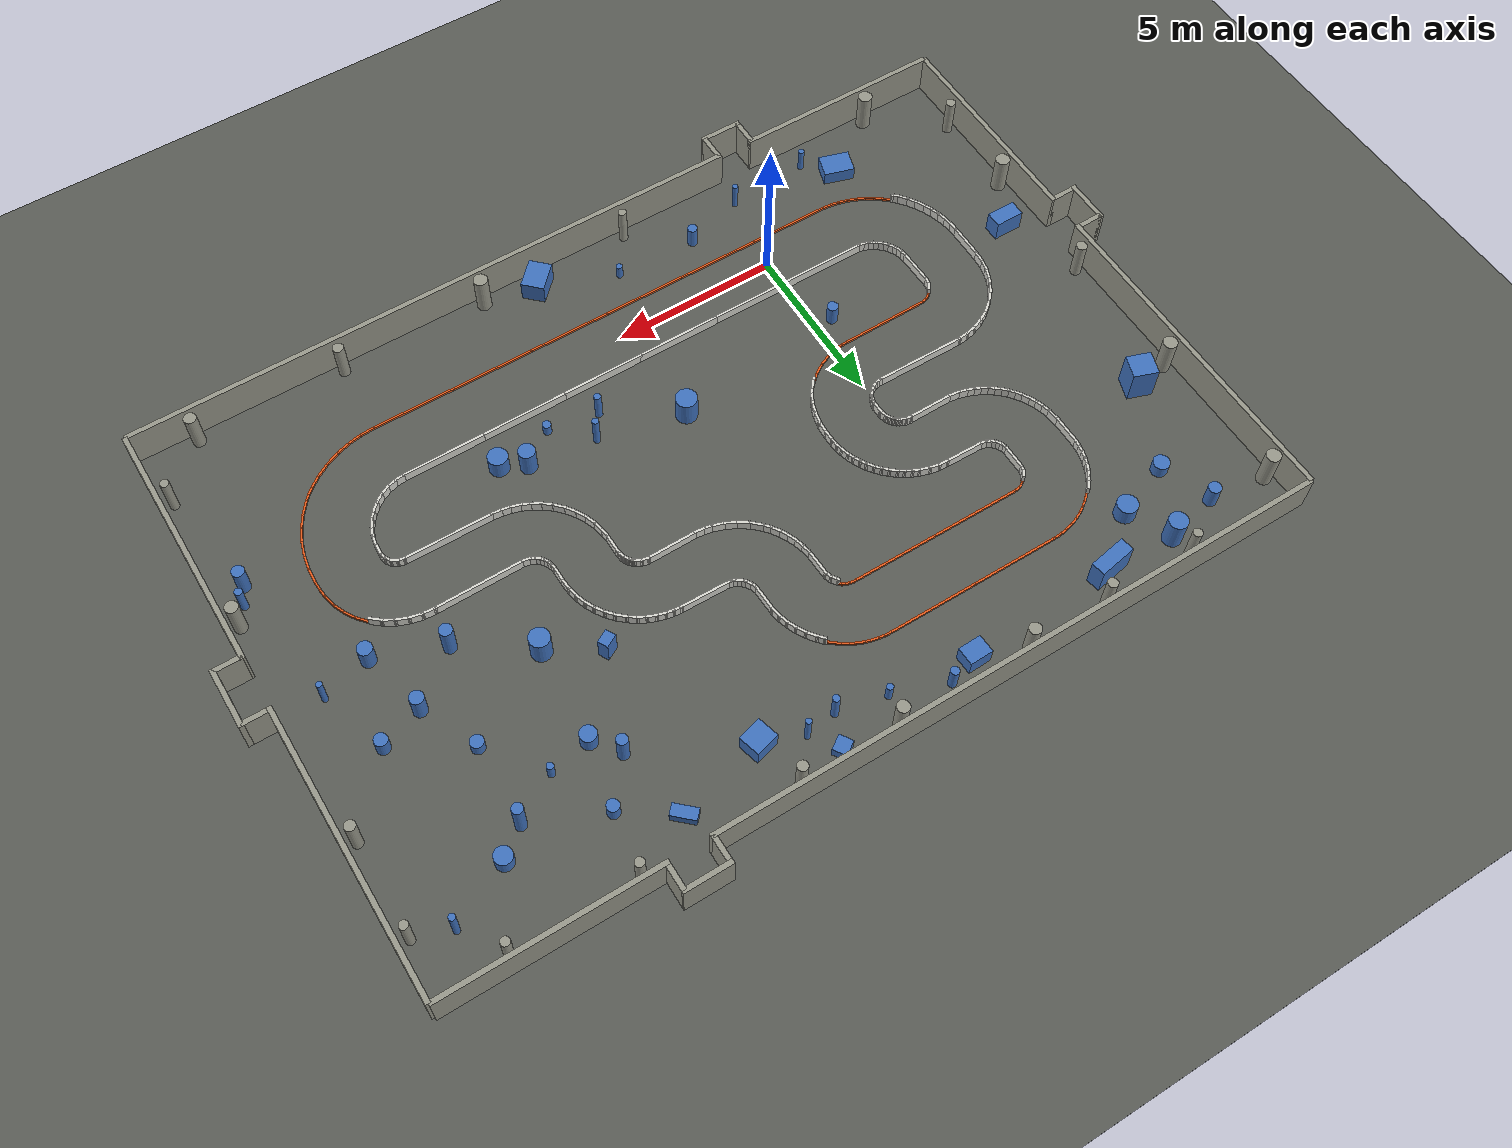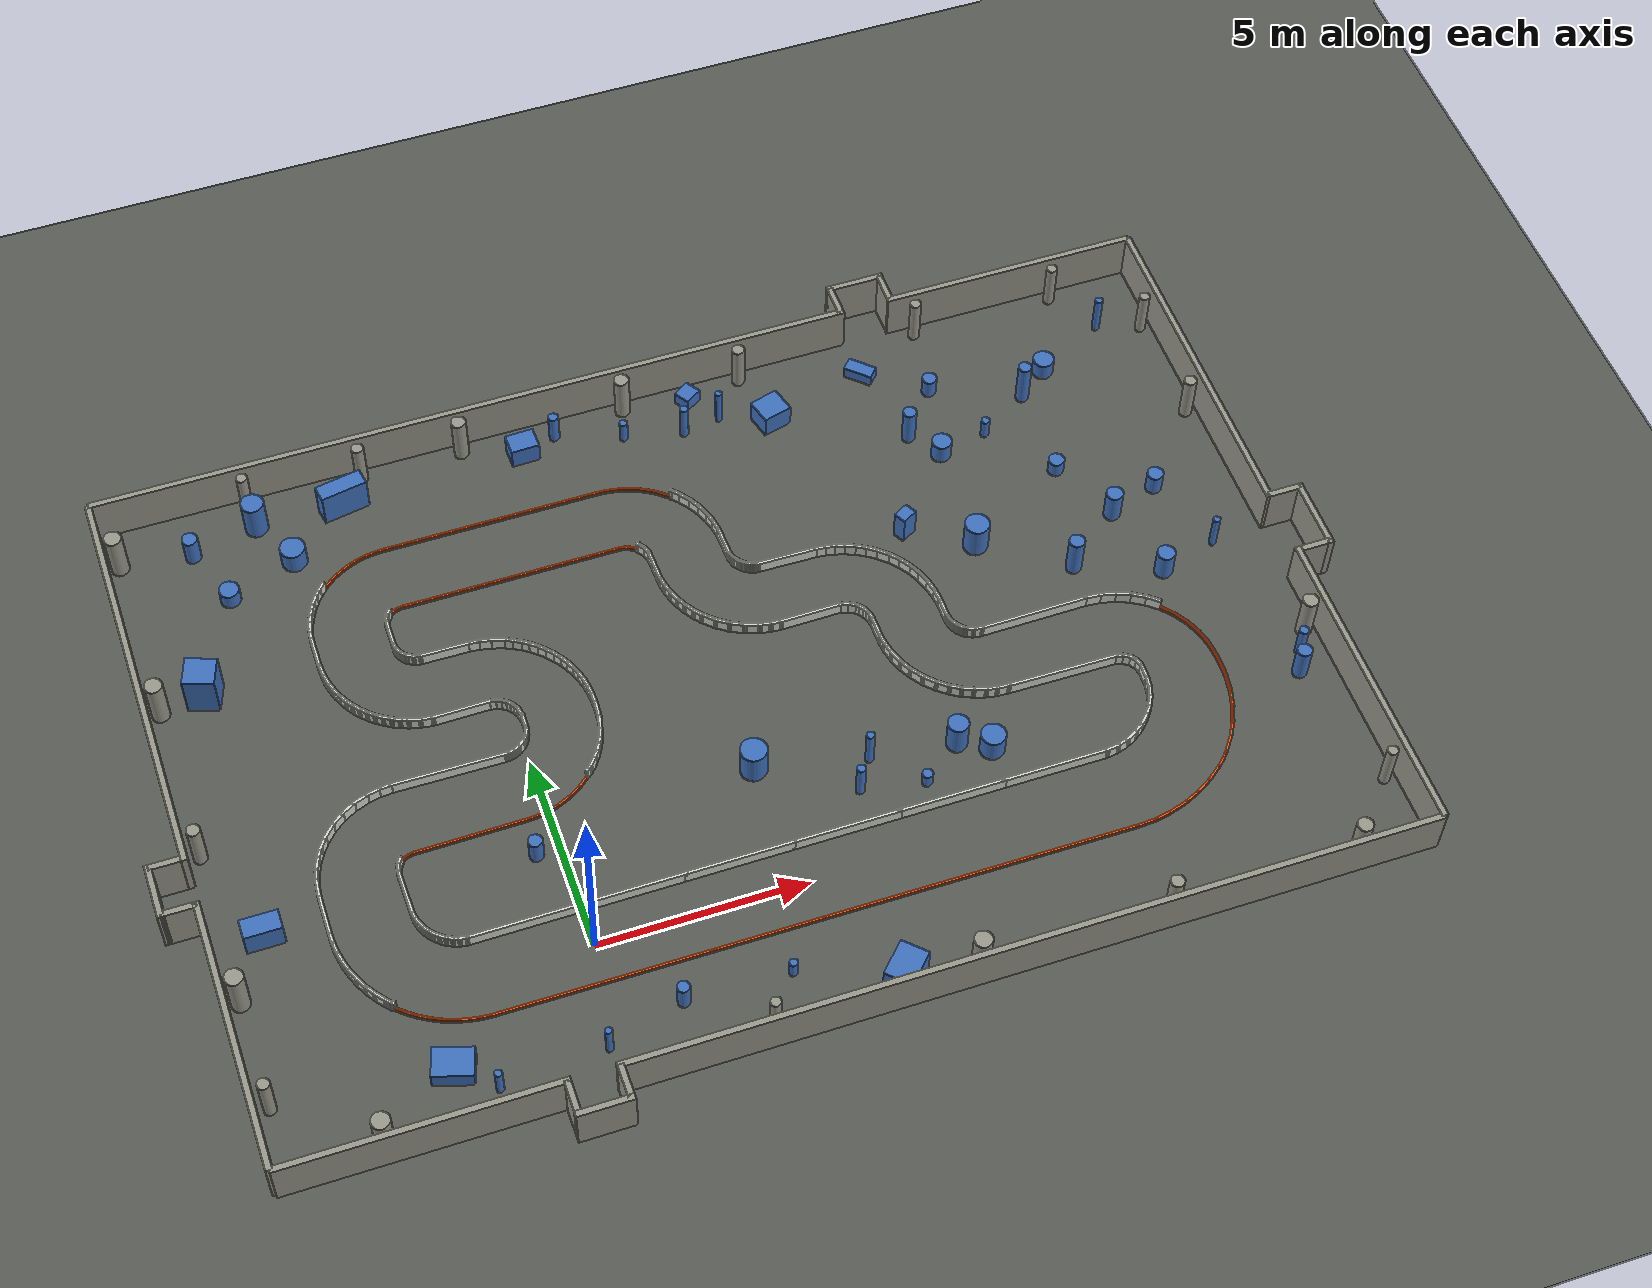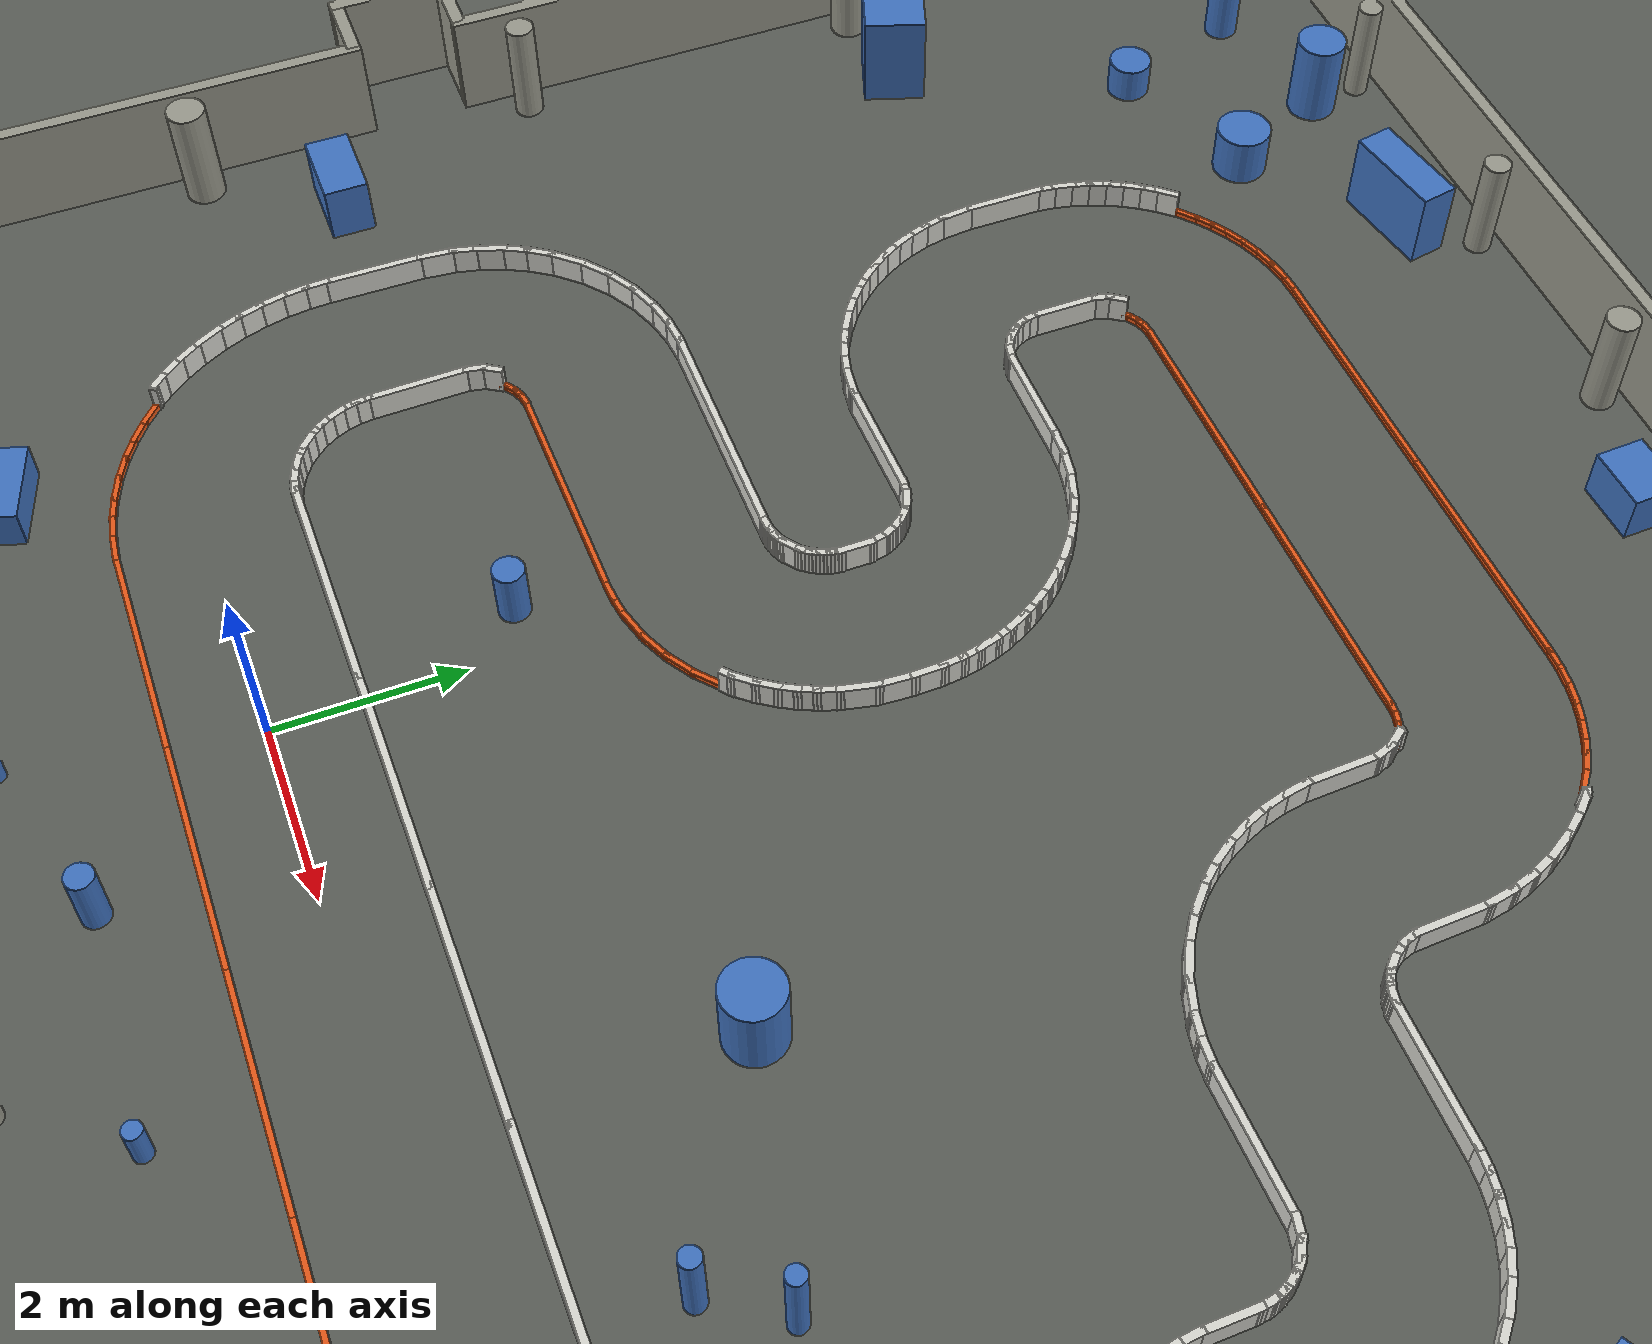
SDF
<?xml version="1.0" ?>
<sdf version="1.9">
  <!-- Generated by simulation/tools/generate_pose_dataset.py --install-gazebo-worlds from tools/pose_dataset/config/tracks.yaml (technical_s). Do not edit by hand: change the YAML and regenerate. -->
  <world name="default">
    <physics name="default_physics" type="dart">
      <max_step_size>0.001</max_step_size>
      <real_time_factor>1.0</real_time_factor>
      <real_time_update_rate>1000.0</real_time_update_rate>
    </physics>
    <plugin filename="gz-sim-physics-system" name="gz::sim::systems::Physics" />
    <plugin filename="gz-sim-user-commands-system" name="gz::sim::systems::UserCommands" />
    <plugin filename="gz-sim-scene-broadcaster-system" name="gz::sim::systems::SceneBroadcaster" />
    <plugin filename="gz-sim-imu-system" name="gz::sim::systems::Imu" />
    <plugin filename="gz-sim-sensors-system" name="gz::sim::systems::Sensors">
      <render_engine>ogre2</render_engine>
    </plugin>
    <light type="directional" name="sun">
      <pose>0 0 10 0 0 0</pose>
      <diffuse>0.8 0.8 0.8 1</diffuse>
      <direction>-0.5 0.5 -1</direction>
      <cast_shadows>true</cast_shadows>
    </light>
    <model name="track_curb">
      <static>true</static>
      <pose>0 0 0 0 0 0</pose>
      <link name="curb_link">
        <collision name="left0_0_0_collision">
          <pose>4.084180 9.982687 0.035000 0.000000 0.000000 2.469345</pose>
          <geometry>
            <box>
              <size>0.183594 0.060000 0.070000</size>
            </box>
          </geometry>
        </collision>
        <visual name="left0_0_0_visual">
          <pose>4.084180 9.982687 0.035000 0.000000 0.000000 2.469345</pose>
          <geometry>
            <box>
              <size>0.183594 0.060000 0.070000</size>
            </box>
          </geometry>
          <material>
            <ambient>0.9 0.35 0.1 1</ambient>
            <diffuse>0.9 0.35 0.1 1</diffuse>
          </material>
        </visual>
        <collision name="left0_1_0_collision">
          <pose>3.984637 10.047771 0.035000 0.000000 0.000000 2.662367</pose>
          <geometry>
            <box>
              <size>0.175380 0.060000 0.070000</size>
            </box>
          </geometry>
        </collision>
        <visual name="left0_1_0_visual">
          <pose>3.984637 10.047771 0.035000 0.000000 0.000000 2.662367</pose>
          <geometry>
            <box>
              <size>0.175380 0.060000 0.070000</size>
            </box>
          </geometry>
          <material>
            <ambient>0.9 0.35 0.1 1</ambient>
            <diffuse>0.9 0.35 0.1 1</diffuse>
          </material>
        </visual>
        <collision name="left0_2_0_collision">
          <pose>3.874162 10.091818 0.035000 0.000000 0.000000 2.855388</pose>
          <geometry>
            <box>
              <size>0.183594 0.060000 0.070000</size>
            </box>
          </geometry>
        </collision>
        <visual name="left0_2_0_visual">
          <pose>3.874162 10.091818 0.035000 0.000000 0.000000 2.855388</pose>
          <geometry>
            <box>
              <size>0.183594 0.060000 0.070000</size>
            </box>
          </geometry>
          <material>
            <ambient>0.9 0.35 0.1 1</ambient>
            <diffuse>0.9 0.35 0.1 1</diffuse>
          </material>
        </visual>
        <collision name="left0_3_0_collision">
          <pose>3.755974 10.114635 0.035000 0.000000 0.000000 3.050675</pose>
          <geometry>
            <box>
              <size>0.178299 0.060000 0.070000</size>
            </box>
          </geometry>
        </collision>
        <visual name="left0_3_0_visual">
          <pose>3.755974 10.114635 0.035000 0.000000 0.000000 3.050675</pose>
          <geometry>
            <box>
              <size>0.178299 0.060000 0.070000</size>
            </box>
          </geometry>
          <material>
            <ambient>0.9 0.35 0.1 1</ambient>
            <diffuse>0.9 0.35 0.1 1</diffuse>
          </material>
        </visual>
        <collision name="left0_4_0_collision">
          <pose>2.369089 10.119951 0.035000 0.000000 0.000000 -3.141552</pose>
          <geometry>
            <box>
              <size>2.715959 0.060000 0.070000</size>
            </box>
          </geometry>
        </collision>
        <visual name="left0_4_0_visual">
          <pose>2.369089 10.119951 0.035000 0.000000 0.000000 -3.141552</pose>
          <geometry>
            <box>
              <size>2.715959 0.060000 0.070000</size>
            </box>
          </geometry>
          <material>
            <ambient>0.9 0.35 0.1 1</ambient>
            <diffuse>0.9 0.35 0.1 1</diffuse>
          </material>
        </visual>
        <collision name="left0_4_1_collision">
          <pose>-0.286870 10.119842 0.035000 0.000000 0.000000 -3.141552</pose>
          <geometry>
            <box>
              <size>2.715959 0.060000 0.070000</size>
            </box>
          </geometry>
        </collision>
        <visual name="left0_4_1_visual">
          <pose>-0.286870 10.119842 0.035000 0.000000 0.000000 -3.141552</pose>
          <geometry>
            <box>
              <size>2.715959 0.060000 0.070000</size>
            </box>
          </geometry>
          <material>
            <ambient>0.9 0.35 0.1 1</ambient>
            <diffuse>0.9 0.35 0.1 1</diffuse>
          </material>
        </visual>
        <collision name="left0_5_0_collision">
          <pose>-1.669924 10.112270 0.035000 0.000000 0.000000 -3.005933</pose>
          <geometry>
            <box>
              <size>0.171171 0.060000 0.070000</size>
            </box>
          </geometry>
        </collision>
        <visual name="left0_5_0_visual">
          <pose>-1.669924 10.112270 0.035000 0.000000 0.000000 -3.005933</pose>
          <geometry>
            <box>
              <size>0.171171 0.060000 0.070000</size>
            </box>
          </geometry>
          <material>
            <ambient>0.9 0.35 0.1 1</ambient>
            <diffuse>0.9 0.35 0.1 1</diffuse>
          </material>
        </visual>
        <collision name="left0_6_0_collision">
          <pose>-1.773873 10.087314 0.035000 0.000000 0.000000 -2.798873</pose>
          <geometry>
            <box>
              <size>0.163785 0.060000 0.070000</size>
            </box>
          </geometry>
        </collision>
        <visual name="left0_6_0_visual">
          <pose>-1.773873 10.087314 0.035000 0.000000 0.000000 -2.798873</pose>
          <geometry>
            <box>
              <size>0.163785 0.060000 0.070000</size>
            </box>
          </geometry>
          <material>
            <ambient>0.9 0.35 0.1 1</ambient>
            <diffuse>0.9 0.35 0.1 1</diffuse>
          </material>
        </visual>
        <collision name="left0_7_0_collision">
          <pose>-1.873066 10.038544 0.035000 0.000000 0.000000 -2.584674</pose>
          <geometry>
            <box>
              <size>0.178551 0.060000 0.070000</size>
            </box>
          </geometry>
        </collision>
        <visual name="left0_7_0_visual">
          <pose>-1.873066 10.038544 0.035000 0.000000 0.000000 -2.584674</pose>
          <geometry>
            <box>
              <size>0.178551 0.060000 0.070000</size>
            </box>
          </geometry>
          <material>
            <ambient>0.9 0.35 0.1 1</ambient>
            <diffuse>0.9 0.35 0.1 1</diffuse>
          </material>
        </visual>
        <collision name="left0_8_0_collision">
          <pose>-1.945540 9.987454 0.035000 0.000000 0.000000 -2.413314</pose>
          <geometry>
            <box>
              <size>0.119372 0.060000 0.070000</size>
            </box>
          </geometry>
        </collision>
        <visual name="left0_8_0_visual">
          <pose>-1.945540 9.987454 0.035000 0.000000 0.000000 -2.413314</pose>
          <geometry>
            <box>
              <size>0.119372 0.060000 0.070000</size>
            </box>
          </geometry>
          <material>
            <ambient>0.9 0.35 0.1 1</ambient>
            <diffuse>0.9 0.35 0.1 1</diffuse>
          </material>
        </visual>
        <collision name="left0_9_0_collision">
          <pose>-1.966716 9.961567 0.035000 0.000000 0.000000 -1.412370</pose>
          <geometry>
            <box>
              <size>0.072413 0.060000 0.070000</size>
            </box>
          </geometry>
        </collision>
        <visual name="left0_9_0_visual">
          <pose>-1.966716 9.961567 0.035000 0.000000 0.000000 -1.412370</pose>
          <geometry>
            <box>
              <size>0.072413 0.060000 0.070000</size>
            </box>
          </geometry>
          <material>
            <ambient>0.9 0.35 0.1 1</ambient>
            <diffuse>0.9 0.35 0.1 1</diffuse>
          </material>
        </visual>
        <collision name="left2_0_0_collision">
          <pose>0.995788 4.119936 0.035000 0.000000 0.000000 -2.436138</pose>
          <geometry>
            <box>
              <size>0.401079 0.060000 0.070000</size>
            </box>
          </geometry>
        </collision>
        <visual name="left2_0_0_visual">
          <pose>0.995788 4.119936 0.035000 0.000000 0.000000 -2.436138</pose>
          <geometry>
            <box>
              <size>0.401079 0.060000 0.070000</size>
            </box>
          </geometry>
          <material>
            <ambient>0.9 0.35 0.1 1</ambient>
            <diffuse>0.9 0.35 0.1 1</diffuse>
          </material>
        </visual>
        <collision name="left2_1_0_collision">
          <pose>0.721235 3.918827 0.035000 0.000000 0.000000 -2.582574</pose>
          <geometry>
            <box>
              <size>0.401409 0.060000 0.070000</size>
            </box>
          </geometry>
        </collision>
        <visual name="left2_1_0_visual">
          <pose>0.721235 3.918827 0.035000 0.000000 0.000000 -2.582574</pose>
          <geometry>
            <box>
              <size>0.401409 0.060000 0.070000</size>
            </box>
          </geometry>
          <material>
            <ambient>0.9 0.35 0.1 1</ambient>
            <diffuse>0.9 0.35 0.1 1</diffuse>
          </material>
        </visual>
        <collision name="left2_2_0_collision">
          <pose>0.419984 3.759779 0.035000 0.000000 0.000000 -2.729011</pose>
          <geometry>
            <box>
              <size>0.401738 0.060000 0.070000</size>
            </box>
          </geometry>
        </collision>
        <visual name="left2_2_0_visual">
          <pose>0.419984 3.759779 0.035000 0.000000 0.000000 -2.729011</pose>
          <geometry>
            <box>
              <size>0.401738 0.060000 0.070000</size>
            </box>
          </geometry>
          <material>
            <ambient>0.9 0.35 0.1 1</ambient>
            <diffuse>0.9 0.35 0.1 1</diffuse>
          </material>
        </visual>
        <collision name="left2_3_0_collision">
          <pose>0.098441 3.646281 0.035000 0.000000 0.000000 -2.875447</pose>
          <geometry>
            <box>
              <size>0.402068 0.060000 0.070000</size>
            </box>
          </geometry>
        </collision>
        <visual name="left2_3_0_visual">
          <pose>0.098441 3.646281 0.035000 0.000000 0.000000 -2.875447</pose>
          <geometry>
            <box>
              <size>0.402068 0.060000 0.070000</size>
            </box>
          </geometry>
          <material>
            <ambient>0.9 0.35 0.1 1</ambient>
            <diffuse>0.9 0.35 0.1 1</diffuse>
          </material>
        </visual>
        <collision name="left2_4_0_collision">
          <pose>-0.174389 3.585404 0.035000 0.000000 0.000000 -2.995252</pose>
          <geometry>
            <box>
              <size>0.277967 0.060000 0.070000</size>
            </box>
          </geometry>
        </collision>
        <visual name="left2_4_0_visual">
          <pose>-0.174389 3.585404 0.035000 0.000000 0.000000 -2.995252</pose>
          <geometry>
            <box>
              <size>0.277967 0.060000 0.070000</size>
            </box>
          </geometry>
          <material>
            <ambient>0.9 0.35 0.1 1</ambient>
            <diffuse>0.9 0.35 0.1 1</diffuse>
          </material>
        </visual>
        <collision name="left2_5_0_collision">
          <pose>-0.375517 3.563925 0.035000 0.000000 0.000000 -3.081781</pose>
          <geometry>
            <box>
              <size>0.246953 0.060000 0.070000</size>
            </box>
          </geometry>
        </collision>
        <visual name="left2_5_0_visual">
          <pose>-0.375517 3.563925 0.035000 0.000000 0.000000 -3.081781</pose>
          <geometry>
            <box>
              <size>0.246953 0.060000 0.070000</size>
            </box>
          </geometry>
          <material>
            <ambient>0.9 0.35 0.1 1</ambient>
            <diffuse>0.9 0.35 0.1 1</diffuse>
          </material>
        </visual>
        <collision name="left2_6_0_collision">
          <pose>-1.795776 3.544254 0.035000 0.000000 0.000000 -3.130980</pose>
          <geometry>
            <box>
              <size>2.714050 0.060000 0.070000</size>
            </box>
          </geometry>
        </collision>
        <visual name="left2_6_0_visual">
          <pose>-1.795776 3.544254 0.035000 0.000000 0.000000 -3.130980</pose>
          <geometry>
            <box>
              <size>2.714050 0.060000 0.070000</size>
            </box>
          </geometry>
          <material>
            <ambient>0.9 0.35 0.1 1</ambient>
            <diffuse>0.9 0.35 0.1 1</diffuse>
          </material>
        </visual>
        <collision name="left2_7_0_collision">
          <pose>-3.174799 3.521243 0.035000 0.000000 0.000000 -2.971773</pose>
          <geometry>
            <box>
              <size>0.165665 0.060000 0.070000</size>
            </box>
          </geometry>
        </collision>
        <visual name="left2_7_0_visual">
          <pose>-3.174799 3.521243 0.035000 0.000000 0.000000 -2.971773</pose>
          <geometry>
            <box>
              <size>0.165665 0.060000 0.070000</size>
            </box>
          </geometry>
          <material>
            <ambient>0.9 0.35 0.1 1</ambient>
            <diffuse>0.9 0.35 0.1 1</diffuse>
          </material>
        </visual>
        <collision name="left2_8_0_collision">
          <pose>-3.275863 3.493318 0.035000 0.000000 0.000000 -2.771706</pose>
          <geometry>
            <box>
              <size>0.165092 0.060000 0.070000</size>
            </box>
          </geometry>
        </collision>
        <visual name="left2_8_0_visual">
          <pose>-3.275863 3.493318 0.035000 0.000000 0.000000 -2.771706</pose>
          <geometry>
            <box>
              <size>0.165092 0.060000 0.070000</size>
            </box>
          </geometry>
          <material>
            <ambient>0.9 0.35 0.1 1</ambient>
            <diffuse>0.9 0.35 0.1 1</diffuse>
          </material>
        </visual>
        <collision name="left2_9_0_collision">
          <pose>-3.374631 3.441410 0.035000 0.000000 0.000000 -2.557375</pose>
          <geometry>
            <box>
              <size>0.179343 0.060000 0.070000</size>
            </box>
          </geometry>
        </collision>
        <visual name="left2_9_0_visual">
          <pose>-3.374631 3.441410 0.035000 0.000000 0.000000 -2.557375</pose>
          <geometry>
            <box>
              <size>0.179343 0.060000 0.070000</size>
            </box>
          </geometry>
          <material>
            <ambient>0.9 0.35 0.1 1</ambient>
            <diffuse>0.9 0.35 0.1 1</diffuse>
          </material>
        </visual>
        <collision name="left2_10_0_collision">
          <pose>-3.446051 3.388098 0.035000 0.000000 0.000000 -2.385797</pose>
          <geometry>
            <box>
              <size>0.119489 0.060000 0.070000</size>
            </box>
          </geometry>
        </collision>
        <visual name="left2_10_0_visual">
          <pose>-3.446051 3.388098 0.035000 0.000000 0.000000 -2.385797</pose>
          <geometry>
            <box>
              <size>0.119489 0.060000 0.070000</size>
            </box>
          </geometry>
          <material>
            <ambient>0.9 0.35 0.1 1</ambient>
            <diffuse>0.9 0.35 0.1 1</diffuse>
          </material>
        </visual>
        <collision name="left2_11_0_collision">
          <pose>-3.466620 3.361473 0.035000 0.000000 0.000000 -1.399502</pose>
          <geometry>
            <box>
              <size>0.072632 0.060000 0.070000</size>
            </box>
          </geometry>
        </collision>
        <visual name="left2_11_0_visual">
          <pose>-3.466620 3.361473 0.035000 0.000000 0.000000 -1.399502</pose>
          <geometry>
            <box>
              <size>0.072632 0.060000 0.070000</size>
            </box>
          </geometry>
          <material>
            <ambient>0.9 0.35 0.1 1</ambient>
            <diffuse>0.9 0.35 0.1 1</diffuse>
          </material>
        </visual>
        <collision name="right1_0_0_collision">
          <pose>5.214179 11.326364 0.035000 0.000000 0.000000 2.449377</pose>
          <geometry>
            <box>
              <size>0.439782 0.060000 0.070000</size>
            </box>
          </geometry>
        </collision>
        <visual name="right1_0_0_visual">
          <pose>5.214179 11.326364 0.035000 0.000000 0.000000 2.449377</pose>
          <geometry>
            <box>
              <size>0.439782 0.060000 0.070000</size>
            </box>
          </geometry>
          <material>
            <ambient>0.9 0.35 0.1 1</ambient>
            <diffuse>0.9 0.35 0.1 1</diffuse>
          </material>
        </visual>
        <collision name="right1_1_0_collision">
          <pose>4.974418 11.506981 0.035000 0.000000 0.000000 2.575840</pose>
          <geometry>
            <box>
              <size>0.281695 0.060000 0.070000</size>
            </box>
          </geometry>
        </collision>
        <visual name="right1_1_0_visual">
          <pose>4.974418 11.506981 0.035000 0.000000 0.000000 2.575840</pose>
          <geometry>
            <box>
              <size>0.281695 0.060000 0.070000</size>
            </box>
          </geometry>
          <material>
            <ambient>0.9 0.35 0.1 1</ambient>
            <diffuse>0.9 0.35 0.1 1</diffuse>
          </material>
        </visual>
        <collision name="right1_2_0_collision">
          <pose>4.796525 11.610214 0.035000 0.000000 0.000000 2.662367</pose>
          <geometry>
            <box>
              <size>0.250042 0.060000 0.070000</size>
            </box>
          </geometry>
        </collision>
        <visual name="right1_2_0_visual">
          <pose>4.796525 11.610214 0.035000 0.000000 0.000000 2.662367</pose>
          <geometry>
            <box>
              <size>0.250042 0.060000 0.070000</size>
            </box>
          </geometry>
          <material>
            <ambient>0.9 0.35 0.1 1</ambient>
            <diffuse>0.9 0.35 0.1 1</diffuse>
          </material>
        </visual>
        <collision name="right1_3_0_collision">
          <pose>4.609798 11.696447 0.035000 0.000000 0.000000 2.748894</pose>
          <geometry>
            <box>
              <size>0.281695 0.060000 0.070000</size>
            </box>
          </geometry>
        </collision>
        <visual name="right1_3_0_visual">
          <pose>4.609798 11.696447 0.035000 0.000000 0.000000 2.748894</pose>
          <geometry>
            <box>
              <size>0.281695 0.060000 0.070000</size>
            </box>
          </geometry>
          <material>
            <ambient>0.9 0.35 0.1 1</ambient>
            <diffuse>0.9 0.35 0.1 1</diffuse>
          </material>
        </visual>
        <collision name="right1_4_0_collision">
          <pose>4.416786 11.767507 0.035000 0.000000 0.000000 2.835420</pose>
          <geometry>
            <box>
              <size>0.250042 0.060000 0.070000</size>
            </box>
          </geometry>
        </collision>
        <visual name="right1_4_0_visual">
          <pose>4.416786 11.767507 0.035000 0.000000 0.000000 2.835420</pose>
          <geometry>
            <box>
              <size>0.250042 0.060000 0.070000</size>
            </box>
          </geometry>
          <material>
            <ambient>0.9 0.35 0.1 1</ambient>
            <diffuse>0.9 0.35 0.1 1</diffuse>
          </material>
        </visual>
        <collision name="right1_5_0_collision">
          <pose>4.233586 11.817468 0.035000 0.000000 0.000000 2.915291</pose>
          <geometry>
            <box>
              <size>0.250042 0.060000 0.070000</size>
            </box>
          </geometry>
        </collision>
        <visual name="right1_5_0_visual">
          <pose>4.233586 11.817468 0.035000 0.000000 0.000000 2.915291</pose>
          <geometry>
            <box>
              <size>0.250042 0.060000 0.070000</size>
            </box>
          </geometry>
          <material>
            <ambient>0.9 0.35 0.1 1</ambient>
            <diffuse>0.9 0.35 0.1 1</diffuse>
          </material>
        </visual>
        <collision name="right1_6_0_collision">
          <pose>4.031221 11.854231 0.035000 0.000000 0.000000 3.001818</pose>
          <geometry>
            <box>
              <size>0.281695 0.060000 0.070000</size>
            </box>
          </geometry>
        </collision>
        <visual name="right1_6_0_visual">
          <pose>4.031221 11.854231 0.035000 0.000000 0.000000 3.001818</pose>
          <geometry>
            <box>
              <size>0.281695 0.060000 0.070000</size>
            </box>
          </geometry>
          <material>
            <ambient>0.9 0.35 0.1 1</ambient>
            <diffuse>0.9 0.35 0.1 1</diffuse>
          </material>
        </visual>
        <collision name="right1_7_0_collision">
          <pose>3.812193 11.874835 0.035000 0.000000 0.000000 3.094399</pose>
          <geometry>
            <box>
              <size>0.278766 0.060000 0.070000</size>
            </box>
          </geometry>
        </collision>
        <visual name="right1_7_0_visual">
          <pose>3.812193 11.874835 0.035000 0.000000 0.000000 3.094399</pose>
          <geometry>
            <box>
              <size>0.278766 0.060000 0.070000</size>
            </box>
          </geometry>
          <material>
            <ambient>0.9 0.35 0.1 1</ambient>
            <diffuse>0.9 0.35 0.1 1</diffuse>
          </material>
        </visual>
        <collision name="right1_8_0_collision">
          <pose>2.376412 11.879995 0.035000 0.000000 0.000000 -3.141593</pose>
          <geometry>
            <box>
              <size>2.713039 0.060000 0.070000</size>
            </box>
          </geometry>
        </collision>
        <visual name="right1_8_0_visual">
          <pose>2.376412 11.879995 0.035000 0.000000 0.000000 -3.141593</pose>
          <geometry>
            <box>
              <size>2.713039 0.060000 0.070000</size>
            </box>
          </geometry>
          <material>
            <ambient>0.9 0.35 0.1 1</ambient>
            <diffuse>0.9 0.35 0.1 1</diffuse>
          </material>
        </visual>
        <collision name="right1_8_1_collision">
          <pose>-0.276627 11.879995 0.035000 0.000000 0.000000 -3.141593</pose>
          <geometry>
            <box>
              <size>2.713039 0.060000 0.070000</size>
            </box>
          </geometry>
        </collision>
        <visual name="right1_8_1_visual">
          <pose>-0.276627 11.879995 0.035000 0.000000 0.000000 -3.141593</pose>
          <geometry>
            <box>
              <size>2.713039 0.060000 0.070000</size>
            </box>
          </geometry>
          <material>
            <ambient>0.9 0.35 0.1 1</ambient>
            <diffuse>0.9 0.35 0.1 1</diffuse>
          </material>
        </visual>
        <collision name="right1_9_0_collision">
          <pose>-1.715338 11.874307 0.035000 0.000000 0.000000 -3.090938</pose>
          <geometry>
            <box>
              <size>0.284670 0.060000 0.070000</size>
            </box>
          </geometry>
        </collision>
        <visual name="right1_9_0_visual">
          <pose>-1.715338 11.874307 0.035000 0.000000 0.000000 -3.090938</pose>
          <geometry>
            <box>
              <size>0.284670 0.060000 0.070000</size>
            </box>
          </geometry>
          <material>
            <ambient>0.9 0.35 0.1 1</ambient>
            <diffuse>0.9 0.35 0.1 1</diffuse>
          </material>
        </visual>
        <collision name="right1_10_0_collision">
          <pose>-1.940158 11.851603 0.035000 0.000000 0.000000 -2.991653</pose>
          <geometry>
            <box>
              <size>0.287813 0.060000 0.070000</size>
            </box>
          </geometry>
        </collision>
        <visual name="right1_10_0_visual">
          <pose>-1.940158 11.851603 0.035000 0.000000 0.000000 -2.991653</pose>
          <geometry>
            <box>
              <size>0.287813 0.060000 0.070000</size>
            </box>
          </geometry>
          <material>
            <ambient>0.9 0.35 0.1 1</ambient>
            <diffuse>0.9 0.35 0.1 1</diffuse>
          </material>
        </visual>
        <collision name="right1_11_0_collision">
          <pose>-2.163155 11.806418 0.035000 0.000000 0.000000 -2.891693</pose>
          <geometry>
            <box>
              <size>0.287813 0.060000 0.070000</size>
            </box>
          </geometry>
        </collision>
        <visual name="right1_11_0_visual">
          <pose>-2.163155 11.806418 0.035000 0.000000 0.000000 -2.891693</pose>
          <geometry>
            <box>
              <size>0.287813 0.060000 0.070000</size>
            </box>
          </geometry>
          <material>
            <ambient>0.9 0.35 0.1 1</ambient>
            <diffuse>0.9 0.35 0.1 1</diffuse>
          </material>
        </visual>
        <collision name="right1_12_0_collision">
          <pose>-2.380530 11.739205 0.035000 0.000000 0.000000 -2.791733</pose>
          <geometry>
            <box>
              <size>0.287813 0.060000 0.070000</size>
            </box>
          </geometry>
        </collision>
        <visual name="right1_12_0_visual">
          <pose>-2.380530 11.739205 0.035000 0.000000 0.000000 -2.791733</pose>
          <geometry>
            <box>
              <size>0.287813 0.060000 0.070000</size>
            </box>
          </geometry>
          <material>
            <ambient>0.9 0.35 0.1 1</ambient>
            <diffuse>0.9 0.35 0.1 1</diffuse>
          </material>
        </visual>
        <collision name="right1_13_0_collision">
          <pose>-2.590112 11.650635 0.035000 0.000000 0.000000 -2.691774</pose>
          <geometry>
            <box>
              <size>0.287813 0.060000 0.070000</size>
            </box>
          </geometry>
        </collision>
        <visual name="right1_13_0_visual">
          <pose>-2.590112 11.650635 0.035000 0.000000 0.000000 -2.691774</pose>
          <geometry>
            <box>
              <size>0.287813 0.060000 0.070000</size>
            </box>
          </geometry>
          <material>
            <ambient>0.9 0.35 0.1 1</ambient>
            <diffuse>0.9 0.35 0.1 1</diffuse>
          </material>
        </visual>
        <collision name="right1_14_0_collision">
          <pose>-2.776306 11.550684 0.035000 0.000000 0.000000 -2.598954</pose>
          <geometry>
            <box>
              <size>0.255290 0.060000 0.070000</size>
            </box>
          </geometry>
        </collision>
        <visual name="right1_14_0_visual">
          <pose>-2.776306 11.550684 0.035000 0.000000 0.000000 -2.598954</pose>
          <geometry>
            <box>
              <size>0.255290 0.060000 0.070000</size>
            </box>
          </geometry>
          <material>
            <ambient>0.9 0.35 0.1 1</ambient>
            <diffuse>0.9 0.35 0.1 1</diffuse>
          </material>
        </visual>
        <collision name="right1_15_0_collision">
          <pose>-2.938921 11.442866 0.035000 0.000000 0.000000 -2.513274</pose>
          <geometry>
            <box>
              <size>0.255290 0.060000 0.070000</size>
            </box>
          </geometry>
        </collision>
        <visual name="right1_15_0_visual">
          <pose>-2.938921 11.442866 0.035000 0.000000 0.000000 -2.513274</pose>
          <geometry>
            <box>
              <size>0.255290 0.060000 0.070000</size>
            </box>
          </geometry>
          <material>
            <ambient>0.9 0.35 0.1 1</ambient>
            <diffuse>0.9 0.35 0.1 1</diffuse>
          </material>
        </visual>
        <collision name="right1_16_0_collision">
          <pose>-3.130075 11.290730 0.035000 0.000000 0.000000 -2.440167</pose>
          <geometry>
            <box>
              <size>0.353635 0.060000 0.070000</size>
            </box>
          </geometry>
        </collision>
        <visual name="right1_16_0_visual">
          <pose>-3.130075 11.290730 0.035000 0.000000 0.000000 -2.440167</pose>
          <geometry>
            <box>
              <size>0.353635 0.060000 0.070000</size>
            </box>
          </geometry>
          <material>
            <ambient>0.9 0.35 0.1 1</ambient>
            <diffuse>0.9 0.35 0.1 1</diffuse>
          </material>
        </visual>
        <collision name="right3_0_0_collision">
          <pose>-4.442427 -0.189192 0.035000 0.000000 0.000000 -0.727590</pose>
          <geometry>
            <box>
              <size>0.351206 0.060000 0.070000</size>
            </box>
          </geometry>
        </collision>
        <visual name="right3_0_0_visual">
          <pose>-4.442427 -0.189192 0.035000 0.000000 0.000000 -0.727590</pose>
          <geometry>
            <box>
              <size>0.351206 0.060000 0.070000</size>
            </box>
          </geometry>
          <material>
            <ambient>0.9 0.35 0.1 1</ambient>
            <diffuse>0.9 0.35 0.1 1</diffuse>
          </material>
        </visual>
        <collision name="right3_1_0_collision">
          <pose>-4.228024 -0.363583 0.035000 0.000000 0.000000 -0.633143</pose>
          <geometry>
            <box>
              <size>0.322151 0.060000 0.070000</size>
            </box>
          </geometry>
        </collision>
        <visual name="right3_1_0_visual">
          <pose>-4.228024 -0.363583 0.035000 0.000000 0.000000 -0.633143</pose>
          <geometry>
            <box>
              <size>0.322151 0.060000 0.070000</size>
            </box>
          </geometry>
          <material>
            <ambient>0.9 0.35 0.1 1</ambient>
            <diffuse>0.9 0.35 0.1 1</diffuse>
          </material>
        </visual>
        <collision name="right3_2_0_collision">
          <pose>-4.010160 -0.508952 0.035000 0.000000 0.000000 -0.543667</pose>
          <geometry>
            <box>
              <size>0.322195 0.060000 0.070000</size>
            </box>
          </geometry>
        </collision>
        <visual name="right3_2_0_visual">
          <pose>-4.010160 -0.508952 0.035000 0.000000 0.000000 -0.543667</pose>
          <geometry>
            <box>
              <size>0.322195 0.060000 0.070000</size>
            </box>
          </geometry>
          <material>
            <ambient>0.9 0.35 0.1 1</ambient>
            <diffuse>0.9 0.35 0.1 1</diffuse>
          </material>
        </visual>
        <collision name="right3_3_0_collision">
          <pose>-3.780139 -0.634292 0.035000 0.000000 0.000000 -0.454191</pose>
          <geometry>
            <box>
              <size>0.322238 0.060000 0.070000</size>
            </box>
          </geometry>
        </collision>
        <visual name="right3_3_0_visual">
          <pose>-3.780139 -0.634292 0.035000 0.000000 0.000000 -0.454191</pose>
          <geometry>
            <box>
              <size>0.322238 0.060000 0.070000</size>
            </box>
          </geometry>
          <material>
            <ambient>0.9 0.35 0.1 1</ambient>
            <diffuse>0.9 0.35 0.1 1</diffuse>
          </material>
        </visual>
        <collision name="right3_4_0_collision">
          <pose>-3.525938 -0.743111 0.035000 0.000000 0.000000 -0.359744</pose>
          <geometry>
            <box>
              <size>0.351403 0.060000 0.070000</size>
            </box>
          </geometry>
        </collision>
        <visual name="right3_4_0_visual">
          <pose>-3.525938 -0.743111 0.035000 0.000000 0.000000 -0.359744</pose>
          <geometry>
            <box>
              <size>0.351403 0.060000 0.070000</size>
            </box>
          </geometry>
          <material>
            <ambient>0.9 0.35 0.1 1</ambient>
            <diffuse>0.9 0.35 0.1 1</diffuse>
          </material>
        </visual>
        <collision name="right3_5_0_collision">
          <pose>-3.262988 -0.828793 0.035000 0.000000 0.000000 -0.265297</pose>
          <geometry>
            <box>
              <size>0.322329 0.060000 0.070000</size>
            </box>
          </geometry>
        </collision>
        <visual name="right3_5_0_visual">
          <pose>-3.262988 -0.828793 0.035000 0.000000 0.000000 -0.265297</pose>
          <geometry>
            <box>
              <size>0.322329 0.060000 0.070000</size>
            </box>
          </geometry>
          <material>
            <ambient>0.9 0.35 0.1 1</ambient>
            <diffuse>0.9 0.35 0.1 1</diffuse>
          </material>
        </visual>
        <collision name="right3_6_0_collision">
          <pose>-3.007248 -0.886131 0.035000 0.000000 0.000000 -0.175821</pose>
          <geometry>
            <box>
              <size>0.322372 0.060000 0.070000</size>
            </box>
          </geometry>
        </collision>
        <visual name="right3_6_0_visual">
          <pose>-3.007248 -0.886131 0.035000 0.000000 0.000000 -0.175821</pose>
          <geometry>
            <box>
              <size>0.322372 0.060000 0.070000</size>
            </box>
          </geometry>
          <material>
            <ambient>0.9 0.35 0.1 1</ambient>
            <diffuse>0.9 0.35 0.1 1</diffuse>
          </material>
        </visual>
        <collision name="right3_7_0_collision">
          <pose>-2.747366 -0.920392 0.035000 0.000000 0.000000 -0.086345</pose>
          <geometry>
            <box>
              <size>0.322416 0.060000 0.070000</size>
            </box>
          </geometry>
        </collision>
        <visual name="right3_7_0_visual">
          <pose>-2.747366 -0.920392 0.035000 0.000000 0.000000 -0.086345</pose>
          <geometry>
            <box>
              <size>0.322416 0.060000 0.070000</size>
            </box>
          </geometry>
          <material>
            <ambient>0.9 0.35 0.1 1</ambient>
            <diffuse>0.9 0.35 0.1 1</diffuse>
          </material>
        </visual>
        <collision name="right3_8_0_collision">
          <pose>-1.362977 -0.935268 0.035000 0.000000 0.000000 -0.002840</pose>
          <geometry>
            <box>
              <size>2.567349 0.060000 0.070000</size>
            </box>
          </geometry>
        </collision>
        <visual name="right3_8_0_visual">
          <pose>-1.362977 -0.935268 0.035000 0.000000 0.000000 -0.002840</pose>
          <geometry>
            <box>
              <size>2.567349 0.060000 0.070000</size>
            </box>
          </geometry>
          <material>
            <ambient>0.9 0.35 0.1 1</ambient>
            <diffuse>0.9 0.35 0.1 1</diffuse>
          </material>
        </visual>
        <collision name="right3_8_1_collision">
          <pose>1.144362 -0.942389 0.035000 0.000000 0.000000 -0.002840</pose>
          <geometry>
            <box>
              <size>2.567349 0.060000 0.070000</size>
            </box>
          </geometry>
        </collision>
        <visual name="right3_8_1_visual">
          <pose>1.144362 -0.942389 0.035000 0.000000 0.000000 -0.002840</pose>
          <geometry>
            <box>
              <size>2.567349 0.060000 0.070000</size>
            </box>
          </geometry>
          <material>
            <ambient>0.9 0.35 0.1 1</ambient>
            <diffuse>0.9 0.35 0.1 1</diffuse>
          </material>
        </visual>
        <collision name="right3_8_2_collision">
          <pose>3.651702 -0.949510 0.035000 0.000000 0.000000 -0.002840</pose>
          <geometry>
            <box>
              <size>2.567349 0.060000 0.070000</size>
            </box>
          </geometry>
        </collision>
        <visual name="right3_8_2_visual">
          <pose>3.651702 -0.949510 0.035000 0.000000 0.000000 -0.002840</pose>
          <geometry>
            <box>
              <size>2.567349 0.060000 0.070000</size>
            </box>
          </geometry>
          <material>
            <ambient>0.9 0.35 0.1 1</ambient>
            <diffuse>0.9 0.35 0.1 1</diffuse>
          </material>
        </visual>
        <collision name="right3_8_3_collision">
          <pose>6.159041 -0.956631 0.035000 0.000000 0.000000 -0.002840</pose>
          <geometry>
            <box>
              <size>2.567349 0.060000 0.070000</size>
            </box>
          </geometry>
        </collision>
        <visual name="right3_8_3_visual">
          <pose>6.159041 -0.956631 0.035000 0.000000 0.000000 -0.002840</pose>
          <geometry>
            <box>
              <size>2.567349 0.060000 0.070000</size>
            </box>
          </geometry>
          <material>
            <ambient>0.9 0.35 0.1 1</ambient>
            <diffuse>0.9 0.35 0.1 1</diffuse>
          </material>
        </visual>
        <collision name="right3_8_4_collision">
          <pose>8.666380 -0.963752 0.035000 0.000000 0.000000 -0.002840</pose>
          <geometry>
            <box>
              <size>2.567349 0.060000 0.070000</size>
            </box>
          </geometry>
        </collision>
        <visual name="right3_8_4_visual">
          <pose>8.666380 -0.963752 0.035000 0.000000 0.000000 -0.002840</pose>
          <geometry>
            <box>
              <size>2.567349 0.060000 0.070000</size>
            </box>
          </geometry>
          <material>
            <ambient>0.9 0.35 0.1 1</ambient>
            <diffuse>0.9 0.35 0.1 1</diffuse>
          </material>
        </visual>
        <collision name="right3_8_5_collision">
          <pose>11.173720 -0.970873 0.035000 0.000000 0.000000 -0.002840</pose>
          <geometry>
            <box>
              <size>2.567349 0.060000 0.070000</size>
            </box>
          </geometry>
        </collision>
        <visual name="right3_8_5_visual">
          <pose>11.173720 -0.970873 0.035000 0.000000 0.000000 -0.002840</pose>
          <geometry>
            <box>
              <size>2.567349 0.060000 0.070000</size>
            </box>
          </geometry>
          <material>
            <ambient>0.9 0.35 0.1 1</ambient>
            <diffuse>0.9 0.35 0.1 1</diffuse>
          </material>
        </visual>
        <collision name="right3_9_0_collision">
          <pose>12.632312 -0.961472 0.035000 0.000000 0.000000 0.063168</pose>
          <geometry>
            <box>
              <size>0.470665 0.060000 0.070000</size>
            </box>
          </geometry>
        </collision>
        <visual name="right3_9_0_visual">
          <pose>12.632312 -0.961472 0.035000 0.000000 0.000000 0.063168</pose>
          <geometry>
            <box>
              <size>0.470665 0.060000 0.070000</size>
            </box>
          </geometry>
          <material>
            <ambient>0.9 0.35 0.1 1</ambient>
            <diffuse>0.9 0.35 0.1 1</diffuse>
          </material>
        </visual>
        <collision name="right3_10_0_collision">
          <pose>13.026031 -0.915270 0.035000 0.000000 0.000000 0.174274</pose>
          <geometry>
            <box>
              <size>0.443399 0.060000 0.070000</size>
            </box>
          </geometry>
        </collision>
        <visual name="right3_10_0_visual">
          <pose>13.026031 -0.915270 0.035000 0.000000 0.000000 0.174274</pose>
          <geometry>
            <box>
              <size>0.443399 0.060000 0.070000</size>
            </box>
          </geometry>
          <material>
            <ambient>0.9 0.35 0.1 1</ambient>
            <diffuse>0.9 0.35 0.1 1</diffuse>
          </material>
        </visual>
        <collision name="right3_11_0_collision">
          <pose>13.424829 -0.819544 0.035000 0.000000 0.000000 0.289211</pose>
          <geometry>
            <box>
              <size>0.498204 0.060000 0.070000</size>
            </box>
          </geometry>
        </collision>
        <visual name="right3_11_0_visual">
          <pose>13.424829 -0.819544 0.035000 0.000000 0.000000 0.289211</pose>
          <geometry>
            <box>
              <size>0.498204 0.060000 0.070000</size>
            </box>
          </geometry>
          <material>
            <ambient>0.9 0.35 0.1 1</ambient>
            <diffuse>0.9 0.35 0.1 1</diffuse>
          </material>
        </visual>
        <collision name="right3_12_0_collision">
          <pose>13.835665 -0.669336 0.035000 0.000000 0.000000 0.411810</pose>
          <geometry>
            <box>
              <size>0.498310 0.060000 0.070000</size>
            </box>
          </geometry>
        </collision>
        <visual name="right3_12_0_visual">
          <pose>13.835665 -0.669336 0.035000 0.000000 0.000000 0.411810</pose>
          <geometry>
            <box>
              <size>0.498310 0.060000 0.070000</size>
            </box>
          </geometry>
          <material>
            <ambient>0.9 0.35 0.1 1</ambient>
            <diffuse>0.9 0.35 0.1 1</diffuse>
          </material>
        </visual>
        <collision name="right3_13_0_collision">
          <pose>14.225141 -0.469966 0.035000 0.000000 0.000000 0.534409</pose>
          <geometry>
            <box>
              <size>0.498415 0.060000 0.070000</size>
            </box>
          </geometry>
        </collision>
        <visual name="right3_13_0_visual">
          <pose>14.225141 -0.469966 0.035000 0.000000 0.000000 0.534409</pose>
          <geometry>
            <box>
              <size>0.498415 0.060000 0.070000</size>
            </box>
          </geometry>
          <material>
            <ambient>0.9 0.35 0.1 1</ambient>
            <diffuse>0.9 0.35 0.1 1</diffuse>
          </material>
        </visual>
        <collision name="right3_14_0_collision">
          <pose>14.587400 -0.224402 0.035000 0.000000 0.000000 0.657009</pose>
          <geometry>
            <box>
              <size>0.498521 0.060000 0.070000</size>
            </box>
          </geometry>
        </collision>
        <visual name="right3_14_0_visual">
          <pose>14.587400 -0.224402 0.035000 0.000000 0.000000 0.657009</pose>
          <geometry>
            <box>
              <size>0.498521 0.060000 0.070000</size>
            </box>
          </geometry>
          <material>
            <ambient>0.9 0.35 0.1 1</ambient>
            <diffuse>0.9 0.35 0.1 1</diffuse>
          </material>
        </visual>
        <collision name="right3_15_0_collision">
          <pose>14.841361 -0.015796 0.035000 0.000000 0.000000 0.748956</pose>
          <geometry>
            <box>
              <size>0.279403 0.060000 0.070000</size>
            </box>
          </geometry>
        </collision>
        <visual name="right3_15_0_visual">
          <pose>14.841361 -0.015796 0.035000 0.000000 0.000000 0.748956</pose>
          <geometry>
            <box>
              <size>0.279403 0.060000 0.070000</size>
            </box>
          </geometry>
          <material>
            <ambient>0.9 0.35 0.1 1</ambient>
            <diffuse>0.9 0.35 0.1 1</diffuse>
          </material>
        </visual>
        <collision name="right3_16_0_collision">
          <pose>14.986582 0.129611 0.035000 0.000000 0.000000 0.828429</pose>
          <geometry>
            <box>
              <size>0.251931 0.060000 0.070000</size>
            </box>
          </geometry>
        </collision>
        <visual name="right3_16_0_visual">
          <pose>14.986582 0.129611 0.035000 0.000000 0.000000 0.828429</pose>
          <geometry>
            <box>
              <size>0.251931 0.060000 0.070000</size>
            </box>
          </geometry>
          <material>
            <ambient>0.9 0.35 0.1 1</ambient>
            <diffuse>0.9 0.35 0.1 1</diffuse>
          </material>
        </visual>
        <collision name="right3_17_0_collision">
          <pose>15.184337 0.374201 0.035000 0.000000 0.000000 0.918259</pose>
          <geometry>
            <box>
              <size>0.497673 0.060000 0.070000</size>
            </box>
          </geometry>
        </collision>
        <visual name="right3_17_0_visual">
          <pose>15.184337 0.374201 0.035000 0.000000 0.000000 0.918259</pose>
          <geometry>
            <box>
              <size>0.497673 0.060000 0.070000</size>
            </box>
          </geometry>
          <material>
            <ambient>0.9 0.35 0.1 1</ambient>
            <diffuse>0.9 0.35 0.1 1</diffuse>
          </material>
        </visual>
        <collision name="right3_18_0_collision">
          <pose>15.421324 0.724260 0.035000 0.000000 0.000000 1.037086</pose>
          <geometry>
            <box>
              <size>0.469288 0.060000 0.070000</size>
            </box>
          </geometry>
        </collision>
        <visual name="right3_18_0_visual">
          <pose>15.421324 0.724260 0.035000 0.000000 0.000000 1.037086</pose>
          <geometry>
            <box>
              <size>0.469288 0.060000 0.070000</size>
            </box>
          </geometry>
          <material>
            <ambient>0.9 0.35 0.1 1</ambient>
            <diffuse>0.9 0.35 0.1 1</diffuse>
          </material>
        </visual>
        <collision name="right3_19_0_collision">
          <pose>15.613187 1.099678 0.035000 0.000000 0.000000 1.155907</pose>
          <geometry>
            <box>
              <size>0.495409 0.060000 0.070000</size>
            </box>
          </geometry>
        </collision>
        <visual name="right3_19_0_visual">
          <pose>15.613187 1.099678 0.035000 0.000000 0.000000 1.155907</pose>
          <geometry>
            <box>
              <size>0.495409 0.060000 0.070000</size>
            </box>
          </geometry>
          <material>
            <ambient>0.9 0.35 0.1 1</ambient>
            <diffuse>0.9 0.35 0.1 1</diffuse>
          </material>
        </visual>
        <collision name="right3_20_0_collision">
          <pose>15.763492 1.506828 0.035000 0.000000 0.000000 1.278565</pose>
          <geometry>
            <box>
              <size>0.494241 0.060000 0.070000</size>
            </box>
          </geometry>
        </collision>
        <visual name="right3_20_0_visual">
          <pose>15.763492 1.506828 0.035000 0.000000 0.000000 1.278565</pose>
          <geometry>
            <box>
              <size>0.494241 0.060000 0.070000</size>
            </box>
          </geometry>
          <material>
            <ambient>0.9 0.35 0.1 1</ambient>
            <diffuse>0.9 0.35 0.1 1</diffuse>
          </material>
        </visual>
        <collision name="right3_21_0_collision">
          <pose>15.863994 1.941623 0.035000 0.000000 0.000000 1.405052</pose>
          <geometry>
            <box>
              <size>0.520063 0.060000 0.070000</size>
            </box>
          </geometry>
        </collision>
        <visual name="right3_21_0_visual">
          <pose>15.863994 1.941623 0.035000 0.000000 0.000000 1.405052</pose>
          <geometry>
            <box>
              <size>0.520063 0.060000 0.070000</size>
            </box>
          </geometry>
          <material>
            <ambient>0.9 0.35 0.1 1</ambient>
            <diffuse>0.9 0.35 0.1 1</diffuse>
          </material>
        </visual>
        <collision name="right3_22_0_collision">
          <pose>15.910665 2.370767 0.035000 0.000000 0.000000 1.527717</pose>
          <geometry>
            <box>
              <size>0.464906 0.060000 0.070000</size>
            </box>
          </geometry>
        </collision>
        <visual name="right3_22_0_visual">
          <pose>15.910665 2.370767 0.035000 0.000000 0.000000 1.527717</pose>
          <geometry>
            <box>
              <size>0.464906 0.060000 0.070000</size>
            </box>
          </geometry>
          <material>
            <ambient>0.9 0.35 0.1 1</ambient>
            <diffuse>0.9 0.35 0.1 1</diffuse>
          </material>
        </visual>
        <collision name="right3_23_0_collision">
          <pose>15.914187 2.736005 0.035000 0.000000 0.000000 1.602672</pose>
          <geometry>
            <box>
              <size>0.386111 0.060000 0.070000</size>
            </box>
          </geometry>
        </collision>
        <visual name="right3_23_0_visual">
          <pose>15.914187 2.736005 0.035000 0.000000 0.000000 1.602672</pose>
          <geometry>
            <box>
              <size>0.386111 0.060000 0.070000</size>
            </box>
          </geometry>
          <material>
            <ambient>0.9 0.35 0.1 1</ambient>
            <diffuse>0.9 0.35 0.1 1</diffuse>
          </material>
        </visual>
        <collision name="right3_24_0_collision">
          <pose>15.896216 3.013643 0.035000 0.000000 0.000000 1.681743</pose>
          <geometry>
            <box>
              <size>0.290751 0.060000 0.070000</size>
            </box>
          </geometry>
        </collision>
        <visual name="right3_24_0_visual">
          <pose>15.896216 3.013643 0.035000 0.000000 0.000000 1.681743</pose>
          <geometry>
            <box>
              <size>0.290751 0.060000 0.070000</size>
            </box>
          </geometry>
          <material>
            <ambient>0.9 0.35 0.1 1</ambient>
            <diffuse>0.9 0.35 0.1 1</diffuse>
          </material>
        </visual>
        <collision name="right3_25_0_collision">
          <pose>15.840562 3.303921 0.035000 0.000000 0.000000 1.810283</pose>
          <geometry>
            <box>
              <size>0.421541 0.060000 0.070000</size>
            </box>
          </geometry>
        </collision>
        <visual name="right3_25_0_visual">
          <pose>15.840562 3.303921 0.035000 0.000000 0.000000 1.810283</pose>
          <geometry>
            <box>
              <size>0.421541 0.060000 0.070000</size>
            </box>
          </geometry>
          <material>
            <ambient>0.9 0.35 0.1 1</ambient>
            <diffuse>0.9 0.35 0.1 1</diffuse>
          </material>
        </visual>
        <collision name="right3_26_0_collision">
          <pose>15.728050 3.645794 0.035000 0.000000 0.000000 1.967415</pose>
          <geometry>
            <box>
              <size>0.420509 0.060000 0.070000</size>
            </box>
          </geometry>
        </collision>
        <visual name="right3_26_0_visual">
          <pose>15.728050 3.645794 0.035000 0.000000 0.000000 1.967415</pose>
          <geometry>
            <box>
              <size>0.420509 0.060000 0.070000</size>
            </box>
          </geometry>
          <material>
            <ambient>0.9 0.35 0.1 1</ambient>
            <diffuse>0.9 0.35 0.1 1</diffuse>
          </material>
        </visual>
        <collision name="right3_27_0_collision">
          <pose>15.563896 3.964933 0.035000 0.000000 0.000000 2.124547</pose>
          <geometry>
            <box>
              <size>0.419476 0.060000 0.070000</size>
            </box>
          </geometry>
        </collision>
        <visual name="right3_27_0_visual">
          <pose>15.563896 3.964933 0.035000 0.000000 0.000000 2.124547</pose>
          <geometry>
            <box>
              <size>0.419476 0.060000 0.070000</size>
            </box>
          </geometry>
          <material>
            <ambient>0.9 0.35 0.1 1</ambient>
            <diffuse>0.9 0.35 0.1 1</diffuse>
          </material>
        </visual>
        <collision name="right3_28_0_collision">
          <pose>15.332610 4.279948 0.035000 0.000000 0.000000 2.271516</pose>
          <geometry>
            <box>
              <size>0.484232 0.060000 0.070000</size>
            </box>
          </geometry>
        </collision>
        <visual name="right3_28_0_visual">
          <pose>15.332610 4.279948 0.035000 0.000000 0.000000 2.271516</pose>
          <geometry>
            <box>
              <size>0.484232 0.060000 0.070000</size>
            </box>
          </geometry>
          <material>
            <ambient>0.9 0.35 0.1 1</ambient>
            <diffuse>0.9 0.35 0.1 1</diffuse>
          </material>
        </visual>
      </link>
    </model>
    <model name="track_feature">
      <static>true</static>
      <pose>0 0 0 0 0 0</pose>
      <link name="feature_link">
        <collision name="feat_box_5_collision">
          <pose>-2.174799 13.437083 0.448464 0.000000 0.000000 0.172310</pose>
          <geometry>
            <box>
              <size>1.150190 0.421792 0.896928</size>
            </box>
          </geometry>
        </collision>
        <visual name="feat_box_5_visual">
          <pose>-2.174799 13.437083 0.448464 0.000000 0.000000 0.172310</pose>
          <geometry>
            <box>
              <size>1.150190 0.421792 0.896928</size>
            </box>
          </geometry>
          <material>
            <ambient>0.25 0.45 0.75 1</ambient>
            <diffuse>0.25 0.45 0.75 1</diffuse>
          </material>
        </visual>
        <collision name="feat_box_6_collision">
          <pose>-6.569533 9.118190 0.548116 0.000000 0.000000 -0.333008</pose>
          <geometry>
            <box>
              <size>0.749614 0.699634 1.096233</size>
            </box>
          </geometry>
        </collision>
        <visual name="feat_box_6_visual">
          <pose>-6.569533 9.118190 0.548116 0.000000 0.000000 -0.333008</pose>
          <geometry>
            <box>
              <size>0.749614 0.699634 1.096233</size>
            </box>
          </geometry>
          <material>
            <ambient>0.25 0.45 0.75 1</ambient>
            <diffuse>0.25 0.45 0.75 1</diffuse>
          </material>
        </visual>
        <collision name="feat_box_7_collision">
          <pose>10.310160 8.431159 0.380792 0.000000 0.000000 2.068388</pose>
          <geometry>
            <box>
              <size>0.315067 0.410631 0.761584</size>
            </box>
          </geometry>
        </collision>
        <visual name="feat_box_7_visual">
          <pose>10.310160 8.431159 0.380792 0.000000 0.000000 2.068388</pose>
          <geometry>
            <box>
              <size>0.315067 0.410631 0.761584</size>
            </box>
          </geometry>
          <material>
            <ambient>0.25 0.45 0.75 1</ambient>
            <diffuse>0.25 0.45 0.75 1</diffuse>
          </material>
        </visual>
        <collision name="feat_box_9_collision">
          <pose>10.962512 13.339833 0.157273 0.000000 0.000000 0.816995</pose>
          <geometry>
            <box>
              <size>0.345128 0.717801 0.314546</size>
            </box>
          </geometry>
        </collision>
        <visual name="feat_box_9_visual">
          <pose>10.962512 13.339833 0.157273 0.000000 0.000000 0.816995</pose>
          <geometry>
            <box>
              <size>0.345128 0.717801 0.314546</size>
            </box>
          </geometry>
          <material>
            <ambient>0.25 0.45 0.75 1</ambient>
            <diffuse>0.25 0.45 0.75 1</diffuse>
          </material>
        </visual>
        <collision name="feat_box_10_collision">
          <pose>8.403281 12.710792 0.289428 0.000000 0.000000 -1.310550</pose>
          <geometry>
            <box>
              <size>0.654921 0.731768 0.578856</size>
            </box>
          </geometry>
        </collision>
        <visual name="feat_box_10_visual">
          <pose>8.403281 12.710792 0.289428 0.000000 0.000000 -1.310550</pose>
          <geometry>
            <box>
              <size>0.654921 0.731768 0.578856</size>
            </box>
          </geometry>
          <material>
            <ambient>0.25 0.45 0.75 1</ambient>
            <diffuse>0.25 0.45 0.75 1</diffuse>
          </material>
        </visual>
        <collision name="feat_box_20_collision">
          <pose>-3.734603 -1.923020 0.218863 0.000000 0.000000 2.840322</pose>
          <geometry>
            <box>
              <size>0.931133 0.693589 0.437726</size>
            </box>
          </geometry>
        </collision>
        <visual name="feat_box_20_visual">
          <pose>-3.734603 -1.923020 0.218863 0.000000 0.000000 2.840322</pose>
          <geometry>
            <box>
              <size>0.931133 0.693589 0.437726</size>
            </box>
          </geometry>
          <material>
            <ambient>0.25 0.45 0.75 1</ambient>
            <diffuse>0.25 0.45 0.75 1</diffuse>
          </material>
        </visual>
        <collision name="feat_box_21_collision">
          <pose>2.355821 13.623546 0.272021 0.000000 0.000000 1.598540</pose>
          <geometry>
            <box>
              <size>0.541540 0.700797 0.544043</size>
            </box>
          </geometry>
        </collision>
        <visual name="feat_box_21_visual">
          <pose>2.355821 13.623546 0.272021 0.000000 0.000000 1.598540</pose>
          <geometry>
            <box>
              <size>0.541540 0.700797 0.544043</size>
            </box>
          </geometry>
          <material>
            <ambient>0.25 0.45 0.75 1</ambient>
            <diffuse>0.25 0.45 0.75 1</diffuse>
          </material>
        </visual>
        <collision name="feat_box_26_collision">
          <pose>6.139113 -2.872765 0.319586 0.000000 0.000000 0.792740</pose>
          <geometry>
            <box>
              <size>0.904940 0.691659 0.639172</size>
            </box>
          </geometry>
        </collision>
        <visual name="feat_box_26_visual">
          <pose>6.139113 -2.872765 0.319586 0.000000 0.000000 0.792740</pose>
          <geometry>
            <box>
              <size>0.904940 0.691659 0.639172</size>
            </box>
          </geometry>
          <material>
            <ambient>0.25 0.45 0.75 1</ambient>
            <diffuse>0.25 0.45 0.75 1</diffuse>
          </material>
        </visual>
        <collision name="feat_box_31_collision">
          <pose>-6.799827 2.495728 0.328114 0.000000 0.000000 1.572940</pose>
          <geometry>
            <box>
              <size>0.486991 0.883632 0.656227</size>
            </box>
          </geometry>
        </collision>
        <visual name="feat_box_31_visual">
          <pose>-6.799827 2.495728 0.328114 0.000000 0.000000 1.572940</pose>
          <geometry>
            <box>
              <size>0.486991 0.883632 0.656227</size>
            </box>
          </geometry>
          <material>
            <ambient>0.25 0.45 0.75 1</ambient>
            <diffuse>0.25 0.45 0.75 1</diffuse>
          </material>
        </visual>
        <collision name="feat_box_44_collision">
          <pose>6.667799 13.940735 0.173201 0.000000 0.000000 -2.572693</pose>
          <geometry>
            <box>
              <size>0.458432 0.416363 0.346402</size>
            </box>
          </geometry>
        </collision>
        <visual name="feat_box_44_visual">
          <pose>6.667799 13.940735 0.173201 0.000000 0.000000 -2.572693</pose>
          <geometry>
            <box>
              <size>0.458432 0.416363 0.346402</size>
            </box>
          </geometry>
          <material>
            <ambient>0.25 0.45 0.75 1</ambient>
            <diffuse>0.25 0.45 0.75 1</diffuse>
          </material>
        </visual>
        <collision name="feat_cyl_1_collision">
          <pose>1.403269 -1.914486 0.340358 0.000000 0.000000 0.000000</pose>
          <geometry>
            <cylinder>
              <radius>0.145363</radius>
              <length>0.680715</length>
            </cylinder>
          </geometry>
        </collision>
        <visual name="feat_cyl_1_visual">
          <pose>1.403269 -1.914486 0.340358 0.000000 0.000000 0.000000</pose>
          <geometry>
            <cylinder>
              <radius>0.145363</radius>
              <length>0.680715</length>
            </cylinder>
          </geometry>
          <material>
            <ambient>0.25 0.45 0.75 1</ambient>
            <diffuse>0.25 0.45 0.75 1</diffuse>
          </material>
        </visual>
        <collision name="feat_cyl_2_collision">
          <pose>16.485374 7.789993 0.274178 0.000000 0.000000 0.000000</pose>
          <geometry>
            <cylinder>
              <radius>0.194425</radius>
              <length>0.548357</length>
            </cylinder>
          </geometry>
        </collision>
        <visual name="feat_cyl_2_visual">
          <pose>16.485374 7.789993 0.274178 0.000000 0.000000 0.000000</pose>
          <geometry>
            <cylinder>
              <radius>0.194425</radius>
              <length>0.548357</length>
            </cylinder>
          </geometry>
          <material>
            <ambient>0.25 0.45 0.75 1</ambient>
            <diffuse>0.25 0.45 0.75 1</diffuse>
          </material>
        </visual>
        <collision name="feat_cyl_3_collision">
          <pose>-4.304456 13.519091 0.484793 0.000000 0.000000 0.000000</pose>
          <geometry>
            <cylinder>
              <radius>0.276709</radius>
              <length>0.969587</length>
            </cylinder>
          </geometry>
        </collision>
        <visual name="feat_cyl_3_visual">
          <pose>-4.304456 13.519091 0.484793 0.000000 0.000000 0.000000</pose>
          <geometry>
            <cylinder>
              <radius>0.276709</radius>
              <length>0.969587</length>
            </cylinder>
          </geometry>
          <material>
            <ambient>0.25 0.45 0.75 1</ambient>
            <diffuse>0.25 0.45 0.75 1</diffuse>
          </material>
        </visual>
        <collision name="feat_cyl_4_collision">
          <pose>17.807359 2.253464 0.427318 0.000000 0.000000 0.000000</pose>
          <geometry>
            <cylinder>
              <radius>0.111590</radius>
              <length>0.854636</length>
            </cylinder>
          </geometry>
        </collision>
        <visual name="feat_cyl_4_visual">
          <pose>17.807359 2.253464 0.427318 0.000000 0.000000 0.000000</pose>
          <geometry>
            <cylinder>
              <radius>0.111590</radius>
              <length>0.854636</length>
            </cylinder>
          </geometry>
          <material>
            <ambient>0.25 0.45 0.75 1</ambient>
            <diffuse>0.25 0.45 0.75 1</diffuse>
          </material>
        </visual>
        <collision name="feat_cyl_8_collision">
          <pose>6.834041 1.928274 0.459564 0.000000 0.000000 0.000000</pose>
          <geometry>
            <cylinder>
              <radius>0.106569</radius>
              <length>0.919128</length>
            </cylinder>
          </geometry>
        </collision>
        <visual name="feat_cyl_8_visual">
          <pose>6.834041 1.928274 0.459564 0.000000 0.000000 0.000000</pose>
          <geometry>
            <cylinder>
              <radius>0.106569</radius>
              <length>0.919128</length>
            </cylinder>
          </geometry>
          <material>
            <ambient>0.25 0.45 0.75 1</ambient>
            <diffuse>0.25 0.45 0.75 1</diffuse>
          </material>
        </visual>
        <collision name="feat_cyl_11_collision">
          <pose>-2.924593 -2.657007 0.374404 0.000000 0.000000 0.000000</pose>
          <geometry>
            <cylinder>
              <radius>0.085984</radius>
              <length>0.748809</length>
            </cylinder>
          </geometry>
        </collision>
        <visual name="feat_cyl_11_visual">
          <pose>-2.924593 -2.657007 0.374404 0.000000 0.000000 0.000000</pose>
          <geometry>
            <cylinder>
              <radius>0.085984</radius>
              <length>0.748809</length>
            </cylinder>
          </geometry>
          <material>
            <ambient>0.25 0.45 0.75 1</ambient>
            <diffuse>0.25 0.45 0.75 1</diffuse>
          </material>
        </visual>
        <collision name="feat_cyl_12_collision">
          <pose>17.567096 1.713621 0.446315 0.000000 0.000000 0.000000</pose>
          <geometry>
            <cylinder>
              <radius>0.180054</radius>
              <length>0.892630</length>
            </cylinder>
          </geometry>
        </collision>
        <visual name="feat_cyl_12_visual">
          <pose>17.567096 1.713621 0.446315 0.000000 0.000000 0.000000</pose>
          <geometry>
            <cylinder>
              <radius>0.180054</radius>
              <length>0.892630</length>
            </cylinder>
          </geometry>
          <material>
            <ambient>0.25 0.45 0.75 1</ambient>
            <diffuse>0.25 0.45 0.75 1</diffuse>
          </material>
        </visual>
        <collision name="feat_cyl_13_collision">
          <pose>-0.559488 2.623379 0.318713 0.000000 0.000000 0.000000</pose>
          <geometry>
            <cylinder>
              <radius>0.167321</radius>
              <length>0.637426</length>
            </cylinder>
          </geometry>
        </collision>
        <visual name="feat_cyl_13_visual">
          <pose>-0.559488 2.623379 0.318713 0.000000 0.000000 0.000000</pose>
          <geometry>
            <cylinder>
              <radius>0.167321</radius>
              <length>0.637426</length>
            </cylinder>
          </geometry>
          <material>
            <ambient>0.25 0.45 0.75 1</ambient>
            <diffuse>0.25 0.45 0.75 1</diffuse>
          </material>
        </visual>
        <collision name="feat_cyl_14_collision">
          <pose>17.098362 12.929448 0.516872 0.000000 0.000000 0.000000</pose>
          <geometry>
            <cylinder>
              <radius>0.094552</radius>
              <length>1.033744</length>
            </cylinder>
          </geometry>
        </collision>
        <visual name="feat_cyl_14_visual">
          <pose>17.098362 12.929448 0.516872 0.000000 0.000000 0.000000</pose>
          <geometry>
            <cylinder>
              <radius>0.094552</radius>
              <length>1.033744</length>
            </cylinder>
          </geometry>
          <material>
            <ambient>0.25 0.45 0.75 1</ambient>
            <diffuse>0.25 0.45 0.75 1</diffuse>
          </material>
        </visual>
        <collision name="feat_cyl_15_collision">
          <pose>3.233696 13.898324 0.391016 0.000000 0.000000 0.000000</pose>
          <geometry>
            <cylinder>
              <radius>0.125286</radius>
              <length>0.782031</length>
            </cylinder>
          </geometry>
        </collision>
        <visual name="feat_cyl_15_visual">
          <pose>3.233696 13.898324 0.391016 0.000000 0.000000 0.000000</pose>
          <geometry>
            <cylinder>
              <radius>0.125286</radius>
              <length>0.782031</length>
            </cylinder>
          </geometry>
          <material>
            <ambient>0.25 0.45 0.75 1</ambient>
            <diffuse>0.25 0.45 0.75 1</diffuse>
          </material>
        </visual>
        <collision name="feat_cyl_16_collision">
          <pose>11.420468 11.130407 0.487877 0.000000 0.000000 0.000000</pose>
          <geometry>
            <cylinder>
              <radius>0.164424</radius>
              <length>0.975754</length>
            </cylinder>
          </geometry>
        </collision>
        <visual name="feat_cyl_16_visual">
          <pose>11.420468 11.130407 0.487877 0.000000 0.000000 0.000000</pose>
          <geometry>
            <cylinder>
              <radius>0.164424</radius>
              <length>0.975754</length>
            </cylinder>
          </geometry>
          <material>
            <ambient>0.25 0.45 0.75 1</ambient>
            <diffuse>0.25 0.45 0.75 1</diffuse>
          </material>
        </visual>
        <collision name="feat_cyl_17_collision">
          <pose>7.217926 13.164339 0.489561 0.000000 0.000000 0.000000</pose>
          <geometry>
            <cylinder>
              <radius>0.082447</radius>
              <length>0.979122</length>
            </cylinder>
          </geometry>
        </collision>
        <visual name="feat_cyl_17_visual">
          <pose>7.217926 13.164339 0.489561 0.000000 0.000000 0.000000</pose>
          <geometry>
            <cylinder>
              <radius>0.082447</radius>
              <length>0.979122</length>
            </cylinder>
          </geometry>
          <material>
            <ambient>0.25 0.45 0.75 1</ambient>
            <diffuse>0.25 0.45 0.75 1</diffuse>
          </material>
        </visual>
        <collision name="feat_cyl_18_collision">
          <pose>12.405849 12.337244 0.253028 0.000000 0.000000 0.000000</pose>
          <geometry>
            <cylinder>
              <radius>0.179297</radius>
              <length>0.506056</length>
            </cylinder>
          </geometry>
        </collision>
        <visual name="feat_cyl_18_visual">
          <pose>12.405849 12.337244 0.253028 0.000000 0.000000 0.000000</pose>
          <geometry>
            <cylinder>
              <radius>0.179297</radius>
              <length>0.506056</length>
            </cylinder>
          </geometry>
          <material>
            <ambient>0.25 0.45 0.75 1</ambient>
            <diffuse>0.25 0.45 0.75 1</diffuse>
          </material>
        </visual>
        <collision name="feat_cyl_19_collision">
          <pose>15.306951 12.035152 0.235700 0.000000 0.000000 0.000000</pose>
          <geometry>
            <cylinder>
              <radius>0.257866</radius>
              <length>0.471400</length>
            </cylinder>
          </geometry>
        </collision>
        <visual name="feat_cyl_19_visual">
          <pose>15.306951 12.035152 0.235700 0.000000 0.000000 0.000000</pose>
          <geometry>
            <cylinder>
              <radius>0.257866</radius>
              <length>0.471400</length>
            </cylinder>
          </geometry>
          <material>
            <ambient>0.25 0.45 0.75 1</ambient>
            <diffuse>0.25 0.45 0.75 1</diffuse>
          </material>
        </visual>
        <collision name="feat_cyl_22_collision">
          <pose>15.224515 7.358458 0.406526 0.000000 0.000000 0.000000</pose>
          <geometry>
            <cylinder>
              <radius>0.204325</radius>
              <length>0.813052</length>
            </cylinder>
          </geometry>
        </collision>
        <visual name="feat_cyl_22_visual">
          <pose>15.224515 7.358458 0.406526 0.000000 0.000000 0.000000</pose>
          <geometry>
            <cylinder>
              <radius>0.204325</radius>
              <length>0.813052</length>
            </cylinder>
          </geometry>
          <material>
            <ambient>0.25 0.45 0.75 1</ambient>
            <diffuse>0.25 0.45 0.75 1</diffuse>
          </material>
        </visual>
        <collision name="feat_cyl_23_collision">
          <pose>4.831986 13.328597 0.294774 0.000000 0.000000 0.000000</pose>
          <geometry>
            <cylinder>
              <radius>0.096906</radius>
              <length>0.589548</length>
            </cylinder>
          </geometry>
        </collision>
        <visual name="feat_cyl_23_visual">
          <pose>4.831986 13.328597 0.294774 0.000000 0.000000 0.000000</pose>
          <geometry>
            <cylinder>
              <radius>0.096906</radius>
              <length>0.589548</length>
            </cylinder>
          </geometry>
          <material>
            <ambient>0.25 0.45 0.75 1</ambient>
            <diffuse>0.25 0.45 0.75 1</diffuse>
          </material>
        </visual>
        <collision name="feat_cyl_24_collision">
          <pose>6.275229 13.003795 0.473795 0.000000 0.000000 0.000000</pose>
          <geometry>
            <cylinder>
              <radius>0.104284</radius>
              <length>0.947589</length>
            </cylinder>
          </geometry>
        </collision>
        <visual name="feat_cyl_24_visual">
          <pose>6.275229 13.003795 0.473795 0.000000 0.000000 0.000000</pose>
          <geometry>
            <cylinder>
              <radius>0.104284</radius>
              <length>0.947589</length>
            </cylinder>
          </geometry>
          <material>
            <ambient>0.25 0.45 0.75 1</ambient>
            <diffuse>0.25 0.45 0.75 1</diffuse>
          </material>
        </visual>
        <collision name="feat_cyl_25_collision">
          <pose>17.161952 5.797806 0.460913 0.000000 0.000000 0.000000</pose>
          <geometry>
            <cylinder>
              <radius>0.085311</radius>
              <length>0.921826</length>
            </cylinder>
          </geometry>
        </collision>
        <visual name="feat_cyl_25_visual">
          <pose>17.161952 5.797806 0.460913 0.000000 0.000000 0.000000</pose>
          <geometry>
            <cylinder>
              <radius>0.085311</radius>
              <length>0.921826</length>
            </cylinder>
          </geometry>
          <material>
            <ambient>0.25 0.45 0.75 1</ambient>
            <diffuse>0.25 0.45 0.75 1</diffuse>
          </material>
        </visual>
        <collision name="feat_cyl_27_collision">
          <pose>13.750012 6.175120 0.523348 0.000000 0.000000 0.000000</pose>
          <geometry>
            <cylinder>
              <radius>0.188889</radius>
              <length>1.046695</length>
            </cylinder>
          </geometry>
        </collision>
        <visual name="feat_cyl_27_visual">
          <pose>13.750012 6.175120 0.523348 0.000000 0.000000 0.000000</pose>
          <geometry>
            <cylinder>
              <radius>0.188889</radius>
              <length>1.046695</length>
            </cylinder>
          </geometry>
          <material>
            <ambient>0.25 0.45 0.75 1</ambient>
            <diffuse>0.25 0.45 0.75 1</diffuse>
          </material>
        </visual>
        <collision name="feat_cyl_28_collision">
          <pose>14.516354 11.420682 0.576689 0.000000 0.000000 0.000000</pose>
          <geometry>
            <cylinder>
              <radius>0.160424</radius>
              <length>1.153377</length>
            </cylinder>
          </geometry>
        </collision>
        <visual name="feat_cyl_28_visual">
          <pose>14.516354 11.420682 0.576689 0.000000 0.000000 0.000000</pose>
          <geometry>
            <cylinder>
              <radius>0.160424</radius>
              <length>1.153377</length>
            </cylinder>
          </geometry>
          <material>
            <ambient>0.25 0.45 0.75 1</ambient>
            <diffuse>0.25 0.45 0.75 1</diffuse>
          </material>
        </visual>
        <collision name="feat_cyl_29_collision">
          <pose>8.341802 1.655055 0.179181 0.000000 0.000000 0.000000</pose>
          <geometry>
            <cylinder>
              <radius>0.127084</radius>
              <length>0.358362</length>
            </cylinder>
          </geometry>
        </collision>
        <visual name="feat_cyl_29_visual">
          <pose>8.341802 1.655055 0.179181 0.000000 0.000000 0.000000</pose>
          <geometry>
            <cylinder>
              <radius>0.127084</radius>
              <length>0.358362</length>
            </cylinder>
          </geometry>
          <material>
            <ambient>0.25 0.45 0.75 1</ambient>
            <diffuse>0.25 0.45 0.75 1</diffuse>
          </material>
        </visual>
        <collision name="feat_cyl_30_collision">
          <pose>-5.378656 11.646509 0.209703 0.000000 0.000000 0.000000</pose>
          <geometry>
            <cylinder>
              <radius>0.240190</radius>
              <length>0.419406</length>
            </cylinder>
          </geometry>
        </collision>
        <visual name="feat_cyl_30_visual">
          <pose>-5.378656 11.646509 0.209703 0.000000 0.000000 0.000000</pose>
          <geometry>
            <cylinder>
              <radius>0.240190</radius>
              <length>0.419406</length>
            </cylinder>
          </geometry>
          <material>
            <ambient>0.25 0.45 0.75 1</ambient>
            <diffuse>0.25 0.45 0.75 1</diffuse>
          </material>
        </visual>
        <collision name="feat_cyl_32_collision">
          <pose>15.723732 5.393128 0.368239 0.000000 0.000000 0.000000</pose>
          <geometry>
            <cylinder>
              <radius>0.218307</radius>
              <length>0.736477</length>
            </cylinder>
          </geometry>
        </collision>
        <visual name="feat_cyl_32_visual">
          <pose>15.723732 5.393128 0.368239 0.000000 0.000000 0.000000</pose>
          <geometry>
            <cylinder>
              <radius>0.218307</radius>
              <length>0.736477</length>
            </cylinder>
          </geometry>
          <material>
            <ambient>0.25 0.45 0.75 1</ambient>
            <diffuse>0.25 0.45 0.75 1</diffuse>
          </material>
        </visual>
        <collision name="feat_cyl_33_collision">
          <pose>13.220808 10.629878 0.267575 0.000000 0.000000 0.000000</pose>
          <geometry>
            <cylinder>
              <radius>0.102332</radius>
              <length>0.535150</length>
            </cylinder>
          </geometry>
        </collision>
        <visual name="feat_cyl_33_visual">
          <pose>13.220808 10.629878 0.267575 0.000000 0.000000 0.000000</pose>
          <geometry>
            <cylinder>
              <radius>0.102332</radius>
              <length>0.535150</length>
            </cylinder>
          </geometry>
          <material>
            <ambient>0.25 0.45 0.75 1</ambient>
            <diffuse>0.25 0.45 0.75 1</diffuse>
          </material>
        </visual>
        <collision name="feat_cyl_34_collision">
          <pose>-0.447356 -2.487376 0.417489 0.000000 0.000000 0.000000</pose>
          <geometry>
            <cylinder>
              <radius>0.082836</radius>
              <length>0.834978</length>
            </cylinder>
          </geometry>
        </collision>
        <visual name="feat_cyl_34_visual">
          <pose>-0.447356 -2.487376 0.417489 0.000000 0.000000 0.000000</pose>
          <geometry>
            <cylinder>
              <radius>0.082836</radius>
              <length>0.834978</length>
            </cylinder>
          </geometry>
          <material>
            <ambient>0.25 0.45 0.75 1</ambient>
            <diffuse>0.25 0.45 0.75 1</diffuse>
          </material>
        </visual>
        <collision name="feat_cyl_35_collision">
          <pose>11.986330 10.375096 0.263449 0.000000 0.000000 0.000000</pose>
          <geometry>
            <cylinder>
              <radius>0.241581</radius>
              <length>0.526898</length>
            </cylinder>
          </geometry>
        </collision>
        <visual name="feat_cyl_35_visual">
          <pose>11.986330 10.375096 0.263449 0.000000 0.000000 0.000000</pose>
          <geometry>
            <cylinder>
              <radius>0.241581</radius>
              <length>0.526898</length>
            </cylinder>
          </geometry>
          <material>
            <ambient>0.25 0.45 0.75 1</ambient>
            <diffuse>0.25 0.45 0.75 1</diffuse>
          </material>
        </visual>
        <collision name="feat_cyl_36_collision">
          <pose>10.052515 2.011128 0.308097 0.000000 0.000000 0.000000</pose>
          <geometry>
            <cylinder>
              <radius>0.293568</radius>
              <length>0.616194</length>
            </cylinder>
          </geometry>
        </collision>
        <visual name="feat_cyl_36_visual">
          <pose>10.052515 2.011128 0.308097 0.000000 0.000000 0.000000</pose>
          <geometry>
            <cylinder>
              <radius>0.293568</radius>
              <length>0.616194</length>
            </cylinder>
          </geometry>
          <material>
            <ambient>0.25 0.45 0.75 1</ambient>
            <diffuse>0.25 0.45 0.75 1</diffuse>
          </material>
        </visual>
        <collision name="feat_cyl_37_collision">
          <pose>3.870301 -1.993012 0.224134 0.000000 0.000000 0.000000</pose>
          <geometry>
            <cylinder>
              <radius>0.097403</radius>
              <length>0.448268</length>
            </cylinder>
          </geometry>
        </collision>
        <visual name="feat_cyl_37_visual">
          <pose>3.870301 -1.993012 0.224134 0.000000 0.000000 0.000000</pose>
          <geometry>
            <cylinder>
              <radius>0.097403</radius>
              <length>0.448268</length>
            </cylinder>
          </geometry>
          <material>
            <ambient>0.25 0.45 0.75 1</ambient>
            <diffuse>0.25 0.45 0.75 1</diffuse>
          </material>
        </visual>
        <collision name="feat_cyl_38_collision">
          <pose>14.446587 9.037181 0.205442 0.000000 0.000000 0.000000</pose>
          <geometry>
            <cylinder>
              <radius>0.193631</radius>
              <length>0.410884</length>
            </cylinder>
          </geometry>
        </collision>
        <visual name="feat_cyl_38_visual">
          <pose>14.446587 9.037181 0.205442 0.000000 0.000000 0.000000</pose>
          <geometry>
            <cylinder>
              <radius>0.193631</radius>
              <length>0.410884</length>
            </cylinder>
          </geometry>
          <material>
            <ambient>0.25 0.45 0.75 1</ambient>
            <diffuse>0.25 0.45 0.75 1</diffuse>
          </material>
        </visual>
        <collision name="feat_cyl_39_collision">
          <pose>9.342683 2.409727 0.423028 0.000000 0.000000 0.000000</pose>
          <geometry>
            <cylinder>
              <radius>0.247670</radius>
              <length>0.846057</length>
            </cylinder>
          </geometry>
        </collision>
        <visual name="feat_cyl_39_visual">
          <pose>9.342683 2.409727 0.423028 0.000000 0.000000 0.000000</pose>
          <geometry>
            <cylinder>
              <radius>0.247670</radius>
              <length>0.846057</length>
            </cylinder>
          </geometry>
          <material>
            <ambient>0.25 0.45 0.75 1</ambient>
            <diffuse>0.25 0.45 0.75 1</diffuse>
          </material>
        </visual>
        <collision name="feat_cyl_40_collision">
          <pose>-5.934520 13.151216 0.358928 0.000000 0.000000 0.000000</pose>
          <geometry>
            <cylinder>
              <radius>0.187035</radius>
              <length>0.717857</length>
            </cylinder>
          </geometry>
        </collision>
        <visual name="feat_cyl_40_visual">
          <pose>-5.934520 13.151216 0.358928 0.000000 0.000000 0.000000</pose>
          <geometry>
            <cylinder>
              <radius>0.187035</radius>
              <length>0.717857</length>
            </cylinder>
          </geometry>
          <material>
            <ambient>0.25 0.45 0.75 1</ambient>
            <diffuse>0.25 0.45 0.75 1</diffuse>
          </material>
        </visual>
        <collision name="feat_cyl_41_collision">
          <pose>11.785597 7.534431 0.424606 0.000000 0.000000 0.000000</pose>
          <geometry>
            <cylinder>
              <radius>0.299212</radius>
              <length>0.849211</length>
            </cylinder>
          </geometry>
        </collision>
        <visual name="feat_cyl_41_visual">
          <pose>11.785597 7.534431 0.424606 0.000000 0.000000 0.000000</pose>
          <geometry>
            <cylinder>
              <radius>0.299212</radius>
              <length>0.849211</length>
            </cylinder>
          </geometry>
          <material>
            <ambient>0.25 0.45 0.75 1</ambient>
            <diffuse>0.25 0.45 0.75 1</diffuse>
          </material>
        </visual>
        <collision name="feat_cyl_42_collision">
          <pose>-3.688495 12.256978 0.279445 0.000000 0.000000 0.000000</pose>
          <geometry>
            <cylinder>
              <radius>0.304890</radius>
              <length>0.558890</length>
            </cylinder>
          </geometry>
        </collision>
        <visual name="feat_cyl_42_visual">
          <pose>-3.688495 12.256978 0.279445 0.000000 0.000000 0.000000</pose>
          <geometry>
            <cylinder>
              <radius>0.304890</radius>
              <length>0.558890</length>
            </cylinder>
          </geometry>
          <material>
            <ambient>0.25 0.45 0.75 1</ambient>
            <diffuse>0.25 0.45 0.75 1</diffuse>
          </material>
        </visual>
        <collision name="feat_cyl_43_collision">
          <pose>7.312124 2.645900 0.501117 0.000000 0.000000 0.000000</pose>
          <geometry>
            <cylinder>
              <radius>0.098705</radius>
              <length>1.002233</length>
            </cylinder>
          </geometry>
        </collision>
        <visual name="feat_cyl_43_visual">
          <pose>7.312124 2.645900 0.501117 0.000000 0.000000 0.000000</pose>
          <geometry>
            <cylinder>
              <radius>0.098705</radius>
              <length>1.002233</length>
            </cylinder>
          </geometry>
          <material>
            <ambient>0.25 0.45 0.75 1</ambient>
            <diffuse>0.25 0.45 0.75 1</diffuse>
          </material>
        </visual>
        <collision name="feat_cyl_45_collision">
          <pose>4.739498 3.223282 0.416398 0.000000 0.000000 0.000000</pose>
          <geometry>
            <cylinder>
              <radius>0.317574</radius>
              <length>0.832797</length>
            </cylinder>
          </geometry>
        </collision>
        <visual name="feat_cyl_45_visual">
          <pose>4.739498 3.223282 0.416398 0.000000 0.000000 0.000000</pose>
          <geometry>
            <cylinder>
              <radius>0.317574</radius>
              <length>0.832797</length>
            </cylinder>
          </geometry>
          <material>
            <ambient>0.25 0.45 0.75 1</ambient>
            <diffuse>0.25 0.45 0.75 1</diffuse>
          </material>
        </visual>
      </link>
    </model>
    <model name="track_ground">
      <static>true</static>
      <pose>0 0 0 0 0 0</pose>
      <link name="ground_link">
        <collision name="ground_collision">
          <pose>4.060853 4.583100 -0.025000 0.000000 0.000000 0.000000</pose>
          <geometry>
            <box>
              <size>80.000000 80.000000 0.050000</size>
            </box>
          </geometry>
          <surface>
            <friction>
              <ode>
                <mu>1.2</mu>
                <mu2>1.2</mu2>
              </ode>
            </friction>
            <contact>
              <ode>
                <kp>100000.0</kp>
                <kd>10.0</kd>
              </ode>
            </contact>
          </surface>
        </collision>
        <visual name="ground_visual">
          <pose>4.060853 4.583100 -0.025000 0.000000 0.000000 0.000000</pose>
          <geometry>
            <box>
              <size>80.000000 80.000000 0.050000</size>
            </box>
          </geometry>
          <material>
            <ambient>0.35 0.36 0.34 1</ambient>
            <diffuse>0.35 0.36 0.34 1</diffuse>
          </material>
        </visual>
      </link>
    </model>
    <model name="track_room">
      <static>true</static>
      <pose>0 0 0 0 0 0</pose>
      <link name="room_link">
        <collision name="hall_0_0_collision">
          <pose>-4.786082 -3.500000 0.600000 0.000000 0.000000 0.000000</pose>
          <geometry>
            <box>
              <size>6.427837 0.150000 1.200000</size>
            </box>
          </geometry>
        </collision>
        <visual name="hall_0_0_visual">
          <pose>-4.786082 -3.500000 0.600000 0.000000 0.000000 0.000000</pose>
          <geometry>
            <box>
              <size>6.427837 0.150000 1.200000</size>
            </box>
          </geometry>
          <material>
            <ambient>0.6 0.6 0.55 1</ambient>
            <diffuse>0.6 0.6 0.55 1</diffuse>
          </material>
        </visual>
        <collision name="hall_0_74_collision">
          <pose>8.967895 -3.500000 0.600000 0.000000 0.000000 0.000000</pose>
          <geometry>
            <box>
              <size>19.064211 0.150000 1.200000</size>
            </box>
          </geometry>
        </collision>
        <visual name="hall_0_74_visual">
          <pose>8.967895 -3.500000 0.600000 0.000000 0.000000 0.000000</pose>
          <geometry>
            <box>
              <size>19.064211 0.150000 1.200000</size>
            </box>
          </geometry>
          <material>
            <ambient>0.6 0.6 0.55 1</ambient>
            <diffuse>0.6 0.6 0.55 1</diffuse>
          </material>
        </visual>
        <collision name="hall_niche_0_collision">
          <pose>-1.068187 -4.300000 0.600000 0.000000 0.000000 0.000000</pose>
          <geometry>
            <box>
              <size>1.307953 0.150000 1.200000</size>
            </box>
          </geometry>
        </collision>
        <visual name="hall_niche_0_visual">
          <pose>-1.068187 -4.300000 0.600000 0.000000 0.000000 0.000000</pose>
          <geometry>
            <box>
              <size>1.307953 0.150000 1.200000</size>
            </box>
          </geometry>
          <material>
            <ambient>0.6 0.6 0.55 1</ambient>
            <diffuse>0.6 0.6 0.55 1</diffuse>
          </material>
        </visual>
        <collision name="hall_jamb_0_-1_collision">
          <pose>-1.647163 -3.900000 0.600000 0.000000 0.000000 0.000000</pose>
          <geometry>
            <box>
              <size>0.150000 0.800000 1.200000</size>
            </box>
          </geometry>
        </collision>
        <visual name="hall_jamb_0_-1_visual">
          <pose>-1.647163 -3.900000 0.600000 0.000000 0.000000 0.000000</pose>
          <geometry>
            <box>
              <size>0.150000 0.800000 1.200000</size>
            </box>
          </geometry>
          <material>
            <ambient>0.6 0.6 0.55 1</ambient>
            <diffuse>0.6 0.6 0.55 1</diffuse>
          </material>
        </visual>
        <collision name="hall_jamb_0_1_collision">
          <pose>-0.489211 -3.900000 0.600000 0.000000 0.000000 0.000000</pose>
          <geometry>
            <box>
              <size>0.150000 0.800000 1.200000</size>
            </box>
          </geometry>
        </collision>
        <visual name="hall_jamb_0_1_visual">
          <pose>-0.489211 -3.900000 0.600000 0.000000 0.000000 0.000000</pose>
          <geometry>
            <box>
              <size>0.150000 0.800000 1.200000</size>
            </box>
          </geometry>
          <material>
            <ambient>0.6 0.6 0.55 1</ambient>
            <diffuse>0.6 0.6 0.55 1</diffuse>
          </material>
        </visual>
        <collision name="hall_1_0_collision">
          <pose>18.500000 0.387119 0.600000 0.000000 0.000000 1.570796</pose>
          <geometry>
            <box>
              <size>7.774238 0.150000 1.200000</size>
            </box>
          </geometry>
        </collision>
        <visual name="hall_1_0_visual">
          <pose>18.500000 0.387119 0.600000 0.000000 0.000000 1.570796</pose>
          <geometry>
            <box>
              <size>7.774238 0.150000 1.200000</size>
            </box>
          </geometry>
          <material>
            <ambient>0.6 0.6 0.55 1</ambient>
            <diffuse>0.6 0.6 0.55 1</diffuse>
          </material>
        </visual>
        <collision name="hall_1_93_collision">
          <pose>18.500000 10.160212 0.600000 0.000000 0.000000 1.570796</pose>
          <geometry>
            <box>
              <size>8.679576 0.150000 1.200000</size>
            </box>
          </geometry>
        </collision>
        <visual name="hall_1_93_visual">
          <pose>18.500000 10.160212 0.600000 0.000000 0.000000 1.570796</pose>
          <geometry>
            <box>
              <size>8.679576 0.150000 1.200000</size>
            </box>
          </geometry>
          <material>
            <ambient>0.6 0.6 0.55 1</ambient>
            <diffuse>0.6 0.6 0.55 1</diffuse>
          </material>
        </visual>
        <collision name="hall_niche_1_collision">
          <pose>19.300000 5.047331 0.600000 0.000000 0.000000 1.570796</pose>
          <geometry>
            <box>
              <size>1.846186 0.150000 1.200000</size>
            </box>
          </geometry>
        </collision>
        <visual name="hall_niche_1_visual">
          <pose>19.300000 5.047331 0.600000 0.000000 0.000000 1.570796</pose>
          <geometry>
            <box>
              <size>1.846186 0.150000 1.200000</size>
            </box>
          </geometry>
          <material>
            <ambient>0.6 0.6 0.55 1</ambient>
            <diffuse>0.6 0.6 0.55 1</diffuse>
          </material>
        </visual>
        <collision name="hall_jamb_1_-1_collision">
          <pose>18.900000 4.199238 0.600000 0.000000 0.000000 1.570796</pose>
          <geometry>
            <box>
              <size>0.150000 0.800000 1.200000</size>
            </box>
          </geometry>
        </collision>
        <visual name="hall_jamb_1_-1_visual">
          <pose>18.900000 4.199238 0.600000 0.000000 0.000000 1.570796</pose>
          <geometry>
            <box>
              <size>0.150000 0.800000 1.200000</size>
            </box>
          </geometry>
          <material>
            <ambient>0.6 0.6 0.55 1</ambient>
            <diffuse>0.6 0.6 0.55 1</diffuse>
          </material>
        </visual>
        <collision name="hall_jamb_1_1_collision">
          <pose>18.900000 5.895424 0.600000 0.000000 0.000000 1.570796</pose>
          <geometry>
            <box>
              <size>0.150000 0.800000 1.200000</size>
            </box>
          </geometry>
        </collision>
        <visual name="hall_jamb_1_1_visual">
          <pose>18.900000 5.895424 0.600000 0.000000 0.000000 1.570796</pose>
          <geometry>
            <box>
              <size>0.150000 0.800000 1.200000</size>
            </box>
          </geometry>
          <material>
            <ambient>0.6 0.6 0.55 1</ambient>
            <diffuse>0.6 0.6 0.55 1</diffuse>
          </material>
        </visual>
        <collision name="hall_2_0_collision">
          <pose>15.285006 14.500000 0.600000 0.000000 0.000000 3.141593</pose>
          <geometry>
            <box>
              <size>6.429988 0.150000 1.200000</size>
            </box>
          </geometry>
        </collision>
        <visual name="hall_2_0_visual">
          <pose>15.285006 14.500000 0.600000 0.000000 0.000000 3.141593</pose>
          <geometry>
            <box>
              <size>6.429988 0.150000 1.200000</size>
            </box>
          </geometry>
          <material>
            <ambient>0.6 0.6 0.55 1</ambient>
            <diffuse>0.6 0.6 0.55 1</diffuse>
          </material>
        </visual>
        <collision name="hall_2_75_collision">
          <pose>1.459675 14.500000 0.600000 0.000000 0.000000 3.141593</pose>
          <geometry>
            <box>
              <size>18.919350 0.150000 1.200000</size>
            </box>
          </geometry>
        </collision>
        <visual name="hall_2_75_visual">
          <pose>1.459675 14.500000 0.600000 0.000000 0.000000 3.141593</pose>
          <geometry>
            <box>
              <size>18.919350 0.150000 1.200000</size>
            </box>
          </geometry>
          <material>
            <ambient>0.6 0.6 0.55 1</ambient>
            <diffuse>0.6 0.6 0.55 1</diffuse>
          </material>
        </visual>
        <collision name="hall_niche_2_collision">
          <pose>11.494681 15.300000 0.600000 0.000000 0.000000 3.141593</pose>
          <geometry>
            <box>
              <size>1.450662 0.150000 1.200000</size>
            </box>
          </geometry>
        </collision>
        <visual name="hall_niche_2_visual">
          <pose>11.494681 15.300000 0.600000 0.000000 0.000000 3.141593</pose>
          <geometry>
            <box>
              <size>1.450662 0.150000 1.200000</size>
            </box>
          </geometry>
          <material>
            <ambient>0.6 0.6 0.55 1</ambient>
            <diffuse>0.6 0.6 0.55 1</diffuse>
          </material>
        </visual>
        <collision name="hall_jamb_2_-1_collision">
          <pose>12.145012 14.900000 0.600000 0.000000 0.000000 3.141593</pose>
          <geometry>
            <box>
              <size>0.150000 0.800000 1.200000</size>
            </box>
          </geometry>
        </collision>
        <visual name="hall_jamb_2_-1_visual">
          <pose>12.145012 14.900000 0.600000 0.000000 0.000000 3.141593</pose>
          <geometry>
            <box>
              <size>0.150000 0.800000 1.200000</size>
            </box>
          </geometry>
          <material>
            <ambient>0.6 0.6 0.55 1</ambient>
            <diffuse>0.6 0.6 0.55 1</diffuse>
          </material>
        </visual>
        <collision name="hall_jamb_2_1_collision">
          <pose>10.844350 14.900000 0.600000 0.000000 0.000000 3.141593</pose>
          <geometry>
            <box>
              <size>0.150000 0.800000 1.200000</size>
            </box>
          </geometry>
        </collision>
        <visual name="hall_jamb_2_1_visual">
          <pose>10.844350 14.900000 0.600000 0.000000 0.000000 3.141593</pose>
          <geometry>
            <box>
              <size>0.150000 0.800000 1.200000</size>
            </box>
          </geometry>
          <material>
            <ambient>0.6 0.6 0.55 1</ambient>
            <diffuse>0.6 0.6 0.55 1</diffuse>
          </material>
        </visual>
        <collision name="hall_3_0_collision">
          <pose>-8.000000 9.374160 0.600000 0.000000 0.000000 -1.570796</pose>
          <geometry>
            <box>
              <size>10.251679 0.150000 1.200000</size>
            </box>
          </geometry>
        </collision>
        <visual name="hall_3_0_visual">
          <pose>-8.000000 9.374160 0.600000 0.000000 0.000000 -1.570796</pose>
          <geometry>
            <box>
              <size>10.251679 0.150000 1.200000</size>
            </box>
          </geometry>
          <material>
            <ambient>0.6 0.6 0.55 1</ambient>
            <diffuse>0.6 0.6 0.55 1</diffuse>
          </material>
        </visual>
        <collision name="hall_3_113_collision">
          <pose>-8.000000 -0.165046 0.600000 0.000000 0.000000 -1.570796</pose>
          <geometry>
            <box>
              <size>6.669908 0.150000 1.200000</size>
            </box>
          </geometry>
        </collision>
        <visual name="hall_3_113_visual">
          <pose>-8.000000 -0.165046 0.600000 0.000000 0.000000 -1.570796</pose>
          <geometry>
            <box>
              <size>6.669908 0.150000 1.200000</size>
            </box>
          </geometry>
          <material>
            <ambient>0.6 0.6 0.55 1</ambient>
            <diffuse>0.6 0.6 0.55 1</diffuse>
          </material>
        </visual>
        <collision name="hall_niche_3_collision">
          <pose>-8.800000 3.709114 0.600000 0.000000 0.000000 -1.570796</pose>
          <geometry>
            <box>
              <size>1.378413 0.150000 1.200000</size>
            </box>
          </geometry>
        </collision>
        <visual name="hall_niche_3_visual">
          <pose>-8.800000 3.709114 0.600000 0.000000 0.000000 -1.570796</pose>
          <geometry>
            <box>
              <size>1.378413 0.150000 1.200000</size>
            </box>
          </geometry>
          <material>
            <ambient>0.6 0.6 0.55 1</ambient>
            <diffuse>0.6 0.6 0.55 1</diffuse>
          </material>
        </visual>
        <collision name="hall_jamb_3_-1_collision">
          <pose>-8.400000 4.323321 0.600000 0.000000 0.000000 -1.570796</pose>
          <geometry>
            <box>
              <size>0.150000 0.800000 1.200000</size>
            </box>
          </geometry>
        </collision>
        <visual name="hall_jamb_3_-1_visual">
          <pose>-8.400000 4.323321 0.600000 0.000000 0.000000 -1.570796</pose>
          <geometry>
            <box>
              <size>0.150000 0.800000 1.200000</size>
            </box>
          </geometry>
          <material>
            <ambient>0.6 0.6 0.55 1</ambient>
            <diffuse>0.6 0.6 0.55 1</diffuse>
          </material>
        </visual>
        <collision name="hall_jamb_3_1_collision">
          <pose>-8.400000 3.094908 0.600000 0.000000 0.000000 -1.570796</pose>
          <geometry>
            <box>
              <size>0.150000 0.800000 1.200000</size>
            </box>
          </geometry>
        </collision>
        <visual name="hall_jamb_3_1_visual">
          <pose>-8.400000 3.094908 0.600000 0.000000 0.000000 -1.570796</pose>
          <geometry>
            <box>
              <size>0.150000 0.800000 1.200000</size>
            </box>
          </geometry>
          <material>
            <ambient>0.6 0.6 0.55 1</ambient>
            <diffuse>0.6 0.6 0.55 1</diffuse>
          </material>
        </visual>
        <collision name="column_0_24_collision">
          <pose>-5.558212 -3.150000 0.600000 0.000000 0.000000 0.000000</pose>
          <geometry>
            <cylinder>
              <radius>0.213294</radius>
              <length>1.200000</length>
            </cylinder>
          </geometry>
        </collision>
        <visual name="column_0_24_visual">
          <pose>-5.558212 -3.150000 0.600000 0.000000 0.000000 0.000000</pose>
          <geometry>
            <cylinder>
              <radius>0.213294</radius>
              <length>1.200000</length>
            </cylinder>
          </geometry>
          <material>
            <ambient>0.6 0.6 0.55 1</ambient>
            <diffuse>0.6 0.6 0.55 1</diffuse>
          </material>
        </visual>
        <collision name="column_0_110_collision">
          <pose>3.060764 -3.150000 0.600000 0.000000 0.000000 0.000000</pose>
          <geometry>
            <cylinder>
              <radius>0.124977</radius>
              <length>1.200000</length>
            </cylinder>
          </geometry>
        </collision>
        <visual name="column_0_110_visual">
          <pose>3.060764 -3.150000 0.600000 0.000000 0.000000 0.000000</pose>
          <geometry>
            <cylinder>
              <radius>0.124977</radius>
              <length>1.200000</length>
            </cylinder>
          </geometry>
          <material>
            <ambient>0.6 0.6 0.55 1</ambient>
            <diffuse>0.6 0.6 0.55 1</diffuse>
          </material>
        </visual>
        <collision name="column_0_157_collision">
          <pose>7.762871 -3.150000 0.600000 0.000000 0.000000 0.000000</pose>
          <geometry>
            <cylinder>
              <radius>0.213359</radius>
              <length>1.200000</length>
            </cylinder>
          </geometry>
        </collision>
        <visual name="column_0_157_visual">
          <pose>7.762871 -3.150000 0.600000 0.000000 0.000000 0.000000</pose>
          <geometry>
            <cylinder>
              <radius>0.213359</radius>
              <length>1.200000</length>
            </cylinder>
          </geometry>
          <material>
            <ambient>0.6 0.6 0.55 1</ambient>
            <diffuse>0.6 0.6 0.55 1</diffuse>
          </material>
        </visual>
        <collision name="column_0_202_collision">
          <pose>12.268835 -3.150000 0.600000 0.000000 0.000000 0.000000</pose>
          <geometry>
            <cylinder>
              <radius>0.162726</radius>
              <length>1.200000</length>
            </cylinder>
          </geometry>
        </collision>
        <visual name="column_0_202_visual">
          <pose>12.268835 -3.150000 0.600000 0.000000 0.000000 0.000000</pose>
          <geometry>
            <cylinder>
              <radius>0.162726</radius>
              <length>1.200000</length>
            </cylinder>
          </geometry>
          <material>
            <ambient>0.6 0.6 0.55 1</ambient>
            <diffuse>0.6 0.6 0.55 1</diffuse>
          </material>
        </visual>
        <collision name="column_0_247_collision">
          <pose>16.737867 -3.150000 0.600000 0.000000 0.000000 0.000000</pose>
          <geometry>
            <cylinder>
              <radius>0.185654</radius>
              <length>1.200000</length>
            </cylinder>
          </geometry>
        </collision>
        <visual name="column_0_247_visual">
          <pose>16.737867 -3.150000 0.600000 0.000000 0.000000 0.000000</pose>
          <geometry>
            <cylinder>
              <radius>0.185654</radius>
              <length>1.200000</length>
            </cylinder>
          </geometry>
          <material>
            <ambient>0.6 0.6 0.55 1</ambient>
            <diffuse>0.6 0.6 0.55 1</diffuse>
          </material>
        </visual>
        <collision name="column_1_19_collision">
          <pose>18.150000 -1.584682 0.600000 0.000000 0.000000 0.000000</pose>
          <geometry>
            <cylinder>
              <radius>0.128619</radius>
              <length>1.200000</length>
            </cylinder>
          </geometry>
        </collision>
        <visual name="column_1_19_visual">
          <pose>18.150000 -1.584682 0.600000 0.000000 0.000000 0.000000</pose>
          <geometry>
            <cylinder>
              <radius>0.128619</radius>
              <length>1.200000</length>
            </cylinder>
          </geometry>
          <material>
            <ambient>0.6 0.6 0.55 1</ambient>
            <diffuse>0.6 0.6 0.55 1</diffuse>
          </material>
        </visual>
        <collision name="column_1_62_collision">
          <pose>18.150000 2.771372 0.600000 0.000000 0.000000 0.000000</pose>
          <geometry>
            <cylinder>
              <radius>0.186629</radius>
              <length>1.200000</length>
            </cylinder>
          </geometry>
        </collision>
        <visual name="column_1_62_visual">
          <pose>18.150000 2.771372 0.600000 0.000000 0.000000 0.000000</pose>
          <geometry>
            <cylinder>
              <radius>0.186629</radius>
              <length>1.200000</length>
            </cylinder>
          </geometry>
          <material>
            <ambient>0.6 0.6 0.55 1</ambient>
            <diffuse>0.6 0.6 0.55 1</diffuse>
          </material>
        </visual>
        <collision name="column_1_132_collision">
          <pose>18.150000 9.702089 0.600000 0.000000 0.000000 0.000000</pose>
          <geometry>
            <cylinder>
              <radius>0.154306</radius>
              <length>1.200000</length>
            </cylinder>
          </geometry>
        </collision>
        <visual name="column_1_132_visual">
          <pose>18.150000 9.702089 0.600000 0.000000 0.000000 0.000000</pose>
          <geometry>
            <cylinder>
              <radius>0.154306</radius>
              <length>1.200000</length>
            </cylinder>
          </geometry>
          <material>
            <ambient>0.6 0.6 0.55 1</ambient>
            <diffuse>0.6 0.6 0.55 1</diffuse>
          </material>
        </visual>
        <collision name="column_1_160_collision">
          <pose>18.150000 12.558483 0.600000 0.000000 0.000000 0.000000</pose>
          <geometry>
            <cylinder>
              <radius>0.127942</radius>
              <length>1.200000</length>
            </cylinder>
          </geometry>
        </collision>
        <visual name="column_1_160_visual">
          <pose>18.150000 12.558483 0.600000 0.000000 0.000000 0.000000</pose>
          <geometry>
            <cylinder>
              <radius>0.127942</radius>
              <length>1.200000</length>
            </cylinder>
          </geometry>
          <material>
            <ambient>0.6 0.6 0.55 1</ambient>
            <diffuse>0.6 0.6 0.55 1</diffuse>
          </material>
        </visual>
        <collision name="column_2_21_collision">
          <pose>16.318400 14.150000 0.600000 0.000000 0.000000 0.000000</pose>
          <geometry>
            <cylinder>
              <radius>0.132300</radius>
              <length>1.200000</length>
            </cylinder>
          </geometry>
        </collision>
        <visual name="column_2_21_visual">
          <pose>16.318400 14.150000 0.600000 0.000000 0.000000 0.000000</pose>
          <geometry>
            <cylinder>
              <radius>0.132300</radius>
              <length>1.200000</length>
            </cylinder>
          </geometry>
          <material>
            <ambient>0.6 0.6 0.55 1</ambient>
            <diffuse>0.6 0.6 0.55 1</diffuse>
          </material>
        </visual>
        <collision name="column_2_58_collision">
          <pose>12.689511 14.150000 0.600000 0.000000 0.000000 0.000000</pose>
          <geometry>
            <cylinder>
              <radius>0.136769</radius>
              <length>1.200000</length>
            </cylinder>
          </geometry>
        </collision>
        <visual name="column_2_58_visual">
          <pose>12.689511 14.150000 0.600000 0.000000 0.000000 0.000000</pose>
          <geometry>
            <cylinder>
              <radius>0.136769</radius>
              <length>1.200000</length>
            </cylinder>
          </geometry>
          <material>
            <ambient>0.6 0.6 0.55 1</ambient>
            <diffuse>0.6 0.6 0.55 1</diffuse>
          </material>
        </visual>
        <collision name="column_2_104_collision">
          <pose>8.054595 14.150000 0.600000 0.000000 0.000000 0.000000</pose>
          <geometry>
            <cylinder>
              <radius>0.154456</radius>
              <length>1.200000</length>
            </cylinder>
          </geometry>
        </collision>
        <visual name="column_2_104_visual">
          <pose>8.054595 14.150000 0.600000 0.000000 0.000000 0.000000</pose>
          <geometry>
            <cylinder>
              <radius>0.154456</radius>
              <length>1.200000</length>
            </cylinder>
          </geometry>
          <material>
            <ambient>0.6 0.6 0.55 1</ambient>
            <diffuse>0.6 0.6 0.55 1</diffuse>
          </material>
        </visual>
        <collision name="column_2_134_collision">
          <pose>5.057788 14.150000 0.600000 0.000000 0.000000 0.000000</pose>
          <geometry>
            <cylinder>
              <radius>0.184809</radius>
              <length>1.200000</length>
            </cylinder>
          </geometry>
        </collision>
        <visual name="column_2_134_visual">
          <pose>5.057788 14.150000 0.600000 0.000000 0.000000 0.000000</pose>
          <geometry>
            <cylinder>
              <radius>0.184809</radius>
              <length>1.200000</length>
            </cylinder>
          </geometry>
          <material>
            <ambient>0.6 0.6 0.55 1</ambient>
            <diffuse>0.6 0.6 0.55 1</diffuse>
          </material>
        </visual>
        <collision name="column_2_175_collision">
          <pose>0.955102 14.150000 0.600000 0.000000 0.000000 0.000000</pose>
          <geometry>
            <cylinder>
              <radius>0.180801</radius>
              <length>1.200000</length>
            </cylinder>
          </geometry>
        </collision>
        <visual name="column_2_175_visual">
          <pose>0.955102 14.150000 0.600000 0.000000 0.000000 0.000000</pose>
          <geometry>
            <cylinder>
              <radius>0.180801</radius>
              <length>1.200000</length>
            </cylinder>
          </geometry>
          <material>
            <ambient>0.6 0.6 0.55 1</ambient>
            <diffuse>0.6 0.6 0.55 1</diffuse>
          </material>
        </visual>
        <collision name="column_2_200_collision">
          <pose>-1.548128 14.150000 0.600000 0.000000 0.000000 0.000000</pose>
          <geometry>
            <cylinder>
              <radius>0.149376</radius>
              <length>1.200000</length>
            </cylinder>
          </geometry>
        </collision>
        <visual name="column_2_200_visual">
          <pose>-1.548128 14.150000 0.600000 0.000000 0.000000 0.000000</pose>
          <geometry>
            <cylinder>
              <radius>0.149376</radius>
              <length>1.200000</length>
            </cylinder>
          </geometry>
          <material>
            <ambient>0.6 0.6 0.55 1</ambient>
            <diffuse>0.6 0.6 0.55 1</diffuse>
          </material>
        </visual>
        <collision name="column_2_228_collision">
          <pose>-4.375154 14.150000 0.600000 0.000000 0.000000 0.000000</pose>
          <geometry>
            <cylinder>
              <radius>0.134755</radius>
              <length>1.200000</length>
            </cylinder>
          </geometry>
        </collision>
        <visual name="column_2_228_visual">
          <pose>-4.375154 14.150000 0.600000 0.000000 0.000000 0.000000</pose>
          <geometry>
            <cylinder>
              <radius>0.134755</radius>
              <length>1.200000</length>
            </cylinder>
          </geometry>
          <material>
            <ambient>0.6 0.6 0.55 1</ambient>
            <diffuse>0.6 0.6 0.55 1</diffuse>
          </material>
        </visual>
        <collision name="column_3_11_collision">
          <pose>-7.650000 13.369978 0.600000 0.000000 0.000000 0.000000</pose>
          <geometry>
            <cylinder>
              <radius>0.213855</radius>
              <length>1.200000</length>
            </cylinder>
          </geometry>
        </collision>
        <visual name="column_3_11_visual">
          <pose>-7.650000 13.369978 0.600000 0.000000 0.000000 0.000000</pose>
          <geometry>
            <cylinder>
              <radius>0.213855</radius>
              <length>1.200000</length>
            </cylinder>
          </geometry>
          <material>
            <ambient>0.6 0.6 0.55 1</ambient>
            <diffuse>0.6 0.6 0.55 1</diffuse>
          </material>
        </visual>
        <collision name="column_3_55_collision">
          <pose>-7.650000 8.978593 0.600000 0.000000 0.000000 0.000000</pose>
          <geometry>
            <cylinder>
              <radius>0.211961</radius>
              <length>1.200000</length>
            </cylinder>
          </geometry>
        </collision>
        <visual name="column_3_55_visual">
          <pose>-7.650000 8.978593 0.600000 0.000000 0.000000 0.000000</pose>
          <geometry>
            <cylinder>
              <radius>0.211961</radius>
              <length>1.200000</length>
            </cylinder>
          </geometry>
          <material>
            <ambient>0.6 0.6 0.55 1</ambient>
            <diffuse>0.6 0.6 0.55 1</diffuse>
          </material>
        </visual>
        <collision name="column_3_95_collision">
          <pose>-7.650000 4.943287 0.600000 0.000000 0.000000 0.000000</pose>
          <geometry>
            <cylinder>
              <radius>0.159239</radius>
              <length>1.200000</length>
            </cylinder>
          </geometry>
        </collision>
        <visual name="column_3_95_visual">
          <pose>-7.650000 4.943287 0.600000 0.000000 0.000000 0.000000</pose>
          <geometry>
            <cylinder>
              <radius>0.159239</radius>
              <length>1.200000</length>
            </cylinder>
          </geometry>
          <material>
            <ambient>0.6 0.6 0.55 1</ambient>
            <diffuse>0.6 0.6 0.55 1</diffuse>
          </material>
        </visual>
        <collision name="column_3_134_collision">
          <pose>-7.650000 1.095558 0.600000 0.000000 0.000000 0.000000</pose>
          <geometry>
            <cylinder>
              <radius>0.216283</radius>
              <length>1.200000</length>
            </cylinder>
          </geometry>
        </collision>
        <visual name="column_3_134_visual">
          <pose>-7.650000 1.095558 0.600000 0.000000 0.000000 0.000000</pose>
          <geometry>
            <cylinder>
              <radius>0.216283</radius>
              <length>1.200000</length>
            </cylinder>
          </geometry>
          <material>
            <ambient>0.6 0.6 0.55 1</ambient>
            <diffuse>0.6 0.6 0.55 1</diffuse>
          </material>
        </visual>
        <collision name="column_3_160_collision">
          <pose>-7.650000 -1.563243 0.600000 0.000000 0.000000 0.000000</pose>
          <geometry>
            <cylinder>
              <radius>0.143142</radius>
              <length>1.200000</length>
            </cylinder>
          </geometry>
        </collision>
        <visual name="column_3_160_visual">
          <pose>-7.650000 -1.563243 0.600000 0.000000 0.000000 0.000000</pose>
          <geometry>
            <cylinder>
              <radius>0.143142</radius>
              <length>1.200000</length>
            </cylinder>
          </geometry>
          <material>
            <ambient>0.6 0.6 0.55 1</ambient>
            <diffuse>0.6 0.6 0.55 1</diffuse>
          </material>
        </visual>
      </link>
    </model>
    <model name="track_wall">
      <static>true</static>
      <pose>0 0 0 0 0 0</pose>
      <link name="wall_link">
        <collision name="left1_0_0_collision">
          <pose>-2.011705 9.890230 0.150000 0.000000 0.000000 -2.184835</pose>
          <geometry>
            <box>
              <size>0.239563 0.080000 0.300000</size>
            </box>
          </geometry>
        </collision>
        <visual name="left1_0_0_visual">
          <pose>-2.011705 9.890230 0.150000 0.000000 0.000000 -2.184835</pose>
          <geometry>
            <box>
              <size>0.239563 0.080000 0.300000</size>
            </box>
          </geometry>
          <material>
            <ambient>0.85 0.85 0.82 1</ambient>
            <diffuse>0.85 0.85 0.82 1</diffuse>
          </material>
        </visual>
        <collision name="left1_1_0_collision">
          <pose>-2.081241 9.748802 0.150000 0.000000 0.000000 -1.870676</pose>
          <geometry>
            <box>
              <size>0.239563 0.080000 0.300000</size>
            </box>
          </geometry>
        </collision>
        <visual name="left1_1_0_visual">
          <pose>-2.081241 9.748802 0.150000 0.000000 0.000000 -1.870676</pose>
          <geometry>
            <box>
              <size>0.239563 0.080000 0.300000</size>
            </box>
          </geometry>
          <material>
            <ambient>0.85 0.85 0.82 1</ambient>
            <diffuse>0.85 0.85 0.82 1</diffuse>
          </material>
        </visual>
        <collision name="left1_2_0_collision">
          <pose>-2.107171 9.325369 0.150000 0.000000 0.000000 -1.577598</pose>
          <geometry>
            <box>
              <size>0.774438 0.080000 0.300000</size>
            </box>
          </geometry>
        </collision>
        <visual name="left1_2_0_visual">
          <pose>-2.107171 9.325369 0.150000 0.000000 0.000000 -1.577598</pose>
          <geometry>
            <box>
              <size>0.774438 0.080000 0.300000</size>
            </box>
          </geometry>
          <material>
            <ambient>0.85 0.85 0.82 1</ambient>
            <diffuse>0.85 0.85 0.82 1</diffuse>
          </material>
        </visual>
        <collision name="left1_3_0_collision">
          <pose>-2.101388 8.924253 0.150000 0.000000 0.000000 -1.420857</pose>
          <geometry>
            <box>
              <size>0.189033 0.080000 0.300000</size>
            </box>
          </geometry>
        </collision>
        <visual name="left1_3_0_visual">
          <pose>-2.101388 8.924253 0.150000 0.000000 0.000000 -1.420857</pose>
          <geometry>
            <box>
              <size>0.189033 0.080000 0.300000</size>
            </box>
          </geometry>
          <material>
            <ambient>0.85 0.85 0.82 1</ambient>
            <diffuse>0.85 0.85 0.82 1</diffuse>
          </material>
        </visual>
        <collision name="left1_4_0_collision">
          <pose>-2.072153 8.816174 0.150000 0.000000 0.000000 -1.199517</pose>
          <geometry>
            <box>
              <size>0.196271 0.080000 0.300000</size>
            </box>
          </geometry>
        </collision>
        <visual name="left1_4_0_visual">
          <pose>-2.072153 8.816174 0.150000 0.000000 0.000000 -1.199517</pose>
          <geometry>
            <box>
              <size>0.196271 0.080000 0.300000</size>
            </box>
          </geometry>
          <material>
            <ambient>0.85 0.85 0.82 1</ambient>
            <diffuse>0.85 0.85 0.82 1</diffuse>
          </material>
        </visual>
        <collision name="left1_5_0_collision">
          <pose>-2.020611 8.716779 0.150000 0.000000 0.000000 -0.978178</pose>
          <geometry>
            <box>
              <size>0.189033 0.080000 0.300000</size>
            </box>
          </geometry>
        </collision>
        <visual name="left1_5_0_visual">
          <pose>-2.020611 8.716779 0.150000 0.000000 0.000000 -0.978178</pose>
          <geometry>
            <box>
              <size>0.189033 0.080000 0.300000</size>
            </box>
          </geometry>
          <material>
            <ambient>0.85 0.85 0.82 1</ambient>
            <diffuse>0.85 0.85 0.82 1</diffuse>
          </material>
        </visual>
        <collision name="left1_6_0_collision">
          <pose>-1.945922 8.628164 0.150000 0.000000 0.000000 -0.775759</pose>
          <geometry>
            <box>
              <size>0.203940 0.080000 0.300000</size>
            </box>
          </geometry>
        </collision>
        <visual name="left1_6_0_visual">
          <pose>-1.945922 8.628164 0.150000 0.000000 0.000000 -0.775759</pose>
          <geometry>
            <box>
              <size>0.203940 0.080000 0.300000</size>
            </box>
          </geometry>
          <material>
            <ambient>0.85 0.85 0.82 1</ambient>
            <diffuse>0.85 0.85 0.82 1</diffuse>
          </material>
        </visual>
        <collision name="left1_7_0_collision">
          <pose>-1.834623 8.546534 0.150000 0.000000 0.000000 -0.518192</pose>
          <geometry>
            <box>
              <size>0.234389 0.080000 0.300000</size>
            </box>
          </geometry>
        </collision>
        <visual name="left1_7_0_visual">
          <pose>-1.834623 8.546534 0.150000 0.000000 0.000000 -0.518192</pose>
          <geometry>
            <box>
              <size>0.234389 0.080000 0.300000</size>
            </box>
          </geometry>
          <material>
            <ambient>0.85 0.85 0.82 1</ambient>
            <diffuse>0.85 0.85 0.82 1</diffuse>
          </material>
        </visual>
        <collision name="left1_8_0_collision">
          <pose>-1.695032 8.491697 0.150000 0.000000 0.000000 -0.225018</pose>
          <geometry>
            <box>
              <size>0.228814 0.080000 0.300000</size>
            </box>
          </geometry>
        </collision>
        <visual name="left1_8_0_visual">
          <pose>-1.695032 8.491697 0.150000 0.000000 0.000000 -0.225018</pose>
          <geometry>
            <box>
              <size>0.228814 0.080000 0.300000</size>
            </box>
          </geometry>
          <material>
            <ambient>0.85 0.85 0.82 1</ambient>
            <diffuse>0.85 0.85 0.82 1</diffuse>
          </material>
        </visual>
        <collision name="left1_9_0_collision">
          <pose>-1.045562 8.466016 0.150000 0.000000 0.000000 -0.015735</pose>
          <geometry>
            <box>
              <size>1.234021 0.080000 0.300000</size>
            </box>
          </geometry>
        </collision>
        <visual name="left1_9_0_visual">
          <pose>-1.045562 8.466016 0.150000 0.000000 0.000000 -0.015735</pose>
          <geometry>
            <box>
              <size>1.234021 0.080000 0.300000</size>
            </box>
          </geometry>
          <material>
            <ambient>0.85 0.85 0.82 1</ambient>
            <diffuse>0.85 0.85 0.82 1</diffuse>
          </material>
        </visual>
        <collision name="left1_10_0_collision">
          <pose>-0.343590 8.447419 0.150000 0.000000 0.000000 -0.075975</pose>
          <geometry>
            <box>
              <size>0.330790 0.080000 0.300000</size>
            </box>
          </geometry>
        </collision>
        <visual name="left1_10_0_visual">
          <pose>-0.343590 8.447419 0.150000 0.000000 0.000000 -0.075975</pose>
          <geometry>
            <box>
              <size>0.330790 0.080000 0.300000</size>
            </box>
          </geometry>
          <material>
            <ambient>0.85 0.85 0.82 1</ambient>
            <diffuse>0.85 0.85 0.82 1</diffuse>
          </material>
        </visual>
        <collision name="left1_11_0_collision">
          <pose>-0.080168 8.411411 0.150000 0.000000 0.000000 -0.189133</pose>
          <geometry>
            <box>
              <size>0.361803 0.080000 0.300000</size>
            </box>
          </geometry>
        </collision>
        <visual name="left1_11_0_visual">
          <pose>-0.080168 8.411411 0.150000 0.000000 0.000000 -0.189133</pose>
          <geometry>
            <box>
              <size>0.361803 0.080000 0.300000</size>
            </box>
          </geometry>
          <material>
            <ambient>0.85 0.85 0.82 1</ambient>
            <diffuse>0.85 0.85 0.82 1</diffuse>
          </material>
        </visual>
        <collision name="left1_12_0_collision">
          <pose>0.206847 8.336392 0.150000 0.000000 0.000000 -0.315604</pose>
          <geometry>
            <box>
              <size>0.392697 0.080000 0.300000</size>
            </box>
          </geometry>
        </collision>
        <visual name="left1_12_0_visual">
          <pose>0.206847 8.336392 0.150000 0.000000 0.000000 -0.315604</pose>
          <geometry>
            <box>
              <size>0.392697 0.080000 0.300000</size>
            </box>
          </geometry>
          <material>
            <ambient>0.85 0.85 0.82 1</ambient>
            <diffuse>0.85 0.85 0.82 1</diffuse>
          </material>
        </visual>
        <collision name="left1_13_0_collision">
          <pose>0.441002 8.249450 0.150000 0.000000 0.000000 -0.422117</pose>
          <geometry>
            <box>
              <size>0.267518 0.080000 0.300000</size>
            </box>
          </geometry>
        </collision>
        <visual name="left1_13_0_visual">
          <pose>0.441002 8.249450 0.150000 0.000000 0.000000 -0.422117</pose>
          <geometry>
            <box>
              <size>0.267518 0.080000 0.300000</size>
            </box>
          </geometry>
          <material>
            <ambient>0.85 0.85 0.82 1</ambient>
            <diffuse>0.85 0.85 0.82 1</diffuse>
          </material>
        </visual>
        <collision name="left1_14_0_collision">
          <pose>0.621982 8.157816 0.150000 0.000000 0.000000 -0.508650</pose>
          <geometry>
            <box>
              <size>0.298571 0.080000 0.300000</size>
            </box>
          </geometry>
        </collision>
        <visual name="left1_14_0_visual">
          <pose>0.621982 8.157816 0.150000 0.000000 0.000000 -0.508650</pose>
          <geometry>
            <box>
              <size>0.298571 0.080000 0.300000</size>
            </box>
          </geometry>
          <material>
            <ambient>0.85 0.85 0.82 1</ambient>
            <diffuse>0.85 0.85 0.82 1</diffuse>
          </material>
        </visual>
        <collision name="left1_15_0_collision">
          <pose>0.794941 8.052113 0.150000 0.000000 0.000000 -0.595187</pose>
          <geometry>
            <box>
              <size>0.267211 0.080000 0.300000</size>
            </box>
          </geometry>
        </collision>
        <visual name="left1_15_0_visual">
          <pose>0.794941 8.052113 0.150000 0.000000 0.000000 -0.595187</pose>
          <geometry>
            <box>
              <size>0.267211 0.080000 0.300000</size>
            </box>
          </geometry>
          <material>
            <ambient>0.85 0.85 0.82 1</ambient>
            <diffuse>0.85 0.85 0.82 1</diffuse>
          </material>
        </visual>
        <collision name="left1_16_0_collision">
          <pose>0.957171 7.930881 0.150000 0.000000 0.000000 -0.681719</pose>
          <geometry>
            <box>
              <size>0.298213 0.080000 0.300000</size>
            </box>
          </geometry>
        </collision>
        <visual name="left1_16_0_visual">
          <pose>0.957171 7.930881 0.150000 0.000000 0.000000 -0.681719</pose>
          <geometry>
            <box>
              <size>0.298213 0.080000 0.300000</size>
            </box>
          </geometry>
          <material>
            <ambient>0.85 0.85 0.82 1</ambient>
            <diffuse>0.85 0.85 0.82 1</diffuse>
          </material>
        </visual>
        <collision name="left1_17_0_collision">
          <pose>1.119991 7.786063 0.150000 0.000000 0.000000 -0.772211</pose>
          <geometry>
            <box>
              <size>0.298043 0.080000 0.300000</size>
            </box>
          </geometry>
        </collision>
        <visual name="left1_17_0_visual">
          <pose>1.119991 7.786063 0.150000 0.000000 0.000000 -0.772211</pose>
          <geometry>
            <box>
              <size>0.298043 0.080000 0.300000</size>
            </box>
          </geometry>
          <material>
            <ambient>0.85 0.85 0.82 1</ambient>
            <diffuse>0.85 0.85 0.82 1</diffuse>
          </material>
        </visual>
        <collision name="left1_18_0_collision">
          <pose>1.269311 7.627502 0.150000 0.000000 0.000000 -0.858613</pose>
          <geometry>
            <box>
              <size>0.297969 0.080000 0.300000</size>
            </box>
          </geometry>
        </collision>
        <visual name="left1_18_0_visual">
          <pose>1.269311 7.627502 0.150000 0.000000 0.000000 -0.858613</pose>
          <geometry>
            <box>
              <size>0.297969 0.080000 0.300000</size>
            </box>
          </geometry>
          <material>
            <ambient>0.85 0.85 0.82 1</ambient>
            <diffuse>0.85 0.85 0.82 1</diffuse>
          </material>
        </visual>
        <collision name="left1_19_0_collision">
          <pose>1.403766 7.456244 0.150000 0.000000 0.000000 -0.951796</pose>
          <geometry>
            <box>
              <size>0.297969 0.080000 0.300000</size>
            </box>
          </geometry>
        </collision>
        <visual name="left1_19_0_visual">
          <pose>1.403766 7.456244 0.150000 0.000000 0.000000 -0.951796</pose>
          <geometry>
            <box>
              <size>0.297969 0.080000 0.300000</size>
            </box>
          </geometry>
          <material>
            <ambient>0.85 0.85 0.82 1</ambient>
            <diffuse>0.85 0.85 0.82 1</diffuse>
          </material>
        </visual>
        <collision name="left1_20_0_collision">
          <pose>1.514429 7.286991 0.150000 0.000000 0.000000 -1.038323</pose>
          <geometry>
            <box>
              <size>0.266848 0.080000 0.300000</size>
            </box>
          </geometry>
        </collision>
        <visual name="left1_20_0_visual">
          <pose>1.514429 7.286991 0.150000 0.000000 0.000000 -1.038323</pose>
          <geometry>
            <box>
              <size>0.266848 0.080000 0.300000</size>
            </box>
          </geometry>
          <material>
            <ambient>0.85 0.85 0.82 1</ambient>
            <diffuse>0.85 0.85 0.82 1</diffuse>
          </material>
        </visual>
        <collision name="left1_21_0_collision">
          <pose>1.608864 7.108175 0.150000 0.000000 0.000000 -1.124850</pose>
          <geometry>
            <box>
              <size>0.297969 0.080000 0.300000</size>
            </box>
          </geometry>
        </collision>
        <visual name="left1_21_0_visual">
          <pose>1.608864 7.108175 0.150000 0.000000 0.000000 -1.124850</pose>
          <geometry>
            <box>
              <size>0.297969 0.080000 0.300000</size>
            </box>
          </geometry>
          <material>
            <ambient>0.85 0.85 0.82 1</ambient>
            <diffuse>0.85 0.85 0.82 1</diffuse>
          </material>
        </visual>
        <collision name="left1_22_0_collision">
          <pose>1.688730 6.922394 0.150000 0.000000 0.000000 -1.211377</pose>
          <geometry>
            <box>
              <size>0.266848 0.080000 0.300000</size>
            </box>
          </geometry>
        </collision>
        <visual name="left1_22_0_visual">
          <pose>1.688730 6.922394 0.150000 0.000000 0.000000 -1.211377</pose>
          <geometry>
            <box>
              <size>0.266848 0.080000 0.300000</size>
            </box>
          </geometry>
          <material>
            <ambient>0.85 0.85 0.82 1</ambient>
            <diffuse>0.85 0.85 0.82 1</diffuse>
          </material>
        </visual>
        <collision name="left1_23_0_collision">
          <pose>1.750964 6.729988 0.150000 0.000000 0.000000 -1.297904</pose>
          <geometry>
            <box>
              <size>0.297969 0.080000 0.300000</size>
            </box>
          </geometry>
        </collision>
        <visual name="left1_23_0_visual">
          <pose>1.750964 6.729988 0.150000 0.000000 0.000000 -1.297904</pose>
          <geometry>
            <box>
              <size>0.297969 0.080000 0.300000</size>
            </box>
          </geometry>
          <material>
            <ambient>0.85 0.85 0.82 1</ambient>
            <diffuse>0.85 0.85 0.82 1</diffuse>
          </material>
        </visual>
        <collision name="left1_24_0_collision">
          <pose>1.797647 6.533230 0.150000 0.000000 0.000000 -1.384431</pose>
          <geometry>
            <box>
              <size>0.266848 0.080000 0.300000</size>
            </box>
          </geometry>
        </collision>
        <visual name="left1_24_0_visual">
          <pose>1.797647 6.533230 0.150000 0.000000 0.000000 -1.384431</pose>
          <geometry>
            <box>
              <size>0.266848 0.080000 0.300000</size>
            </box>
          </geometry>
          <material>
            <ambient>0.85 0.85 0.82 1</ambient>
            <diffuse>0.85 0.85 0.82 1</diffuse>
          </material>
        </visual>
        <collision name="left1_25_0_collision">
          <pose>1.825821 6.332982 0.150000 0.000000 0.000000 -1.470958</pose>
          <geometry>
            <box>
              <size>0.297969 0.080000 0.300000</size>
            </box>
          </geometry>
        </collision>
        <visual name="left1_25_0_visual">
          <pose>1.825821 6.332982 0.150000 0.000000 0.000000 -1.470958</pose>
          <geometry>
            <box>
              <size>0.297969 0.080000 0.300000</size>
            </box>
          </geometry>
          <material>
            <ambient>0.85 0.85 0.82 1</ambient>
            <diffuse>0.85 0.85 0.82 1</diffuse>
          </material>
        </visual>
        <collision name="left1_26_0_collision">
          <pose>1.838342 6.072270 0.150000 0.000000 0.000000 -1.559907</pose>
          <geometry>
            <box>
              <size>0.384558 0.080000 0.300000</size>
            </box>
          </geometry>
        </collision>
        <visual name="left1_26_0_visual">
          <pose>1.838342 6.072270 0.150000 0.000000 0.000000 -1.559907</pose>
          <geometry>
            <box>
              <size>0.384558 0.080000 0.300000</size>
            </box>
          </geometry>
          <material>
            <ambient>0.85 0.85 0.82 1</ambient>
            <diffuse>0.85 0.85 0.82 1</diffuse>
          </material>
        </visual>
        <collision name="left1_27_0_collision">
          <pose>1.827479 5.739288 0.150000 0.000000 0.000000 -1.639973</pose>
          <geometry>
            <box>
              <size>0.442290 0.080000 0.300000</size>
            </box>
          </geometry>
        </collision>
        <visual name="left1_27_0_visual">
          <pose>1.827479 5.739288 0.150000 0.000000 0.000000 -1.639973</pose>
          <geometry>
            <box>
              <size>0.442290 0.080000 0.300000</size>
            </box>
          </geometry>
          <material>
            <ambient>0.85 0.85 0.82 1</ambient>
            <diffuse>0.85 0.85 0.82 1</diffuse>
          </material>
        </visual>
        <collision name="left1_28_0_collision">
          <pose>1.773067 5.376637 0.150000 0.000000 0.000000 -1.797097</pose>
          <geometry>
            <box>
              <size>0.453399 0.080000 0.300000</size>
            </box>
          </geometry>
        </collision>
        <visual name="left1_28_0_visual">
          <pose>1.773067 5.376637 0.150000 0.000000 0.000000 -1.797097</pose>
          <geometry>
            <box>
              <size>0.453399 0.080000 0.300000</size>
            </box>
          </geometry>
          <material>
            <ambient>0.85 0.85 0.82 1</ambient>
            <diffuse>0.85 0.85 0.82 1</diffuse>
          </material>
        </visual>
        <collision name="left1_29_0_collision">
          <pose>1.693523 5.092425 0.150000 0.000000 0.000000 -1.923560</pose>
          <geometry>
            <box>
              <size>0.297969 0.080000 0.300000</size>
            </box>
          </geometry>
        </collision>
        <visual name="left1_29_0_visual">
          <pose>1.693523 5.092425 0.150000 0.000000 0.000000 -1.923560</pose>
          <geometry>
            <box>
              <size>0.297969 0.080000 0.300000</size>
            </box>
          </geometry>
          <material>
            <ambient>0.85 0.85 0.82 1</ambient>
            <diffuse>0.85 0.85 0.82 1</diffuse>
          </material>
        </visual>
        <collision name="left1_30_0_collision">
          <pose>1.616137 4.905597 0.150000 0.000000 0.000000 -2.010087</pose>
          <geometry>
            <box>
              <size>0.266848 0.080000 0.300000</size>
            </box>
          </geometry>
        </collision>
        <visual name="left1_30_0_visual">
          <pose>1.616137 4.905597 0.150000 0.000000 0.000000 -2.010087</pose>
          <geometry>
            <box>
              <size>0.266848 0.080000 0.300000</size>
            </box>
          </geometry>
          <material>
            <ambient>0.85 0.85 0.82 1</ambient>
            <diffuse>0.85 0.85 0.82 1</diffuse>
          </material>
        </visual>
        <collision name="left1_31_0_collision">
          <pose>1.530051 4.739929 0.150000 0.000000 0.000000 -2.089958</pose>
          <geometry>
            <box>
              <size>0.266848 0.080000 0.300000</size>
            </box>
          </geometry>
        </collision>
        <visual name="left1_31_0_visual">
          <pose>1.530051 4.739929 0.150000 0.000000 0.000000 -2.089958</pose>
          <geometry>
            <box>
              <size>0.266848 0.080000 0.300000</size>
            </box>
          </geometry>
          <material>
            <ambient>0.85 0.85 0.82 1</ambient>
            <diffuse>0.85 0.85 0.82 1</diffuse>
          </material>
        </visual>
        <collision name="left1_32_0_collision">
          <pose>1.421651 4.569218 0.150000 0.000000 0.000000 -2.176485</pose>
          <geometry>
            <box>
              <size>0.297969 0.080000 0.300000</size>
            </box>
          </geometry>
        </collision>
        <visual name="left1_32_0_visual">
          <pose>1.421651 4.569218 0.150000 0.000000 0.000000 -2.176485</pose>
          <geometry>
            <box>
              <size>0.297969 0.080000 0.300000</size>
            </box>
          </geometry>
          <material>
            <ambient>0.85 0.85 0.82 1</ambient>
            <diffuse>0.85 0.85 0.82 1</diffuse>
          </material>
        </visual>
        <collision name="left1_33_0_collision">
          <pose>1.278847 4.384812 0.150000 0.000000 0.000000 -2.276323</pose>
          <geometry>
            <box>
              <size>0.329080 0.080000 0.300000</size>
            </box>
          </geometry>
        </collision>
        <visual name="left1_33_0_visual">
          <pose>1.278847 4.384812 0.150000 0.000000 0.000000 -2.276323</pose>
          <geometry>
            <box>
              <size>0.329080 0.080000 0.300000</size>
            </box>
          </geometry>
          <material>
            <ambient>0.85 0.85 0.82 1</ambient>
            <diffuse>0.85 0.85 0.82 1</diffuse>
          </material>
        </visual>
        <collision name="left1_34_0_collision">
          <pose>1.161857 4.260257 0.150000 0.000000 0.000000 -2.454198</pose>
          <geometry>
            <box>
              <size>0.173760 0.080000 0.300000</size>
            </box>
          </geometry>
        </collision>
        <visual name="left1_34_0_visual">
          <pose>1.161857 4.260257 0.150000 0.000000 0.000000 -2.454198</pose>
          <geometry>
            <box>
              <size>0.173760 0.080000 0.300000</size>
            </box>
          </geometry>
          <material>
            <ambient>0.85 0.85 0.82 1</ambient>
            <diffuse>0.85 0.85 0.82 1</diffuse>
          </material>
        </visual>
        <collision name="left3_0_0_collision">
          <pose>-3.511632 3.282142 0.150000 0.000000 0.000000 -2.133285</pose>
          <geometry>
            <box>
              <size>0.252846 0.080000 0.300000</size>
            </box>
          </geometry>
        </collision>
        <visual name="left3_0_0_visual">
          <pose>-3.511632 3.282142 0.150000 0.000000 0.000000 -2.133285</pose>
          <geometry>
            <box>
              <size>0.252846 0.080000 0.300000</size>
            </box>
          </geometry>
          <material>
            <ambient>0.85 0.85 0.82 1</ambient>
            <diffuse>0.85 0.85 0.82 1</diffuse>
          </material>
        </visual>
        <collision name="left3_1_0_collision">
          <pose>-3.576421 3.122223 0.150000 0.000000 0.000000 -1.782961</pose>
          <geometry>
            <box>
              <size>0.257605 0.080000 0.300000</size>
            </box>
          </geometry>
        </collision>
        <visual name="left3_1_0_visual">
          <pose>-3.576421 3.122223 0.150000 0.000000 0.000000 -1.782961</pose>
          <geometry>
            <box>
              <size>0.257605 0.080000 0.300000</size>
            </box>
          </geometry>
          <material>
            <ambient>0.85 0.85 0.82 1</ambient>
            <diffuse>0.85 0.85 0.82 1</diffuse>
          </material>
        </visual>
        <collision name="left3_2_0_collision">
          <pose>-3.587614 2.501594 0.150000 0.000000 0.000000 -1.556736</pose>
          <geometry>
            <box>
              <size>1.147741 0.080000 0.300000</size>
            </box>
          </geometry>
        </collision>
        <visual name="left3_2_0_visual">
          <pose>-3.587614 2.501594 0.150000 0.000000 0.000000 -1.556736</pose>
          <geometry>
            <box>
              <size>1.147741 0.080000 0.300000</size>
            </box>
          </geometry>
          <material>
            <ambient>0.85 0.85 0.82 1</ambient>
            <diffuse>0.85 0.85 0.82 1</diffuse>
          </material>
        </visual>
        <collision name="left3_3_0_collision">
          <pose>-3.570781 1.893326 0.150000 0.000000 0.000000 -1.446167</pose>
          <geometry>
            <box>
              <size>0.230064 0.080000 0.300000</size>
            </box>
          </geometry>
        </collision>
        <visual name="left3_3_0_visual">
          <pose>-3.570781 1.893326 0.150000 0.000000 0.000000 -1.446167</pose>
          <geometry>
            <box>
              <size>0.230064 0.080000 0.300000</size>
            </box>
          </geometry>
          <material>
            <ambient>0.85 0.85 0.82 1</ambient>
            <diffuse>0.85 0.85 0.82 1</diffuse>
          </material>
        </visual>
        <collision name="left3_4_0_collision">
          <pose>-3.541951 1.746696 0.150000 0.000000 0.000000 -1.306894</pose>
          <geometry>
            <box>
              <size>0.229537 0.080000 0.300000</size>
            </box>
          </geometry>
        </collision>
        <visual name="left3_4_0_visual">
          <pose>-3.541951 1.746696 0.150000 0.000000 0.000000 -1.306894</pose>
          <geometry>
            <box>
              <size>0.229537 0.080000 0.300000</size>
            </box>
          </geometry>
          <material>
            <ambient>0.85 0.85 0.82 1</ambient>
            <diffuse>0.85 0.85 0.82 1</diffuse>
          </material>
        </visual>
        <collision name="left3_5_0_collision">
          <pose>-3.493216 1.605986 0.150000 0.000000 0.000000 -1.167620</pose>
          <geometry>
            <box>
              <size>0.229009 0.080000 0.300000</size>
            </box>
          </geometry>
        </collision>
        <visual name="left3_5_0_visual">
          <pose>-3.493216 1.605986 0.150000 0.000000 0.000000 -1.167620</pose>
          <geometry>
            <box>
              <size>0.229009 0.080000 0.300000</size>
            </box>
          </geometry>
          <material>
            <ambient>0.85 0.85 0.82 1</ambient>
            <diffuse>0.85 0.85 0.82 1</diffuse>
          </material>
        </visual>
        <collision name="left3_6_0_collision">
          <pose>-3.422593 1.469551 0.150000 0.000000 0.000000 -1.023377</pose>
          <geometry>
            <box>
              <size>0.239049 0.080000 0.300000</size>
            </box>
          </geometry>
        </collision>
        <visual name="left3_6_0_visual">
          <pose>-3.422593 1.469551 0.150000 0.000000 0.000000 -1.023377</pose>
          <geometry>
            <box>
              <size>0.239049 0.080000 0.300000</size>
            </box>
          </geometry>
          <material>
            <ambient>0.85 0.85 0.82 1</ambient>
            <diffuse>0.85 0.85 0.82 1</diffuse>
          </material>
        </visual>
        <collision name="left3_7_0_collision">
          <pose>-3.334029 1.344686 0.150000 0.000000 0.000000 -0.879122</pose>
          <geometry>
            <box>
              <size>0.227917 0.080000 0.300000</size>
            </box>
          </geometry>
        </collision>
        <visual name="left3_7_0_visual">
          <pose>-3.334029 1.344686 0.150000 0.000000 0.000000 -0.879122</pose>
          <geometry>
            <box>
              <size>0.227917 0.080000 0.300000</size>
            </box>
          </geometry>
          <material>
            <ambient>0.85 0.85 0.82 1</ambient>
            <diffuse>0.85 0.85 0.82 1</diffuse>
          </material>
        </visual>
        <collision name="left3_8_0_collision">
          <pose>-3.228977 1.233957 0.150000 0.000000 0.000000 -0.748593</pose>
          <geometry>
            <box>
              <size>0.238000 0.080000 0.300000</size>
            </box>
          </geometry>
        </collision>
        <visual name="left3_8_0_visual">
          <pose>-3.228977 1.233957 0.150000 0.000000 0.000000 -0.748593</pose>
          <geometry>
            <box>
              <size>0.238000 0.080000 0.300000</size>
            </box>
          </geometry>
          <material>
            <ambient>0.85 0.85 0.82 1</ambient>
            <diffuse>0.85 0.85 0.82 1</diffuse>
          </material>
        </visual>
        <collision name="left3_9_0_collision">
          <pose>-3.110789 1.137922 0.150000 0.000000 0.000000 -0.611296</pose>
          <geometry>
            <box>
              <size>0.227292 0.080000 0.300000</size>
            </box>
          </geometry>
        </collision>
        <visual name="left3_9_0_visual">
          <pose>-3.110789 1.137922 0.150000 0.000000 0.000000 -0.611296</pose>
          <geometry>
            <box>
              <size>0.227292 0.080000 0.300000</size>
            </box>
          </geometry>
          <material>
            <ambient>0.85 0.85 0.82 1</ambient>
            <diffuse>0.85 0.85 0.82 1</diffuse>
          </material>
        </visual>
        <collision name="left3_10_0_collision">
          <pose>-2.984937 1.062186 0.150000 0.000000 0.000000 -0.472108</pose>
          <geometry>
            <box>
              <size>0.227187 0.080000 0.300000</size>
            </box>
          </geometry>
        </collision>
        <visual name="left3_10_0_visual">
          <pose>-2.984937 1.062186 0.150000 0.000000 0.000000 -0.472108</pose>
          <geometry>
            <box>
              <size>0.227187 0.080000 0.300000</size>
            </box>
          </geometry>
          <material>
            <ambient>0.85 0.85 0.82 1</ambient>
            <diffuse>0.85 0.85 0.82 1</diffuse>
          </material>
        </visual>
        <collision name="left3_11_0_collision">
          <pose>-2.849891 1.004685 0.150000 0.000000 0.000000 -0.332920</pose>
          <geometry>
            <box>
              <size>0.227082 0.080000 0.300000</size>
            </box>
          </geometry>
        </collision>
        <visual name="left3_11_0_visual">
          <pose>-2.849891 1.004685 0.150000 0.000000 0.000000 -0.332920</pose>
          <geometry>
            <box>
              <size>0.227082 0.080000 0.300000</size>
            </box>
          </geometry>
          <material>
            <ambient>0.85 0.85 0.82 1</ambient>
            <diffuse>0.85 0.85 0.82 1</diffuse>
          </material>
        </visual>
        <collision name="left3_12_0_collision">
          <pose>-2.703059 0.965879 0.150000 0.000000 0.000000 -0.188762</pose>
          <geometry>
            <box>
              <size>0.237453 0.080000 0.300000</size>
            </box>
          </geometry>
        </collision>
        <visual name="left3_12_0_visual">
          <pose>-2.703059 0.965879 0.150000 0.000000 0.000000 -0.188762</pose>
          <geometry>
            <box>
              <size>0.237453 0.080000 0.300000</size>
            </box>
          </geometry>
          <material>
            <ambient>0.85 0.85 0.82 1</ambient>
            <diffuse>0.85 0.85 0.82 1</diffuse>
          </material>
        </visual>
        <collision name="left3_13_0_collision">
          <pose>-1.370493 0.953937 0.150000 0.000000 0.000000 0.002255</pose>
          <geometry>
            <box>
              <size>2.590483 0.080000 0.300000</size>
            </box>
          </geometry>
        </collision>
        <visual name="left3_13_0_visual">
          <pose>-1.370493 0.953937 0.150000 0.000000 0.000000 0.002255</pose>
          <geometry>
            <box>
              <size>2.590483 0.080000 0.300000</size>
            </box>
          </geometry>
          <material>
            <ambient>0.85 0.85 0.82 1</ambient>
            <diffuse>0.85 0.85 0.82 1</diffuse>
          </material>
        </visual>
        <collision name="left3_13_1_collision">
          <pose>1.139984 0.959598 0.150000 0.000000 0.000000 0.002255</pose>
          <geometry>
            <box>
              <size>2.590483 0.080000 0.300000</size>
            </box>
          </geometry>
        </collision>
        <visual name="left3_13_1_visual">
          <pose>1.139984 0.959598 0.150000 0.000000 0.000000 0.002255</pose>
          <geometry>
            <box>
              <size>2.590483 0.080000 0.300000</size>
            </box>
          </geometry>
          <material>
            <ambient>0.85 0.85 0.82 1</ambient>
            <diffuse>0.85 0.85 0.82 1</diffuse>
          </material>
        </visual>
        <collision name="left3_13_2_collision">
          <pose>3.650461 0.965259 0.150000 0.000000 0.000000 0.002255</pose>
          <geometry>
            <box>
              <size>2.590483 0.080000 0.300000</size>
            </box>
          </geometry>
        </collision>
        <visual name="left3_13_2_visual">
          <pose>3.650461 0.965259 0.150000 0.000000 0.000000 0.002255</pose>
          <geometry>
            <box>
              <size>2.590483 0.080000 0.300000</size>
            </box>
          </geometry>
          <material>
            <ambient>0.85 0.85 0.82 1</ambient>
            <diffuse>0.85 0.85 0.82 1</diffuse>
          </material>
        </visual>
        <collision name="left3_13_3_collision">
          <pose>6.160937 0.970920 0.150000 0.000000 0.000000 0.002255</pose>
          <geometry>
            <box>
              <size>2.590483 0.080000 0.300000</size>
            </box>
          </geometry>
        </collision>
        <visual name="left3_13_3_visual">
          <pose>6.160937 0.970920 0.150000 0.000000 0.000000 0.002255</pose>
          <geometry>
            <box>
              <size>2.590483 0.080000 0.300000</size>
            </box>
          </geometry>
          <material>
            <ambient>0.85 0.85 0.82 1</ambient>
            <diffuse>0.85 0.85 0.82 1</diffuse>
          </material>
        </visual>
        <collision name="left3_13_4_collision">
          <pose>8.671414 0.976581 0.150000 0.000000 0.000000 0.002255</pose>
          <geometry>
            <box>
              <size>2.590483 0.080000 0.300000</size>
            </box>
          </geometry>
        </collision>
        <visual name="left3_13_4_visual">
          <pose>8.671414 0.976581 0.150000 0.000000 0.000000 0.002255</pose>
          <geometry>
            <box>
              <size>2.590483 0.080000 0.300000</size>
            </box>
          </geometry>
          <material>
            <ambient>0.85 0.85 0.82 1</ambient>
            <diffuse>0.85 0.85 0.82 1</diffuse>
          </material>
        </visual>
        <collision name="left3_13_5_collision">
          <pose>11.181891 0.982242 0.150000 0.000000 0.000000 0.002255</pose>
          <geometry>
            <box>
              <size>2.590483 0.080000 0.300000</size>
            </box>
          </geometry>
        </collision>
        <visual name="left3_13_5_visual">
          <pose>11.181891 0.982242 0.150000 0.000000 0.000000 0.002255</pose>
          <geometry>
            <box>
              <size>2.590483 0.080000 0.300000</size>
            </box>
          </geometry>
          <material>
            <ambient>0.85 0.85 0.82 1</ambient>
            <diffuse>0.85 0.85 0.82 1</diffuse>
          </material>
        </visual>
        <collision name="left3_14_0_collision">
          <pose>12.572226 1.000214 0.150000 0.000000 0.000000 0.111612</pose>
          <geometry>
            <box>
              <size>0.351886 0.080000 0.300000</size>
            </box>
          </geometry>
        </collision>
        <visual name="left3_14_0_visual">
          <pose>12.572226 1.000214 0.150000 0.000000 0.000000 0.111612</pose>
          <geometry>
            <box>
              <size>0.351886 0.080000 0.300000</size>
            </box>
          </geometry>
          <material>
            <ambient>0.85 0.85 0.82 1</ambient>
            <diffuse>0.85 0.85 0.82 1</diffuse>
          </material>
        </visual>
        <collision name="left3_15_0_collision">
          <pose>12.843635 1.055147 0.150000 0.000000 0.000000 0.284019</pose>
          <geometry>
            <box>
              <size>0.364000 0.080000 0.300000</size>
            </box>
          </geometry>
        </collision>
        <visual name="left3_15_0_visual">
          <pose>12.843635 1.055147 0.150000 0.000000 0.000000 0.284019</pose>
          <geometry>
            <box>
              <size>0.364000 0.080000 0.300000</size>
            </box>
          </geometry>
          <material>
            <ambient>0.85 0.85 0.82 1</ambient>
            <diffuse>0.85 0.85 0.82 1</diffuse>
          </material>
        </visual>
        <collision name="left3_16_0_collision">
          <pose>13.101790 1.154763 0.150000 0.000000 0.000000 0.456428</pose>
          <geometry>
            <box>
              <size>0.351478 0.080000 0.300000</size>
            </box>
          </geometry>
        </collision>
        <visual name="left3_16_0_visual">
          <pose>13.101790 1.154763 0.150000 0.000000 0.000000 0.456428</pose>
          <geometry>
            <box>
              <size>0.351478 0.080000 0.300000</size>
            </box>
          </geometry>
          <material>
            <ambient>0.85 0.85 0.82 1</ambient>
            <diffuse>0.85 0.85 0.82 1</diffuse>
          </material>
        </visual>
        <collision name="left3_17_0_collision">
          <pose>13.338299 1.297989 0.150000 0.000000 0.000000 0.628835</pose>
          <geometry>
            <box>
              <size>0.363574 0.080000 0.300000</size>
            </box>
          </geometry>
        </collision>
        <visual name="left3_17_0_visual">
          <pose>13.338299 1.297989 0.150000 0.000000 0.000000 0.628835</pose>
          <geometry>
            <box>
              <size>0.363574 0.080000 0.300000</size>
            </box>
          </geometry>
          <material>
            <ambient>0.85 0.85 0.82 1</ambient>
            <diffuse>0.85 0.85 0.82 1</diffuse>
          </material>
        </visual>
        <collision name="left3_18_0_collision">
          <pose>13.554561 1.480756 0.150000 0.000000 0.000000 0.774304</pose>
          <geometry>
            <box>
              <size>0.364225 0.080000 0.300000</size>
            </box>
          </geometry>
        </collision>
        <visual name="left3_18_0_visual">
          <pose>13.554561 1.480756 0.150000 0.000000 0.000000 0.774304</pose>
          <geometry>
            <box>
              <size>0.364225 0.080000 0.300000</size>
            </box>
          </geometry>
          <material>
            <ambient>0.85 0.85 0.82 1</ambient>
            <diffuse>0.85 0.85 0.82 1</diffuse>
          </material>
        </visual>
        <collision name="left3_19_0_collision">
          <pose>13.731787 1.678969 0.150000 0.000000 0.000000 0.917685</pose>
          <geometry>
            <box>
              <size>0.328918 0.080000 0.300000</size>
            </box>
          </geometry>
        </collision>
        <visual name="left3_19_0_visual">
          <pose>13.731787 1.678969 0.150000 0.000000 0.000000 0.917685</pose>
          <geometry>
            <box>
              <size>0.328918 0.080000 0.300000</size>
            </box>
          </geometry>
          <material>
            <ambient>0.85 0.85 0.82 1</ambient>
            <diffuse>0.85 0.85 0.82 1</diffuse>
          </material>
        </visual>
        <collision name="left3_20_0_collision">
          <pose>13.870031 1.893620 0.150000 0.000000 0.000000 1.075130</pose>
          <geometry>
            <box>
              <size>0.343299 0.080000 0.300000</size>
            </box>
          </geometry>
        </collision>
        <visual name="left3_20_0_visual">
          <pose>13.870031 1.893620 0.150000 0.000000 0.000000 1.075130</pose>
          <geometry>
            <box>
              <size>0.343299 0.080000 0.300000</size>
            </box>
          </geometry>
          <material>
            <ambient>0.85 0.85 0.82 1</ambient>
            <diffuse>0.85 0.85 0.82 1</diffuse>
          </material>
        </visual>
        <collision name="left3_21_0_collision">
          <pose>13.974565 2.128596 0.150000 0.000000 0.000000 1.232552</pose>
          <geometry>
            <box>
              <size>0.332656 0.080000 0.300000</size>
            </box>
          </geometry>
        </collision>
        <visual name="left3_21_0_visual">
          <pose>13.974565 2.128596 0.150000 0.000000 0.000000 1.232552</pose>
          <geometry>
            <box>
              <size>0.332656 0.080000 0.300000</size>
            </box>
          </geometry>
          <material>
            <ambient>0.85 0.85 0.82 1</ambient>
            <diffuse>0.85 0.85 0.82 1</diffuse>
          </material>
        </visual>
        <collision name="left3_22_0_collision">
          <pose>14.041128 2.385564 0.150000 0.000000 0.000000 1.393836</pose>
          <geometry>
            <box>
              <size>0.359970 0.080000 0.300000</size>
            </box>
          </geometry>
        </collision>
        <visual name="left3_22_0_visual">
          <pose>14.041128 2.385564 0.150000 0.000000 0.000000 1.393836</pose>
          <geometry>
            <box>
              <size>0.359970 0.080000 0.300000</size>
            </box>
          </geometry>
          <material>
            <ambient>0.85 0.85 0.82 1</ambient>
            <diffuse>0.85 0.85 0.82 1</diffuse>
          </material>
        </visual>
        <collision name="left3_23_0_collision">
          <pose>14.071476 2.702971 0.150000 0.000000 0.000000 1.539041</pose>
          <geometry>
            <box>
              <size>0.439398 0.080000 0.300000</size>
            </box>
          </geometry>
        </collision>
        <visual name="left3_23_0_visual">
          <pose>14.071476 2.702971 0.150000 0.000000 0.000000 1.539041</pose>
          <geometry>
            <box>
              <size>0.439398 0.080000 0.300000</size>
            </box>
          </geometry>
          <material>
            <ambient>0.85 0.85 0.82 1</ambient>
            <diffuse>0.85 0.85 0.82 1</diffuse>
          </material>
        </visual>
        <collision name="left3_24_0_collision">
          <pose>14.054167 2.967125 0.150000 0.000000 0.000000 1.836564</pose>
          <geometry>
            <box>
              <size>0.255244 0.080000 0.300000</size>
            </box>
          </geometry>
        </collision>
        <visual name="left3_24_0_visual">
          <pose>14.054167 2.967125 0.150000 0.000000 0.000000 1.836564</pose>
          <geometry>
            <box>
              <size>0.255244 0.080000 0.300000</size>
            </box>
          </geometry>
          <material>
            <ambient>0.85 0.85 0.82 1</ambient>
            <diffuse>0.85 0.85 0.82 1</diffuse>
          </material>
        </visual>
        <collision name="left3_25_0_collision">
          <pose>13.982902 3.118938 0.150000 0.000000 0.000000 2.193042</pose>
          <geometry>
            <box>
              <size>0.245568 0.080000 0.300000</size>
            </box>
          </geometry>
        </collision>
        <visual name="left3_25_0_visual">
          <pose>13.982902 3.118938 0.150000 0.000000 0.000000 2.193042</pose>
          <geometry>
            <box>
              <size>0.245568 0.080000 0.300000</size>
            </box>
          </geometry>
          <material>
            <ambient>0.85 0.85 0.82 1</ambient>
            <diffuse>0.85 0.85 0.82 1</diffuse>
          </material>
        </visual>
        <collision name="left3_26_0_collision">
          <pose>13.860919 3.233498 0.150000 0.000000 0.000000 2.571287</pose>
          <geometry>
            <box>
              <size>0.255188 0.080000 0.300000</size>
            </box>
          </geometry>
        </collision>
        <visual name="left3_26_0_visual">
          <pose>13.860919 3.233498 0.150000 0.000000 0.000000 2.571287</pose>
          <geometry>
            <box>
              <size>0.255188 0.080000 0.300000</size>
            </box>
          </geometry>
          <material>
            <ambient>0.85 0.85 0.82 1</ambient>
            <diffuse>0.85 0.85 0.82 1</diffuse>
          </material>
        </visual>
        <collision name="left3_27_0_collision">
          <pose>13.701031 3.300719 0.150000 0.000000 0.000000 2.914268</pose>
          <geometry>
            <box>
              <size>0.256865 0.080000 0.300000</size>
            </box>
          </geometry>
        </collision>
        <visual name="left3_27_0_visual">
          <pose>13.701031 3.300719 0.150000 0.000000 0.000000 2.914268</pose>
          <geometry>
            <box>
              <size>0.256865 0.080000 0.300000</size>
            </box>
          </geometry>
          <material>
            <ambient>0.85 0.85 0.82 1</ambient>
            <diffuse>0.85 0.85 0.82 1</diffuse>
          </material>
        </visual>
        <collision name="left3_28_0_collision">
          <pose>12.291783 3.334493 0.150000 0.000000 0.000000 3.131130</pose>
          <geometry>
            <box>
              <size>2.726325 0.080000 0.300000</size>
            </box>
          </geometry>
        </collision>
        <visual name="left3_28_0_visual">
          <pose>12.291783 3.334493 0.150000 0.000000 0.000000 3.131130</pose>
          <geometry>
            <box>
              <size>2.726325 0.080000 0.300000</size>
            </box>
          </geometry>
          <material>
            <ambient>0.85 0.85 0.82 1</ambient>
            <diffuse>0.85 0.85 0.82 1</diffuse>
          </material>
        </visual>
        <collision name="left3_29_0_collision">
          <pose>10.828392 3.359549 0.150000 0.000000 0.000000 3.061845</pose>
          <geometry>
            <box>
              <size>0.361497 0.080000 0.300000</size>
            </box>
          </geometry>
        </collision>
        <visual name="left3_29_0_visual">
          <pose>10.828392 3.359549 0.150000 0.000000 0.000000 3.061845</pose>
          <geometry>
            <box>
              <size>0.361497 0.080000 0.300000</size>
            </box>
          </geometry>
          <material>
            <ambient>0.85 0.85 0.82 1</ambient>
            <diffuse>0.85 0.85 0.82 1</diffuse>
          </material>
        </visual>
        <collision name="left3_30_0_collision">
          <pose>10.565377 3.394731 0.150000 0.000000 0.000000 2.948688</pose>
          <geometry>
            <box>
              <size>0.330066 0.080000 0.300000</size>
            </box>
          </geometry>
        </collision>
        <visual name="left3_30_0_visual">
          <pose>10.565377 3.394731 0.150000 0.000000 0.000000 2.948688</pose>
          <geometry>
            <box>
              <size>0.330066 0.080000 0.300000</size>
            </box>
          </geometry>
          <material>
            <ambient>0.85 0.85 0.82 1</ambient>
            <diffuse>0.85 0.85 0.82 1</diffuse>
          </material>
        </visual>
        <collision name="left3_31_0_collision">
          <pose>10.308655 3.461046 0.150000 0.000000 0.000000 2.835534</pose>
          <geometry>
            <box>
              <size>0.361080 0.080000 0.300000</size>
            </box>
          </geometry>
        </collision>
        <visual name="left3_31_0_visual">
          <pose>10.308655 3.461046 0.150000 0.000000 0.000000 2.835534</pose>
          <geometry>
            <box>
              <size>0.361080 0.080000 0.300000</size>
            </box>
          </geometry>
          <material>
            <ambient>0.85 0.85 0.82 1</ambient>
            <diffuse>0.85 0.85 0.82 1</diffuse>
          </material>
        </visual>
        <collision name="left3_32_0_collision">
          <pose>10.046759 3.561405 0.150000 0.000000 0.000000 2.715723</pose>
          <geometry>
            <box>
              <size>0.360860 0.080000 0.300000</size>
            </box>
          </geometry>
        </collision>
        <visual name="left3_32_0_visual">
          <pose>10.046759 3.561405 0.150000 0.000000 0.000000 2.715723</pose>
          <geometry>
            <box>
              <size>0.360860 0.080000 0.300000</size>
            </box>
          </geometry>
          <material>
            <ambient>0.85 0.85 0.82 1</ambient>
            <diffuse>0.85 0.85 0.82 1</diffuse>
          </material>
        </visual>
        <collision name="left3_33_0_collision">
          <pose>9.798931 3.692244 0.150000 0.000000 0.000000 2.595911</pose>
          <geometry>
            <box>
              <size>0.360639 0.080000 0.300000</size>
            </box>
          </geometry>
        </collision>
        <visual name="left3_33_0_visual">
          <pose>9.798931 3.692244 0.150000 0.000000 0.000000 2.595911</pose>
          <geometry>
            <box>
              <size>0.360639 0.080000 0.300000</size>
            </box>
          </geometry>
          <material>
            <ambient>0.85 0.85 0.82 1</ambient>
            <diffuse>0.85 0.85 0.82 1</diffuse>
          </material>
        </visual>
        <collision name="left3_34_0_collision">
          <pose>9.557110 3.862057 0.150000 0.000000 0.000000 2.469445</pose>
          <geometry>
            <box>
              <size>0.391519 0.080000 0.300000</size>
            </box>
          </geometry>
        </collision>
        <visual name="left3_34_0_visual">
          <pose>9.557110 3.862057 0.150000 0.000000 0.000000 2.469445</pose>
          <geometry>
            <box>
              <size>0.391519 0.080000 0.300000</size>
            </box>
          </geometry>
          <material>
            <ambient>0.85 0.85 0.82 1</ambient>
            <diffuse>0.85 0.85 0.82 1</diffuse>
          </material>
        </visual>
        <collision name="left3_35_0_collision">
          <pose>9.316910 4.082776 0.150000 0.000000 0.000000 2.333841</pose>
          <geometry>
            <box>
              <size>0.422401 0.080000 0.300000</size>
            </box>
          </geometry>
        </collision>
        <visual name="left3_35_0_visual">
          <pose>9.316910 4.082776 0.150000 0.000000 0.000000 2.333841</pose>
          <geometry>
            <box>
              <size>0.422401 0.080000 0.300000</size>
            </box>
          </geometry>
          <material>
            <ambient>0.85 0.85 0.82 1</ambient>
            <diffuse>0.85 0.85 0.82 1</diffuse>
          </material>
        </visual>
        <collision name="left3_36_0_collision">
          <pose>9.099272 4.345920 0.150000 0.000000 0.000000 2.189797</pose>
          <geometry>
            <box>
              <size>0.422341 0.080000 0.300000</size>
            </box>
          </geometry>
        </collision>
        <visual name="left3_36_0_visual">
          <pose>9.099272 4.345920 0.150000 0.000000 0.000000 2.189797</pose>
          <geometry>
            <box>
              <size>0.422341 0.080000 0.300000</size>
            </box>
          </geometry>
          <material>
            <ambient>0.85 0.85 0.82 1</ambient>
            <diffuse>0.85 0.85 0.82 1</diffuse>
          </material>
        </visual>
        <collision name="left3_37_0_collision">
          <pose>8.928194 4.623433 0.150000 0.000000 0.000000 2.050022</pose>
          <geometry>
            <box>
              <size>0.391267 0.080000 0.300000</size>
            </box>
          </geometry>
        </collision>
        <visual name="left3_37_0_visual">
          <pose>8.928194 4.623433 0.150000 0.000000 0.000000 2.050022</pose>
          <geometry>
            <box>
              <size>0.391267 0.080000 0.300000</size>
            </box>
          </geometry>
          <material>
            <ambient>0.85 0.85 0.82 1</ambient>
            <diffuse>0.85 0.85 0.82 1</diffuse>
          </material>
        </visual>
        <collision name="left3_38_0_collision">
          <pose>8.803635 4.907939 0.150000 0.000000 0.000000 1.916904</pose>
          <geometry>
            <box>
              <size>0.391267 0.080000 0.300000</size>
            </box>
          </geometry>
        </collision>
        <visual name="left3_38_0_visual">
          <pose>8.803635 4.907939 0.150000 0.000000 0.000000 1.916904</pose>
          <geometry>
            <box>
              <size>0.391267 0.080000 0.300000</size>
            </box>
          </geometry>
          <material>
            <ambient>0.85 0.85 0.82 1</ambient>
            <diffuse>0.85 0.85 0.82 1</diffuse>
          </material>
        </visual>
        <collision name="left3_39_0_collision">
          <pose>8.717940 5.206460 0.150000 0.000000 0.000000 1.783786</pose>
          <geometry>
            <box>
              <size>0.391267 0.080000 0.300000</size>
            </box>
          </geometry>
        </collision>
        <visual name="left3_39_0_visual">
          <pose>8.717940 5.206460 0.150000 0.000000 0.000000 1.783786</pose>
          <geometry>
            <box>
              <size>0.391267 0.080000 0.300000</size>
            </box>
          </geometry>
          <material>
            <ambient>0.85 0.85 0.82 1</ambient>
            <diffuse>0.85 0.85 0.82 1</diffuse>
          </material>
        </visual>
        <collision name="left3_40_0_collision">
          <pose>8.674179 5.467018 0.150000 0.000000 0.000000 1.670635</pose>
          <geometry>
            <box>
              <size>0.297969 0.080000 0.300000</size>
            </box>
          </geometry>
        </collision>
        <visual name="left3_40_0_visual">
          <pose>8.674179 5.467018 0.150000 0.000000 0.000000 1.670635</pose>
          <geometry>
            <box>
              <size>0.297969 0.080000 0.300000</size>
            </box>
          </geometry>
          <material>
            <ambient>0.85 0.85 0.82 1</ambient>
            <diffuse>0.85 0.85 0.82 1</diffuse>
          </material>
        </visual>
        <collision name="left3_41_0_collision">
          <pose>8.661541 5.846515 0.150000 0.000000 0.000000 1.577345</pose>
          <geometry>
            <box>
              <size>0.622121 0.080000 0.300000</size>
            </box>
          </geometry>
        </collision>
        <visual name="left3_41_0_visual">
          <pose>8.661541 5.846515 0.150000 0.000000 0.000000 1.577345</pose>
          <geometry>
            <box>
              <size>0.622121 0.080000 0.300000</size>
            </box>
          </geometry>
          <material>
            <ambient>0.85 0.85 0.82 1</ambient>
            <diffuse>0.85 0.85 0.82 1</diffuse>
          </material>
        </visual>
        <collision name="left3_42_0_collision">
          <pose>8.651469 6.182828 0.150000 0.000000 0.000000 1.697259</pose>
          <geometry>
            <box>
              <size>0.211568 0.080000 0.300000</size>
            </box>
          </geometry>
        </collision>
        <visual name="left3_42_0_visual">
          <pose>8.651469 6.182828 0.150000 0.000000 0.000000 1.697259</pose>
          <geometry>
            <box>
              <size>0.211568 0.080000 0.300000</size>
            </box>
          </geometry>
          <material>
            <ambient>0.85 0.85 0.82 1</ambient>
            <diffuse>0.85 0.85 0.82 1</diffuse>
          </material>
        </visual>
        <collision name="left3_43_0_collision">
          <pose>8.627300 6.298297 0.150000 0.000000 0.000000 1.876968</pose>
          <geometry>
            <box>
              <size>0.185318 0.080000 0.300000</size>
            </box>
          </geometry>
        </collision>
        <visual name="left3_43_0_visual">
          <pose>8.627300 6.298297 0.150000 0.000000 0.000000 1.876968</pose>
          <geometry>
            <box>
              <size>0.185318 0.080000 0.300000</size>
            </box>
          </geometry>
          <material>
            <ambient>0.85 0.85 0.82 1</ambient>
            <diffuse>0.85 0.85 0.82 1</diffuse>
          </material>
        </visual>
        <collision name="left3_44_0_collision">
          <pose>8.585466 6.399292 0.150000 0.000000 0.000000 2.043366</pose>
          <geometry>
            <box>
              <size>0.194073 0.080000 0.300000</size>
            </box>
          </geometry>
        </collision>
        <visual name="left3_44_0_visual">
          <pose>8.585466 6.399292 0.150000 0.000000 0.000000 2.043366</pose>
          <geometry>
            <box>
              <size>0.194073 0.080000 0.300000</size>
            </box>
          </geometry>
          <material>
            <ambient>0.85 0.85 0.82 1</ambient>
            <diffuse>0.85 0.85 0.82 1</diffuse>
          </material>
        </visual>
        <collision name="left3_45_0_collision">
          <pose>8.525186 6.495634 0.150000 0.000000 0.000000 2.216420</pose>
          <geometry>
            <box>
              <size>0.194073 0.080000 0.300000</size>
            </box>
          </geometry>
        </collision>
        <visual name="left3_45_0_visual">
          <pose>8.525186 6.495634 0.150000 0.000000 0.000000 2.216420</pose>
          <geometry>
            <box>
              <size>0.194073 0.080000 0.300000</size>
            </box>
          </geometry>
          <material>
            <ambient>0.85 0.85 0.82 1</ambient>
            <diffuse>0.85 0.85 0.82 1</diffuse>
          </material>
        </visual>
        <collision name="left3_46_0_collision">
          <pose>8.455444 6.573905 0.150000 0.000000 0.000000 2.395924</pose>
          <geometry>
            <box>
              <size>0.176437 0.080000 0.300000</size>
            </box>
          </geometry>
        </collision>
        <visual name="left3_46_0_visual">
          <pose>8.455444 6.573905 0.150000 0.000000 0.000000 2.395924</pose>
          <geometry>
            <box>
              <size>0.176437 0.080000 0.300000</size>
            </box>
          </geometry>
          <material>
            <ambient>0.85 0.85 0.82 1</ambient>
            <diffuse>0.85 0.85 0.82 1</diffuse>
          </material>
        </visual>
        <collision name="left3_47_0_collision">
          <pose>8.340826 6.652106 0.150000 0.000000 0.000000 2.620244</pose>
          <geometry>
            <box>
              <size>0.262659 0.080000 0.300000</size>
            </box>
          </geometry>
        </collision>
        <visual name="left3_47_0_visual">
          <pose>8.340826 6.652106 0.150000 0.000000 0.000000 2.620244</pose>
          <geometry>
            <box>
              <size>0.262659 0.080000 0.300000</size>
            </box>
          </geometry>
          <material>
            <ambient>0.85 0.85 0.82 1</ambient>
            <diffuse>0.85 0.85 0.82 1</diffuse>
          </material>
        </visual>
        <collision name="left3_48_0_collision">
          <pose>8.169440 6.719654 0.150000 0.000000 0.000000 2.906710</pose>
          <geometry>
            <box>
              <size>0.269584 0.080000 0.300000</size>
            </box>
          </geometry>
        </collision>
        <visual name="left3_48_0_visual">
          <pose>8.169440 6.719654 0.150000 0.000000 0.000000 2.906710</pose>
          <geometry>
            <box>
              <size>0.269584 0.080000 0.300000</size>
            </box>
          </geometry>
          <material>
            <ambient>0.85 0.85 0.82 1</ambient>
            <diffuse>0.85 0.85 0.82 1</diffuse>
          </material>
        </visual>
        <collision name="left3_49_0_collision">
          <pose>7.341221 6.734450 0.150000 0.000000 0.000000 -3.131724</pose>
          <geometry>
            <box>
              <size>1.552133 0.080000 0.300000</size>
            </box>
          </geometry>
        </collision>
        <visual name="left3_49_0_visual">
          <pose>7.341221 6.734450 0.150000 0.000000 0.000000 -3.131724</pose>
          <geometry>
            <box>
              <size>1.552133 0.080000 0.300000</size>
            </box>
          </geometry>
          <material>
            <ambient>0.85 0.85 0.82 1</ambient>
            <diffuse>0.85 0.85 0.82 1</diffuse>
          </material>
        </visual>
        <collision name="left3_50_0_collision">
          <pose>6.479192 6.737866 0.150000 0.000000 0.000000 3.057036</pose>
          <geometry>
            <box>
              <size>0.332900 0.080000 0.300000</size>
            </box>
          </geometry>
        </collision>
        <visual name="left3_50_0_visual">
          <pose>6.479192 6.737866 0.150000 0.000000 0.000000 3.057036</pose>
          <geometry>
            <box>
              <size>0.332900 0.080000 0.300000</size>
            </box>
          </geometry>
          <material>
            <ambient>0.85 0.85 0.82 1</ambient>
            <diffuse>0.85 0.85 0.82 1</diffuse>
          </material>
        </visual>
        <collision name="left3_51_0_collision">
          <pose>6.228931 6.772580 0.150000 0.000000 0.000000 2.950533</pose>
          <geometry>
            <box>
              <size>0.333132 0.080000 0.300000</size>
            </box>
          </geometry>
        </collision>
        <visual name="left3_51_0_visual">
          <pose>6.228931 6.772580 0.150000 0.000000 0.000000 2.950533</pose>
          <geometry>
            <box>
              <size>0.333132 0.080000 0.300000</size>
            </box>
          </geometry>
          <material>
            <ambient>0.85 0.85 0.82 1</ambient>
            <diffuse>0.85 0.85 0.82 1</diffuse>
          </material>
        </visual>
        <collision name="left3_52_0_collision">
          <pose>5.939229 6.850988 0.150000 0.000000 0.000000 2.824054</pose>
          <geometry>
            <box>
              <size>0.428290 0.080000 0.300000</size>
            </box>
          </geometry>
        </collision>
        <visual name="left3_52_0_visual">
          <pose>5.939229 6.850988 0.150000 0.000000 0.000000 2.824054</pose>
          <geometry>
            <box>
              <size>0.428290 0.080000 0.300000</size>
            </box>
          </geometry>
          <material>
            <ambient>0.85 0.85 0.82 1</ambient>
            <diffuse>0.85 0.85 0.82 1</diffuse>
          </material>
        </visual>
        <collision name="left3_53_0_collision">
          <pose>5.617859 6.983391 0.150000 0.000000 0.000000 2.677613</pose>
          <geometry>
            <box>
              <size>0.428729 0.080000 0.300000</size>
            </box>
          </geometry>
        </collision>
        <visual name="left3_53_0_visual">
          <pose>5.617859 6.983391 0.150000 0.000000 0.000000 2.677613</pose>
          <geometry>
            <box>
              <size>0.428729 0.080000 0.300000</size>
            </box>
          </geometry>
          <material>
            <ambient>0.85 0.85 0.82 1</ambient>
            <diffuse>0.85 0.85 0.82 1</diffuse>
          </material>
        </visual>
        <collision name="left3_54_0_collision">
          <pose>5.318873 7.161495 0.150000 0.000000 0.000000 2.531172</pose>
          <geometry>
            <box>
              <size>0.429169 0.080000 0.300000</size>
            </box>
          </geometry>
        </collision>
        <visual name="left3_54_0_visual">
          <pose>5.318873 7.161495 0.150000 0.000000 0.000000 2.531172</pose>
          <geometry>
            <box>
              <size>0.429169 0.080000 0.300000</size>
            </box>
          </geometry>
          <material>
            <ambient>0.85 0.85 0.82 1</ambient>
            <diffuse>0.85 0.85 0.82 1</diffuse>
          </material>
        </visual>
        <collision name="left3_55_0_collision">
          <pose>5.049141 7.381962 0.150000 0.000000 0.000000 2.381619</pose>
          <geometry>
            <box>
              <size>0.429521 0.080000 0.300000</size>
            </box>
          </geometry>
        </collision>
        <visual name="left3_55_0_visual">
          <pose>5.049141 7.381962 0.150000 0.000000 0.000000 2.381619</pose>
          <geometry>
            <box>
              <size>0.429521 0.080000 0.300000</size>
            </box>
          </geometry>
          <material>
            <ambient>0.85 0.85 0.82 1</ambient>
            <diffuse>0.85 0.85 0.82 1</diffuse>
          </material>
        </visual>
        <collision name="left3_56_0_collision">
          <pose>4.851992 7.588518 0.150000 0.000000 0.000000 2.256356</pose>
          <geometry>
            <box>
              <size>0.302626 0.080000 0.300000</size>
            </box>
          </geometry>
        </collision>
        <visual name="left3_56_0_visual">
          <pose>4.851992 7.588518 0.150000 0.000000 0.000000 2.256356</pose>
          <geometry>
            <box>
              <size>0.302626 0.080000 0.300000</size>
            </box>
          </geometry>
          <material>
            <ambient>0.85 0.85 0.82 1</ambient>
            <diffuse>0.85 0.85 0.82 1</diffuse>
          </material>
        </visual>
        <collision name="left3_57_0_collision">
          <pose>4.711202 7.780680 0.150000 0.000000 0.000000 2.156517</pose>
          <geometry>
            <box>
              <size>0.334402 0.080000 0.300000</size>
            </box>
          </geometry>
        </collision>
        <visual name="left3_57_0_visual">
          <pose>4.711202 7.780680 0.150000 0.000000 0.000000 2.156517</pose>
          <geometry>
            <box>
              <size>0.334402 0.080000 0.300000</size>
            </box>
          </geometry>
          <material>
            <ambient>0.85 0.85 0.82 1</ambient>
            <diffuse>0.85 0.85 0.82 1</diffuse>
          </material>
        </visual>
        <collision name="left3_58_0_collision">
          <pose>4.582234 7.999551 0.150000 0.000000 0.000000 2.050022</pose>
          <geometry>
            <box>
              <size>0.334402 0.080000 0.300000</size>
            </box>
          </geometry>
        </collision>
        <visual name="left3_58_0_visual">
          <pose>4.582234 7.999551 0.150000 0.000000 0.000000 2.050022</pose>
          <geometry>
            <box>
              <size>0.334402 0.080000 0.300000</size>
            </box>
          </geometry>
          <material>
            <ambient>0.85 0.85 0.82 1</ambient>
            <diffuse>0.85 0.85 0.82 1</diffuse>
          </material>
        </visual>
        <collision name="left3_59_0_collision">
          <pose>4.477261 8.230890 0.150000 0.000000 0.000000 1.943528</pose>
          <geometry>
            <box>
              <size>0.334402 0.080000 0.300000</size>
            </box>
          </geometry>
        </collision>
        <visual name="left3_59_0_visual">
          <pose>4.477261 8.230890 0.150000 0.000000 0.000000 1.943528</pose>
          <geometry>
            <box>
              <size>0.334402 0.080000 0.300000</size>
            </box>
          </geometry>
          <material>
            <ambient>0.85 0.85 0.82 1</ambient>
            <diffuse>0.85 0.85 0.82 1</diffuse>
          </material>
        </visual>
        <collision name="left3_60_0_collision">
          <pose>4.397473 8.472076 0.150000 0.000000 0.000000 1.837033</pose>
          <geometry>
            <box>
              <size>0.334402 0.080000 0.300000</size>
            </box>
          </geometry>
        </collision>
        <visual name="left3_60_0_visual">
          <pose>4.397473 8.472076 0.150000 0.000000 0.000000 1.837033</pose>
          <geometry>
            <box>
              <size>0.334402 0.080000 0.300000</size>
            </box>
          </geometry>
          <material>
            <ambient>0.85 0.85 0.82 1</ambient>
            <diffuse>0.85 0.85 0.82 1</diffuse>
          </material>
        </visual>
        <collision name="left3_61_0_collision">
          <pose>4.343773 8.720377 0.150000 0.000000 0.000000 1.730538</pose>
          <geometry>
            <box>
              <size>0.334402 0.080000 0.300000</size>
            </box>
          </geometry>
        </collision>
        <visual name="left3_61_0_visual">
          <pose>4.343773 8.720377 0.150000 0.000000 0.000000 1.730538</pose>
          <geometry>
            <box>
              <size>0.334402 0.080000 0.300000</size>
            </box>
          </geometry>
          <material>
            <ambient>0.85 0.85 0.82 1</ambient>
            <diffuse>0.85 0.85 0.82 1</diffuse>
          </material>
        </visual>
        <collision name="left3_62_0_collision">
          <pose>4.311489 9.229492 0.150000 0.000000 0.000000 1.602208</pose>
          <geometry>
            <box>
              <size>0.847446 0.080000 0.300000</size>
            </box>
          </geometry>
        </collision>
        <visual name="left3_62_0_visual">
          <pose>4.311489 9.229492 0.150000 0.000000 0.000000 1.602208</pose>
          <geometry>
            <box>
              <size>0.847446 0.080000 0.300000</size>
            </box>
          </geometry>
          <material>
            <ambient>0.85 0.85 0.82 1</ambient>
            <diffuse>0.85 0.85 0.82 1</diffuse>
          </material>
        </visual>
        <collision name="left3_63_0_collision">
          <pose>4.272209 9.693531 0.150000 0.000000 0.000000 1.896936</pose>
          <geometry>
            <box>
              <size>0.249970 0.080000 0.300000</size>
            </box>
          </geometry>
        </collision>
        <visual name="left3_63_0_visual">
          <pose>4.272209 9.693531 0.150000 0.000000 0.000000 1.896936</pose>
          <geometry>
            <box>
              <size>0.249970 0.080000 0.300000</size>
            </box>
          </geometry>
          <material>
            <ambient>0.85 0.85 0.82 1</ambient>
            <diffuse>0.85 0.85 0.82 1</diffuse>
          </material>
        </visual>
        <collision name="left3_64_0_collision">
          <pose>4.188158 9.852686 0.150000 0.000000 0.000000 2.196452</pose>
          <geometry>
            <box>
              <size>0.274057 0.080000 0.300000</size>
            </box>
          </geometry>
        </collision>
        <visual name="left3_64_0_visual">
          <pose>4.188158 9.852686 0.150000 0.000000 0.000000 2.196452</pose>
          <geometry>
            <box>
              <size>0.274057 0.080000 0.300000</size>
            </box>
          </geometry>
          <material>
            <ambient>0.85 0.85 0.82 1</ambient>
            <diffuse>0.85 0.85 0.82 1</diffuse>
          </material>
        </visual>
        <collision name="left3_65_0_collision">
          <pose>4.131933 9.937769 0.150000 0.000000 0.000000 1.478088</pose>
          <geometry>
            <box>
              <size>0.092924 0.080000 0.300000</size>
            </box>
          </geometry>
        </collision>
        <visual name="left3_65_0_visual">
          <pose>4.131933 9.937769 0.150000 0.000000 0.000000 1.478088</pose>
          <geometry>
            <box>
              <size>0.092924 0.080000 0.300000</size>
            </box>
          </geometry>
          <material>
            <ambient>0.85 0.85 0.82 1</ambient>
            <diffuse>0.85 0.85 0.82 1</diffuse>
          </material>
        </visual>
        <collision name="right0_0_0_collision">
          <pose>15.070274 4.546455 0.150000 0.000000 0.000000 2.448134</pose>
          <geometry>
            <box>
              <size>0.406564 0.080000 0.300000</size>
            </box>
          </geometry>
        </collision>
        <visual name="right0_0_0_visual">
          <pose>15.070274 4.546455 0.150000 0.000000 0.000000 2.448134</pose>
          <geometry>
            <box>
              <size>0.406564 0.080000 0.300000</size>
            </box>
          </geometry>
          <material>
            <ambient>0.85 0.85 0.82 1</ambient>
            <diffuse>0.85 0.85 0.82 1</diffuse>
          </material>
        </visual>
        <collision name="right0_1_0_collision">
          <pose>14.791147 4.743607 0.150000 0.000000 0.000000 2.598077</pose>
          <geometry>
            <box>
              <size>0.438819 0.080000 0.300000</size>
            </box>
          </geometry>
        </collision>
        <visual name="right0_1_0_visual">
          <pose>14.791147 4.743607 0.150000 0.000000 0.000000 2.598077</pose>
          <geometry>
            <box>
              <size>0.438819 0.080000 0.300000</size>
            </box>
          </geometry>
          <material>
            <ambient>0.85 0.85 0.82 1</ambient>
            <diffuse>0.85 0.85 0.82 1</diffuse>
          </material>
        </visual>
        <collision name="right0_2_0_collision">
          <pose>14.471575 4.903938 0.150000 0.000000 0.000000 2.755163</pose>
          <geometry>
            <box>
              <size>0.438465 0.080000 0.300000</size>
            </box>
          </geometry>
        </collision>
        <visual name="right0_2_0_visual">
          <pose>14.471575 4.903938 0.150000 0.000000 0.000000 2.755163</pose>
          <geometry>
            <box>
              <size>0.438465 0.080000 0.300000</size>
            </box>
          </geometry>
          <material>
            <ambient>0.85 0.85 0.82 1</ambient>
            <diffuse>0.85 0.85 0.82 1</diffuse>
          </material>
        </visual>
        <collision name="right0_3_0_collision">
          <pose>14.131192 5.012194 0.150000 0.000000 0.000000 2.912249</pose>
          <geometry>
            <box>
              <size>0.438112 0.080000 0.300000</size>
            </box>
          </geometry>
        </collision>
        <visual name="right0_3_0_visual">
          <pose>14.131192 5.012194 0.150000 0.000000 0.000000 2.912249</pose>
          <geometry>
            <box>
              <size>0.438112 0.080000 0.300000</size>
            </box>
          </geometry>
          <material>
            <ambient>0.85 0.85 0.82 1</ambient>
            <diffuse>0.85 0.85 0.82 1</diffuse>
          </material>
        </visual>
        <collision name="right0_4_0_collision">
          <pose>13.779980 5.065812 0.150000 0.000000 0.000000 3.068712</pose>
          <geometry>
            <box>
              <size>0.434629 0.080000 0.300000</size>
            </box>
          </geometry>
        </collision>
        <visual name="right0_4_0_visual">
          <pose>13.779980 5.065812 0.150000 0.000000 0.000000 3.068712</pose>
          <geometry>
            <box>
              <size>0.434629 0.080000 0.300000</size>
            </box>
          </geometry>
          <material>
            <ambient>0.85 0.85 0.82 1</ambient>
            <diffuse>0.85 0.85 0.82 1</diffuse>
          </material>
        </visual>
        <collision name="right0_5_0_collision">
          <pose>12.284304 5.065450 0.150000 0.000000 0.000000 -3.131529</pose>
          <geometry>
            <box>
              <size>2.717797 0.080000 0.300000</size>
            </box>
          </geometry>
        </collision>
        <visual name="right0_5_0_visual">
          <pose>12.284304 5.065450 0.150000 0.000000 0.000000 -3.131529</pose>
          <geometry>
            <box>
              <size>2.717797 0.080000 0.300000</size>
            </box>
          </geometry>
          <material>
            <ambient>0.85 0.85 0.82 1</ambient>
            <diffuse>0.85 0.85 0.82 1</diffuse>
          </material>
        </visual>
        <collision name="right0_6_0_collision">
          <pose>10.871933 5.068835 0.150000 0.000000 0.000000 2.965361</pose>
          <geometry>
            <box>
              <size>0.270022 0.080000 0.300000</size>
            </box>
          </geometry>
        </collision>
        <visual name="right0_6_0_visual">
          <pose>10.871933 5.068835 0.150000 0.000000 0.000000 2.965361</pose>
          <geometry>
            <box>
              <size>0.270022 0.080000 0.300000</size>
            </box>
          </geometry>
          <material>
            <ambient>0.85 0.85 0.82 1</ambient>
            <diffuse>0.85 0.85 0.82 1</diffuse>
          </material>
        </visual>
        <collision name="right0_7_0_collision">
          <pose>10.696659 5.126251 0.150000 0.000000 0.000000 2.679014</pose>
          <geometry>
            <box>
              <size>0.262668 0.080000 0.300000</size>
            </box>
          </geometry>
        </collision>
        <visual name="right0_7_0_visual">
          <pose>10.696659 5.126251 0.150000 0.000000 0.000000 2.679014</pose>
          <geometry>
            <box>
              <size>0.262668 0.080000 0.300000</size>
            </box>
          </geometry>
          <material>
            <ambient>0.85 0.85 0.82 1</ambient>
            <diffuse>0.85 0.85 0.82 1</diffuse>
          </material>
        </visual>
        <collision name="right0_8_0_collision">
          <pose>10.574117 5.200159 0.150000 0.000000 0.000000 2.459352</pose>
          <geometry>
            <box>
              <size>0.185150 0.080000 0.300000</size>
            </box>
          </geometry>
        </collision>
        <visual name="right0_8_0_visual">
          <pose>10.574117 5.200159 0.150000 0.000000 0.000000 2.459352</pose>
          <geometry>
            <box>
              <size>0.185150 0.080000 0.300000</size>
            </box>
          </geometry>
          <material>
            <ambient>0.85 0.85 0.82 1</ambient>
            <diffuse>0.85 0.85 0.82 1</diffuse>
          </material>
        </visual>
        <collision name="right0_9_0_collision">
          <pose>10.494114 5.280586 0.150000 0.000000 0.000000 2.263015</pose>
          <geometry>
            <box>
              <size>0.202823 0.080000 0.300000</size>
            </box>
          </geometry>
        </collision>
        <visual name="right0_9_0_visual">
          <pose>10.494114 5.280586 0.150000 0.000000 0.000000 2.263015</pose>
          <geometry>
            <box>
              <size>0.202823 0.080000 0.300000</size>
            </box>
          </geometry>
          <material>
            <ambient>0.85 0.85 0.82 1</ambient>
            <diffuse>0.85 0.85 0.82 1</diffuse>
          </material>
        </visual>
        <collision name="right0_10_0_collision">
          <pose>10.425161 5.381584 0.150000 0.000000 0.000000 2.076646</pose>
          <geometry>
            <box>
              <size>0.202823 0.080000 0.300000</size>
            </box>
          </geometry>
        </collision>
        <visual name="right0_10_0_visual">
          <pose>10.425161 5.381584 0.150000 0.000000 0.000000 2.076646</pose>
          <geometry>
            <box>
              <size>0.202823 0.080000 0.300000</size>
            </box>
          </geometry>
          <material>
            <ambient>0.85 0.85 0.82 1</ambient>
            <diffuse>0.85 0.85 0.82 1</diffuse>
          </material>
        </visual>
        <collision name="right0_11_0_collision">
          <pose>10.377130 5.489334 0.150000 0.000000 0.000000 1.896936</pose>
          <geometry>
            <box>
              <size>0.194073 0.080000 0.300000</size>
            </box>
          </geometry>
        </collision>
        <visual name="right0_11_0_visual">
          <pose>10.377130 5.489334 0.150000 0.000000 0.000000 1.896936</pose>
          <geometry>
            <box>
              <size>0.194073 0.080000 0.300000</size>
            </box>
          </geometry>
          <material>
            <ambient>0.85 0.85 0.82 1</ambient>
            <diffuse>0.85 0.85 0.82 1</diffuse>
          </material>
        </visual>
        <collision name="right0_12_0_collision">
          <pose>10.349691 5.608507 0.150000 0.000000 0.000000 1.710571</pose>
          <geometry>
            <box>
              <size>0.211568 0.080000 0.300000</size>
            </box>
          </geometry>
        </collision>
        <visual name="right0_12_0_visual">
          <pose>10.349691 5.608507 0.150000 0.000000 0.000000 1.710571</pose>
          <geometry>
            <box>
              <size>0.211568 0.080000 0.300000</size>
            </box>
          </geometry>
          <material>
            <ambient>0.85 0.85 0.82 1</ambient>
            <diffuse>0.85 0.85 0.82 1</diffuse>
          </material>
        </visual>
        <collision name="right0_13_0_collision">
          <pose>10.339848 5.917971 0.150000 0.000000 0.000000 1.573570</pose>
          <geometry>
            <box>
              <size>0.568644 0.080000 0.300000</size>
            </box>
          </geometry>
        </collision>
        <visual name="right0_13_0_visual">
          <pose>10.339848 5.917971 0.150000 0.000000 0.000000 1.573570</pose>
          <geometry>
            <box>
              <size>0.568644 0.080000 0.300000</size>
            </box>
          </geometry>
          <material>
            <ambient>0.85 0.85 0.82 1</ambient>
            <diffuse>0.85 0.85 0.82 1</diffuse>
          </material>
        </visual>
        <collision name="right0_14_0_collision">
          <pose>10.329234 6.286435 0.150000 0.000000 0.000000 1.650667</pose>
          <geometry>
            <box>
              <size>0.329080 0.080000 0.300000</size>
            </box>
          </geometry>
        </collision>
        <visual name="right0_14_0_visual">
          <pose>10.329234 6.286435 0.150000 0.000000 0.000000 1.650667</pose>
          <geometry>
            <box>
              <size>0.329080 0.080000 0.300000</size>
            </box>
          </geometry>
          <material>
            <ambient>0.85 0.85 0.82 1</ambient>
            <diffuse>0.85 0.85 0.82 1</diffuse>
          </material>
        </visual>
        <collision name="right0_15_0_collision">
          <pose>10.288427 6.563119 0.150000 0.000000 0.000000 1.770474</pose>
          <geometry>
            <box>
              <size>0.391267 0.080000 0.300000</size>
            </box>
          </geometry>
        </collision>
        <visual name="right0_15_0_visual">
          <pose>10.288427 6.563119 0.150000 0.000000 0.000000 1.770474</pose>
          <geometry>
            <box>
              <size>0.391267 0.080000 0.300000</size>
            </box>
          </geometry>
          <material>
            <ambient>0.85 0.85 0.82 1</ambient>
            <diffuse>0.85 0.85 0.82 1</diffuse>
          </material>
        </visual>
        <collision name="right0_16_0_collision">
          <pose>10.206713 6.862754 0.150000 0.000000 0.000000 1.903592</pose>
          <geometry>
            <box>
              <size>0.391267 0.080000 0.300000</size>
            </box>
          </geometry>
        </collision>
        <visual name="right0_16_0_visual">
          <pose>10.206713 6.862754 0.150000 0.000000 0.000000 1.903592</pose>
          <geometry>
            <box>
              <size>0.391267 0.080000 0.300000</size>
            </box>
          </geometry>
          <material>
            <ambient>0.85 0.85 0.82 1</ambient>
            <diffuse>0.85 0.85 0.82 1</diffuse>
          </material>
        </visual>
        <collision name="right0_17_0_collision">
          <pose>10.093771 7.135422 0.150000 0.000000 0.000000 2.030055</pose>
          <geometry>
            <box>
              <size>0.360180 0.080000 0.300000</size>
            </box>
          </geometry>
        </collision>
        <visual name="right0_17_0_visual">
          <pose>10.093771 7.135422 0.150000 0.000000 0.000000 2.030055</pose>
          <geometry>
            <box>
              <size>0.360180 0.080000 0.300000</size>
            </box>
          </geometry>
          <material>
            <ambient>0.85 0.85 0.82 1</ambient>
            <diffuse>0.85 0.85 0.82 1</diffuse>
          </material>
        </visual>
        <collision name="right0_18_0_collision">
          <pose>9.945637 7.390688 0.150000 0.000000 0.000000 2.156517</pose>
          <geometry>
            <box>
              <size>0.391267 0.080000 0.300000</size>
            </box>
          </geometry>
        </collision>
        <visual name="right0_18_0_visual">
          <pose>9.945637 7.390688 0.150000 0.000000 0.000000 2.156517</pose>
          <geometry>
            <box>
              <size>0.391267 0.080000 0.300000</size>
            </box>
          </geometry>
          <material>
            <ambient>0.85 0.85 0.82 1</ambient>
            <diffuse>0.85 0.85 0.82 1</diffuse>
          </material>
        </visual>
        <collision name="right0_19_0_collision">
          <pose>9.768056 7.626419 0.150000 0.000000 0.000000 2.282979</pose>
          <geometry>
            <box>
              <size>0.360180 0.080000 0.300000</size>
            </box>
          </geometry>
        </collision>
        <visual name="right0_19_0_visual">
          <pose>9.768056 7.626419 0.150000 0.000000 0.000000 2.282979</pose>
          <geometry>
            <box>
              <size>0.360180 0.080000 0.300000</size>
            </box>
          </geometry>
          <material>
            <ambient>0.85 0.85 0.82 1</ambient>
            <diffuse>0.85 0.85 0.82 1</diffuse>
          </material>
        </visual>
        <collision name="right0_20_0_collision">
          <pose>9.561517 7.837460 0.150000 0.000000 0.000000 2.401571</pose>
          <geometry>
            <box>
              <size>0.391440 0.080000 0.300000</size>
            </box>
          </geometry>
        </collision>
        <visual name="right0_20_0_visual">
          <pose>9.561517 7.837460 0.150000 0.000000 0.000000 2.401571</pose>
          <geometry>
            <box>
              <size>0.391440 0.080000 0.300000</size>
            </box>
          </geometry>
          <material>
            <ambient>0.85 0.85 0.82 1</ambient>
            <diffuse>0.85 0.85 0.82 1</diffuse>
          </material>
        </visual>
        <collision name="right0_21_0_collision">
          <pose>9.331872 8.023354 0.150000 0.000000 0.000000 2.527162</pose>
          <geometry>
            <box>
              <size>0.360632 0.080000 0.300000</size>
            </box>
          </geometry>
        </collision>
        <visual name="right0_21_0_visual">
          <pose>9.331872 8.023354 0.150000 0.000000 0.000000 2.527162</pose>
          <geometry>
            <box>
              <size>0.360632 0.080000 0.300000</size>
            </box>
          </geometry>
          <material>
            <ambient>0.85 0.85 0.82 1</ambient>
            <diffuse>0.85 0.85 0.82 1</diffuse>
          </material>
        </visual>
        <collision name="right0_22_0_collision">
          <pose>9.107718 8.164248 0.150000 0.000000 0.000000 2.640320</pose>
          <geometry>
            <box>
              <size>0.329729 0.080000 0.300000</size>
            </box>
          </geometry>
        </collision>
        <visual name="right0_22_0_visual">
          <pose>9.107718 8.164248 0.150000 0.000000 0.000000 2.640320</pose>
          <geometry>
            <box>
              <size>0.329729 0.080000 0.300000</size>
            </box>
          </geometry>
          <material>
            <ambient>0.85 0.85 0.82 1</ambient>
            <diffuse>0.85 0.85 0.82 1</diffuse>
          </material>
        </visual>
        <collision name="right0_23_0_collision">
          <pose>8.882847 8.272318 0.150000 0.000000 0.000000 2.746822</pose>
          <geometry>
            <box>
              <size>0.329961 0.080000 0.300000</size>
            </box>
          </geometry>
        </collision>
        <visual name="right0_23_0_visual">
          <pose>8.882847 8.272318 0.150000 0.000000 0.000000 2.746822</pose>
          <geometry>
            <box>
              <size>0.329961 0.080000 0.300000</size>
            </box>
          </geometry>
          <material>
            <ambient>0.85 0.85 0.82 1</ambient>
            <diffuse>0.85 0.85 0.82 1</diffuse>
          </material>
        </visual>
        <collision name="right0_24_0_collision">
          <pose>8.647545 8.355949 0.150000 0.000000 0.000000 2.853325</pose>
          <geometry>
            <box>
              <size>0.330194 0.080000 0.300000</size>
            </box>
          </geometry>
        </collision>
        <visual name="right0_24_0_visual">
          <pose>8.647545 8.355949 0.150000 0.000000 0.000000 2.853325</pose>
          <geometry>
            <box>
              <size>0.330194 0.080000 0.300000</size>
            </box>
          </geometry>
          <material>
            <ambient>0.85 0.85 0.82 1</ambient>
            <diffuse>0.85 0.85 0.82 1</diffuse>
          </material>
        </visual>
        <collision name="right0_25_0_collision">
          <pose>8.419982 8.412036 0.150000 0.000000 0.000000 2.953170</pose>
          <geometry>
            <box>
              <size>0.299135 0.080000 0.300000</size>
            </box>
          </geometry>
        </collision>
        <visual name="right0_25_0_visual">
          <pose>8.419982 8.412036 0.150000 0.000000 0.000000 2.953170</pose>
          <geometry>
            <box>
              <size>0.299135 0.080000 0.300000</size>
            </box>
          </geometry>
          <material>
            <ambient>0.85 0.85 0.82 1</ambient>
            <diffuse>0.85 0.85 0.82 1</diffuse>
          </material>
        </visual>
        <collision name="right0_26_0_collision">
          <pose>8.203194 8.442986 0.150000 0.000000 0.000000 3.046359</pose>
          <geometry>
            <box>
              <size>0.299313 0.080000 0.300000</size>
            </box>
          </geometry>
        </collision>
        <visual name="right0_26_0_visual">
          <pose>8.203194 8.442986 0.150000 0.000000 0.000000 3.046359</pose>
          <geometry>
            <box>
              <size>0.299313 0.080000 0.300000</size>
            </box>
          </geometry>
          <material>
            <ambient>0.85 0.85 0.82 1</ambient>
            <diffuse>0.85 0.85 0.82 1</diffuse>
          </material>
        </visual>
        <collision name="right0_27_0_collision">
          <pose>7.363858 8.466510 0.150000 0.000000 0.000000 3.123658</pose>
          <geometry>
            <box>
              <size>1.540589 0.080000 0.300000</size>
            </box>
          </geometry>
        </collision>
        <visual name="right0_27_0_visual">
          <pose>7.363858 8.466510 0.150000 0.000000 0.000000 3.123658</pose>
          <geometry>
            <box>
              <size>1.540589 0.080000 0.300000</size>
            </box>
          </geometry>
          <material>
            <ambient>0.85 0.85 0.82 1</ambient>
            <diffuse>0.85 0.85 0.82 1</diffuse>
          </material>
        </visual>
        <collision name="right0_28_0_collision">
          <pose>6.577331 8.492953 0.150000 0.000000 0.000000 2.909044</pose>
          <geometry>
            <box>
              <size>0.195817 0.080000 0.300000</size>
            </box>
          </geometry>
        </collision>
        <visual name="right0_28_0_visual">
          <pose>6.577331 8.492953 0.150000 0.000000 0.000000 2.909044</pose>
          <geometry>
            <box>
              <size>0.195817 0.080000 0.300000</size>
            </box>
          </geometry>
          <material>
            <ambient>0.85 0.85 0.82 1</ambient>
            <diffuse>0.85 0.85 0.82 1</diffuse>
          </material>
        </visual>
        <collision name="right0_29_0_collision">
          <pose>6.468409 8.529720 0.150000 0.000000 0.000000 2.722475</pose>
          <geometry>
            <box>
              <size>0.195106 0.080000 0.300000</size>
            </box>
          </geometry>
        </collision>
        <visual name="right0_29_0_visual">
          <pose>6.468409 8.529720 0.150000 0.000000 0.000000 2.722475</pose>
          <geometry>
            <box>
              <size>0.195106 0.080000 0.300000</size>
            </box>
          </geometry>
          <material>
            <ambient>0.85 0.85 0.82 1</ambient>
            <diffuse>0.85 0.85 0.82 1</diffuse>
          </material>
        </visual>
        <collision name="right0_30_0_collision">
          <pose>6.368814 8.585706 0.150000 0.000000 0.000000 2.535904</pose>
          <geometry>
            <box>
              <size>0.194395 0.080000 0.300000</size>
            </box>
          </geometry>
        </collision>
        <visual name="right0_30_0_visual">
          <pose>6.368814 8.585706 0.150000 0.000000 0.000000 2.535904</pose>
          <geometry>
            <box>
              <size>0.194395 0.080000 0.300000</size>
            </box>
          </geometry>
          <material>
            <ambient>0.85 0.85 0.82 1</ambient>
            <diffuse>0.85 0.85 0.82 1</diffuse>
          </material>
        </visual>
        <collision name="right0_31_0_collision">
          <pose>6.281362 8.658289 0.150000 0.000000 0.000000 2.361301</pose>
          <geometry>
            <box>
              <size>0.193774 0.080000 0.300000</size>
            </box>
          </geometry>
        </collision>
        <visual name="right0_31_0_visual">
          <pose>6.281362 8.658289 0.150000 0.000000 0.000000 2.361301</pose>
          <geometry>
            <box>
              <size>0.193774 0.080000 0.300000</size>
            </box>
          </geometry>
          <material>
            <ambient>0.85 0.85 0.82 1</ambient>
            <diffuse>0.85 0.85 0.82 1</diffuse>
          </material>
        </visual>
        <collision name="right0_32_0_collision">
          <pose>6.194425 8.769438 0.150000 0.000000 0.000000 2.149861</pose>
          <geometry>
            <box>
              <size>0.249970 0.080000 0.300000</size>
            </box>
          </geometry>
        </collision>
        <visual name="right0_32_0_visual">
          <pose>6.194425 8.769438 0.150000 0.000000 0.000000 2.149861</pose>
          <geometry>
            <box>
              <size>0.249970 0.080000 0.300000</size>
            </box>
          </geometry>
          <material>
            <ambient>0.85 0.85 0.82 1</ambient>
            <diffuse>0.85 0.85 0.82 1</diffuse>
          </material>
        </visual>
        <collision name="right0_33_0_collision">
          <pose>6.123514 8.917766 0.150000 0.000000 0.000000 1.876968</pose>
          <geometry>
            <box>
              <size>0.241925 0.080000 0.300000</size>
            </box>
          </geometry>
        </collision>
        <visual name="right0_33_0_visual">
          <pose>6.123514 8.917766 0.150000 0.000000 0.000000 1.876968</pose>
          <geometry>
            <box>
              <size>0.241925 0.080000 0.300000</size>
            </box>
          </geometry>
          <material>
            <ambient>0.85 0.85 0.82 1</ambient>
            <diffuse>0.85 0.85 0.82 1</diffuse>
          </material>
        </visual>
        <collision name="right0_34_0_collision">
          <pose>6.087786 9.374502 0.150000 0.000000 0.000000 1.600628</pose>
          <geometry>
            <box>
              <size>0.839416 0.080000 0.300000</size>
            </box>
          </geometry>
        </collision>
        <visual name="right0_34_0_visual">
          <pose>6.087786 9.374502 0.150000 0.000000 0.000000 1.600628</pose>
          <geometry>
            <box>
              <size>0.839416 0.080000 0.300000</size>
            </box>
          </geometry>
          <material>
            <ambient>0.85 0.85 0.82 1</ambient>
            <diffuse>0.85 0.85 0.82 1</diffuse>
          </material>
        </visual>
        <collision name="right0_35_0_collision">
          <pose>6.052761 9.895148 0.150000 0.000000 0.000000 1.737194</pose>
          <geometry>
            <box>
              <size>0.366166 0.080000 0.300000</size>
            </box>
          </geometry>
        </collision>
        <visual name="right0_35_0_visual">
          <pose>6.052761 9.895148 0.150000 0.000000 0.000000 1.737194</pose>
          <geometry>
            <box>
              <size>0.366166 0.080000 0.300000</size>
            </box>
          </geometry>
          <material>
            <ambient>0.85 0.85 0.82 1</ambient>
            <diffuse>0.85 0.85 0.82 1</diffuse>
          </material>
        </visual>
        <collision name="right0_36_0_collision">
          <pose>5.993965 10.158518 0.150000 0.000000 0.000000 1.850345</pose>
          <geometry>
            <box>
              <size>0.334402 0.080000 0.300000</size>
            </box>
          </geometry>
        </collision>
        <visual name="right0_36_0_visual">
          <pose>5.993965 10.158518 0.150000 0.000000 0.000000 1.850345</pose>
          <geometry>
            <box>
              <size>0.334402 0.080000 0.300000</size>
            </box>
          </geometry>
          <material>
            <ambient>0.85 0.85 0.82 1</ambient>
            <diffuse>0.85 0.85 0.82 1</diffuse>
          </material>
        </visual>
        <collision name="right0_37_0_collision">
          <pose>5.904112 10.412973 0.150000 0.000000 0.000000 1.963495</pose>
          <geometry>
            <box>
              <size>0.366166 0.080000 0.300000</size>
            </box>
          </geometry>
        </collision>
        <visual name="right0_37_0_visual">
          <pose>5.904112 10.412973 0.150000 0.000000 0.000000 1.963495</pose>
          <geometry>
            <box>
              <size>0.366166 0.080000 0.300000</size>
            </box>
          </geometry>
          <material>
            <ambient>0.85 0.85 0.82 1</ambient>
            <diffuse>0.85 0.85 0.82 1</diffuse>
          </material>
        </visual>
        <collision name="right0_38_0_collision">
          <pose>5.779193 10.669864 0.150000 0.000000 0.000000 2.083302</pose>
          <geometry>
            <box>
              <size>0.366166 0.080000 0.300000</size>
            </box>
          </geometry>
        </collision>
        <visual name="right0_38_0_visual">
          <pose>5.779193 10.669864 0.150000 0.000000 0.000000 2.083302</pose>
          <geometry>
            <box>
              <size>0.366166 0.080000 0.300000</size>
            </box>
          </geometry>
          <material>
            <ambient>0.85 0.85 0.82 1</ambient>
            <diffuse>0.85 0.85 0.82 1</diffuse>
          </material>
        </visual>
        <collision name="right0_39_0_collision">
          <pose>5.614233 10.922162 0.150000 0.000000 0.000000 2.209764</pose>
          <geometry>
            <box>
              <size>0.397918 0.080000 0.300000</size>
            </box>
          </geometry>
        </collision>
        <visual name="right0_39_0_visual">
          <pose>5.614233 10.922162 0.150000 0.000000 0.000000 2.209764</pose>
          <geometry>
            <box>
              <size>0.397918 0.080000 0.300000</size>
            </box>
          </geometry>
          <material>
            <ambient>0.85 0.85 0.82 1</ambient>
            <diffuse>0.85 0.85 0.82 1</diffuse>
          </material>
        </visual>
        <collision name="right0_40_0_collision">
          <pose>5.454710 11.119873 0.150000 0.000000 0.000000 2.316259</pose>
          <geometry>
            <box>
              <size>0.270841 0.080000 0.300000</size>
            </box>
          </geometry>
        </collision>
        <visual name="right0_40_0_visual">
          <pose>5.454710 11.119873 0.150000 0.000000 0.000000 2.316259</pose>
          <geometry>
            <box>
              <size>0.270841 0.080000 0.300000</size>
            </box>
          </geometry>
          <material>
            <ambient>0.85 0.85 0.82 1</ambient>
            <diffuse>0.85 0.85 0.82 1</diffuse>
          </material>
        </visual>
        <collision name="right0_41_0_collision">
          <pose>5.375174 11.197576 0.150000 0.000000 0.000000 2.667983</pose>
          <geometry>
            <box>
              <size>0.113286 0.080000 0.300000</size>
            </box>
          </geometry>
        </collision>
        <visual name="right0_41_0_visual">
          <pose>5.375174 11.197576 0.150000 0.000000 0.000000 2.667983</pose>
          <geometry>
            <box>
              <size>0.113286 0.080000 0.300000</size>
            </box>
          </geometry>
          <material>
            <ambient>0.85 0.85 0.82 1</ambient>
            <diffuse>0.85 0.85 0.82 1</diffuse>
          </material>
        </visual>
        <collision name="right2_0_0_collision">
          <pose>-3.307508 11.122793 0.150000 0.000000 0.000000 -2.299075</pose>
          <geometry>
            <box>
              <size>0.276147 0.080000 0.300000</size>
            </box>
          </geometry>
        </collision>
        <visual name="right2_0_0_visual">
          <pose>-3.307508 11.122793 0.150000 0.000000 0.000000 -2.299075</pose>
          <geometry>
            <box>
              <size>0.276147 0.080000 0.300000</size>
            </box>
          </geometry>
          <material>
            <ambient>0.85 0.85 0.82 1</ambient>
            <diffuse>0.85 0.85 0.82 1</diffuse>
          </material>
        </visual>
        <collision name="right2_1_0_collision">
          <pose>-3.431557 10.971087 0.150000 0.000000 0.000000 -2.213395</pose>
          <geometry>
            <box>
              <size>0.276147 0.080000 0.300000</size>
            </box>
          </geometry>
        </collision>
        <visual name="right2_1_0_visual">
          <pose>-3.431557 10.971087 0.150000 0.000000 0.000000 -2.213395</pose>
          <geometry>
            <box>
              <size>0.276147 0.080000 0.300000</size>
            </box>
          </geometry>
          <material>
            <ambient>0.85 0.85 0.82 1</ambient>
            <diffuse>0.85 0.85 0.82 1</diffuse>
          </material>
        </visual>
        <collision name="right2_2_0_collision">
          <pose>-3.542170 10.809322 0.150000 0.000000 0.000000 -2.127715</pose>
          <geometry>
            <box>
              <size>0.276147 0.080000 0.300000</size>
            </box>
          </geometry>
        </collision>
        <visual name="right2_2_0_visual">
          <pose>-3.542170 10.809322 0.150000 0.000000 0.000000 -2.127715</pose>
          <geometry>
            <box>
              <size>0.276147 0.080000 0.300000</size>
            </box>
          </geometry>
          <material>
            <ambient>0.85 0.85 0.82 1</ambient>
            <diffuse>0.85 0.85 0.82 1</diffuse>
          </material>
        </visual>
        <collision name="right2_3_0_collision">
          <pose>-3.638533 10.638684 0.150000 0.000000 0.000000 -2.042035</pose>
          <geometry>
            <box>
              <size>0.276147 0.080000 0.300000</size>
            </box>
          </geometry>
        </collision>
        <visual name="right2_3_0_visual">
          <pose>-3.638533 10.638684 0.150000 0.000000 0.000000 -2.042035</pose>
          <geometry>
            <box>
              <size>0.276147 0.080000 0.300000</size>
            </box>
          </geometry>
          <material>
            <ambient>0.85 0.85 0.82 1</ambient>
            <diffuse>0.85 0.85 0.82 1</diffuse>
          </material>
        </visual>
        <collision name="right2_4_0_collision">
          <pose>-3.719940 10.460427 0.150000 0.000000 0.000000 -1.956355</pose>
          <geometry>
            <box>
              <size>0.276147 0.080000 0.300000</size>
            </box>
          </geometry>
        </collision>
        <visual name="right2_4_0_visual">
          <pose>-3.719940 10.460427 0.150000 0.000000 0.000000 -1.956355</pose>
          <geometry>
            <box>
              <size>0.276147 0.080000 0.300000</size>
            </box>
          </geometry>
          <material>
            <ambient>0.85 0.85 0.82 1</ambient>
            <diffuse>0.85 0.85 0.82 1</diffuse>
          </material>
        </visual>
        <collision name="right2_5_0_collision">
          <pose>-3.785795 10.275857 0.150000 0.000000 0.000000 -1.870676</pose>
          <geometry>
            <box>
              <size>0.276147 0.080000 0.300000</size>
            </box>
          </geometry>
        </collision>
        <visual name="right2_5_0_visual">
          <pose>-3.785795 10.275857 0.150000 0.000000 0.000000 -1.870676</pose>
          <geometry>
            <box>
              <size>0.276147 0.080000 0.300000</size>
            </box>
          </geometry>
          <material>
            <ambient>0.85 0.85 0.82 1</ambient>
            <diffuse>0.85 0.85 0.82 1</diffuse>
          </material>
        </visual>
        <collision name="right2_6_0_collision">
          <pose>-3.835613 10.086328 0.150000 0.000000 0.000000 -1.784996</pose>
          <geometry>
            <box>
              <size>0.276147 0.080000 0.300000</size>
            </box>
          </geometry>
        </collision>
        <visual name="right2_6_0_visual">
          <pose>-3.835613 10.086328 0.150000 0.000000 0.000000 -1.784996</pose>
          <geometry>
            <box>
              <size>0.276147 0.080000 0.300000</size>
            </box>
          </geometry>
          <material>
            <ambient>0.85 0.85 0.82 1</ambient>
            <diffuse>0.85 0.85 0.82 1</diffuse>
          </material>
        </visual>
        <collision name="right2_7_0_collision">
          <pose>-3.869030 9.893231 0.150000 0.000000 0.000000 -1.699316</pose>
          <geometry>
            <box>
              <size>0.276147 0.080000 0.300000</size>
            </box>
          </geometry>
        </collision>
        <visual name="right2_7_0_visual">
          <pose>-3.869030 9.893231 0.150000 0.000000 0.000000 -1.699316</pose>
          <geometry>
            <box>
              <size>0.276147 0.080000 0.300000</size>
            </box>
          </geometry>
          <material>
            <ambient>0.85 0.85 0.82 1</ambient>
            <diffuse>0.85 0.85 0.82 1</diffuse>
          </material>
        </visual>
        <collision name="right2_8_0_collision">
          <pose>-3.885683 9.381633 0.150000 0.000000 0.000000 -1.580651</pose>
          <geometry>
            <box>
              <size>0.908707 0.080000 0.300000</size>
            </box>
          </geometry>
        </collision>
        <visual name="right2_8_0_visual">
          <pose>-3.885683 9.381633 0.150000 0.000000 0.000000 -1.580651</pose>
          <geometry>
            <box>
              <size>0.908707 0.080000 0.300000</size>
            </box>
          </geometry>
          <material>
            <ambient>0.85 0.85 0.82 1</ambient>
            <diffuse>0.85 0.85 0.82 1</diffuse>
          </material>
        </visual>
        <collision name="right2_9_0_collision">
          <pose>-3.873113 8.788402 0.150000 0.000000 0.000000 -1.477977</pose>
          <geometry>
            <box>
              <size>0.439343 0.080000 0.300000</size>
            </box>
          </geometry>
        </collision>
        <visual name="right2_9_0_visual">
          <pose>-3.873113 8.788402 0.150000 0.000000 0.000000 -1.477977</pose>
          <geometry>
            <box>
              <size>0.439343 0.080000 0.300000</size>
            </box>
          </geometry>
          <material>
            <ambient>0.85 0.85 0.82 1</ambient>
            <diffuse>0.85 0.85 0.82 1</diffuse>
          </material>
        </visual>
        <collision name="right2_10_0_collision">
          <pose>-3.831344 8.497889 0.150000 0.000000 0.000000 -1.349457</pose>
          <geometry>
            <box>
              <size>0.308813 0.080000 0.300000</size>
            </box>
          </geometry>
        </collision>
        <visual name="right2_10_0_visual">
          <pose>-3.831344 8.497889 0.150000 0.000000 0.000000 -1.349457</pose>
          <geometry>
            <box>
              <size>0.308813 0.080000 0.300000</size>
            </box>
          </geometry>
          <material>
            <ambient>0.85 0.85 0.82 1</ambient>
            <diffuse>0.85 0.85 0.82 1</diffuse>
          </material>
        </visual>
        <collision name="right2_11_0_collision">
          <pose>-3.770098 8.277722 0.150000 0.000000 0.000000 -1.249497</pose>
          <geometry>
            <box>
              <size>0.308813 0.080000 0.300000</size>
            </box>
          </geometry>
        </collision>
        <visual name="right2_11_0_visual">
          <pose>-3.770098 8.277722 0.150000 0.000000 0.000000 -1.249497</pose>
          <geometry>
            <box>
              <size>0.308813 0.080000 0.300000</size>
            </box>
          </geometry>
          <material>
            <ambient>0.85 0.85 0.82 1</ambient>
            <diffuse>0.85 0.85 0.82 1</diffuse>
          </material>
        </visual>
        <collision name="right2_12_0_collision">
          <pose>-3.694506 8.079387 0.150000 0.000000 0.000000 -1.156677</pose>
          <geometry>
            <box>
              <size>0.276147 0.080000 0.300000</size>
            </box>
          </geometry>
        </collision>
        <visual name="right2_12_0_visual">
          <pose>-3.694506 8.079387 0.150000 0.000000 0.000000 -1.156677</pose>
          <geometry>
            <box>
              <size>0.276147 0.080000 0.300000</size>
            </box>
          </geometry>
          <material>
            <ambient>0.85 0.85 0.82 1</ambient>
            <diffuse>0.85 0.85 0.82 1</diffuse>
          </material>
        </visual>
        <collision name="right2_13_0_collision">
          <pose>-3.599498 7.889586 0.150000 0.000000 0.000000 -1.063858</pose>
          <geometry>
            <box>
              <size>0.308813 0.080000 0.300000</size>
            </box>
          </geometry>
        </collision>
        <visual name="right2_13_0_visual">
          <pose>-3.599498 7.889586 0.150000 0.000000 0.000000 -1.063858</pose>
          <geometry>
            <box>
              <size>0.308813 0.080000 0.300000</size>
            </box>
          </geometry>
          <material>
            <ambient>0.85 0.85 0.82 1</ambient>
            <diffuse>0.85 0.85 0.82 1</diffuse>
          </material>
        </visual>
        <collision name="right2_14_0_collision">
          <pose>-3.488596 7.708611 0.150000 0.000000 0.000000 -0.971038</pose>
          <geometry>
            <box>
              <size>0.276147 0.080000 0.300000</size>
            </box>
          </geometry>
        </collision>
        <visual name="right2_14_0_visual">
          <pose>-3.488596 7.708611 0.150000 0.000000 0.000000 -0.971038</pose>
          <geometry>
            <box>
              <size>0.276147 0.080000 0.300000</size>
            </box>
          </geometry>
          <material>
            <ambient>0.85 0.85 0.82 1</ambient>
            <diffuse>0.85 0.85 0.82 1</diffuse>
          </material>
        </visual>
        <collision name="right2_15_0_collision">
          <pose>-3.371158 7.551731 0.150000 0.000000 0.000000 -0.885358</pose>
          <geometry>
            <box>
              <size>0.276147 0.080000 0.300000</size>
            </box>
          </geometry>
        </collision>
        <visual name="right2_15_0_visual">
          <pose>-3.371158 7.551731 0.150000 0.000000 0.000000 -0.885358</pose>
          <geometry>
            <box>
              <size>0.276147 0.080000 0.300000</size>
            </box>
          </geometry>
          <material>
            <ambient>0.85 0.85 0.82 1</ambient>
            <diffuse>0.85 0.85 0.82 1</diffuse>
          </material>
        </visual>
        <collision name="right2_16_0_collision">
          <pose>-3.240523 7.405692 0.150000 0.000000 0.000000 -0.796672</pose>
          <geometry>
            <box>
              <size>0.276122 0.080000 0.300000</size>
            </box>
          </geometry>
        </collision>
        <visual name="right2_16_0_visual">
          <pose>-3.240523 7.405692 0.150000 0.000000 0.000000 -0.796672</pose>
          <geometry>
            <box>
              <size>0.276122 0.080000 0.300000</size>
            </box>
          </geometry>
          <material>
            <ambient>0.85 0.85 0.82 1</ambient>
            <diffuse>0.85 0.85 0.82 1</diffuse>
          </material>
        </visual>
        <collision name="right2_17_0_collision">
          <pose>-3.097317 7.272062 0.150000 0.000000 0.000000 -0.704948</pose>
          <geometry>
            <box>
              <size>0.276028 0.080000 0.300000</size>
            </box>
          </geometry>
        </collision>
        <visual name="right2_17_0_visual">
          <pose>-3.097317 7.272062 0.150000 0.000000 0.000000 -0.704948</pose>
          <geometry>
            <box>
              <size>0.276028 0.080000 0.300000</size>
            </box>
          </geometry>
          <material>
            <ambient>0.85 0.85 0.82 1</ambient>
            <diffuse>0.85 0.85 0.82 1</diffuse>
          </material>
        </visual>
        <collision name="right2_18_0_collision">
          <pose>-2.942913 7.151703 0.150000 0.000000 0.000000 -0.619262</pose>
          <geometry>
            <box>
              <size>0.275876 0.080000 0.300000</size>
            </box>
          </geometry>
        </collision>
        <visual name="right2_18_0_visual">
          <pose>-2.942913 7.151703 0.150000 0.000000 0.000000 -0.619262</pose>
          <geometry>
            <box>
              <size>0.275876 0.080000 0.300000</size>
            </box>
          </geometry>
          <material>
            <ambient>0.85 0.85 0.82 1</ambient>
            <diffuse>0.85 0.85 0.82 1</diffuse>
          </material>
        </visual>
        <collision name="right2_19_0_collision">
          <pose>-2.778903 7.045082 0.150000 0.000000 0.000000 -0.533575</pose>
          <geometry>
            <box>
              <size>0.275724 0.080000 0.300000</size>
            </box>
          </geometry>
        </collision>
        <visual name="right2_19_0_visual">
          <pose>-2.778903 7.045082 0.150000 0.000000 0.000000 -0.533575</pose>
          <geometry>
            <box>
              <size>0.275724 0.080000 0.300000</size>
            </box>
          </geometry>
          <material>
            <ambient>0.85 0.85 0.82 1</ambient>
            <diffuse>0.85 0.85 0.82 1</diffuse>
          </material>
        </visual>
        <collision name="right2_20_0_collision">
          <pose>-2.606504 6.952961 0.150000 0.000000 0.000000 -0.447888</pose>
          <geometry>
            <box>
              <size>0.275572 0.080000 0.300000</size>
            </box>
          </geometry>
        </collision>
        <visual name="right2_20_0_visual">
          <pose>-2.606504 6.952961 0.150000 0.000000 0.000000 -0.447888</pose>
          <geometry>
            <box>
              <size>0.275572 0.080000 0.300000</size>
            </box>
          </geometry>
          <material>
            <ambient>0.85 0.85 0.82 1</ambient>
            <diffuse>0.85 0.85 0.82 1</diffuse>
          </material>
        </visual>
        <collision name="right2_21_0_collision">
          <pose>-2.426993 6.875992 0.150000 0.000000 0.000000 -0.362201</pose>
          <geometry>
            <box>
              <size>0.275420 0.080000 0.300000</size>
            </box>
          </geometry>
        </collision>
        <visual name="right2_21_0_visual">
          <pose>-2.426993 6.875992 0.150000 0.000000 0.000000 -0.362201</pose>
          <geometry>
            <box>
              <size>0.275420 0.080000 0.300000</size>
            </box>
          </geometry>
          <material>
            <ambient>0.85 0.85 0.82 1</ambient>
            <diffuse>0.85 0.85 0.82 1</diffuse>
          </material>
        </visual>
        <collision name="right2_22_0_collision">
          <pose>-2.209940 6.807634 0.150000 0.000000 0.000000 -0.262237</pose>
          <geometry>
            <box>
              <size>0.340261 0.080000 0.300000</size>
            </box>
          </geometry>
        </collision>
        <visual name="right2_22_0_visual">
          <pose>-2.209940 6.807634 0.150000 0.000000 0.000000 -0.262237</pose>
          <geometry>
            <box>
              <size>0.340261 0.080000 0.300000</size>
            </box>
          </geometry>
          <material>
            <ambient>0.85 0.85 0.82 1</ambient>
            <diffuse>0.85 0.85 0.82 1</diffuse>
          </material>
        </visual>
        <collision name="right2_23_0_collision">
          <pose>-1.939492 6.753373 0.150000 0.000000 0.000000 -0.140850</pose>
          <geometry>
            <box>
              <size>0.372429 0.080000 0.300000</size>
            </box>
          </geometry>
        </collision>
        <visual name="right2_23_0_visual">
          <pose>-1.939492 6.753373 0.150000 0.000000 0.000000 -0.140850</pose>
          <geometry>
            <box>
              <size>0.372429 0.080000 0.300000</size>
            </box>
          </geometry>
          <material>
            <ambient>0.85 0.85 0.82 1</ambient>
            <diffuse>0.85 0.85 0.82 1</diffuse>
          </material>
        </visual>
        <collision name="right2_24_0_collision">
          <pose>-1.121659 6.737562 0.150000 0.000000 0.000000 0.007006</pose>
          <geometry>
            <box>
              <size>1.426168 0.080000 0.300000</size>
            </box>
          </geometry>
        </collision>
        <visual name="right2_24_0_visual">
          <pose>-1.121659 6.737562 0.150000 0.000000 0.000000 0.007006</pose>
          <geometry>
            <box>
              <size>1.426168 0.080000 0.300000</size>
            </box>
          </geometry>
          <material>
            <ambient>0.85 0.85 0.82 1</ambient>
            <diffuse>0.85 0.85 0.82 1</diffuse>
          </material>
        </visual>
        <collision name="right2_25_0_collision">
          <pose>-0.376434 6.730718 0.150000 0.000000 0.000000 -0.158854</pose>
          <geometry>
            <box>
              <size>0.226155 0.080000 0.300000</size>
            </box>
          </geometry>
        </collision>
        <visual name="right2_25_0_visual">
          <pose>-0.376434 6.730718 0.150000 0.000000 0.000000 -0.158854</pose>
          <geometry>
            <box>
              <size>0.226155 0.080000 0.300000</size>
            </box>
          </geometry>
          <material>
            <ambient>0.85 0.85 0.82 1</ambient>
            <diffuse>0.85 0.85 0.82 1</diffuse>
          </material>
        </visual>
        <collision name="right2_26_0_collision">
          <pose>-0.239875 6.693529 0.150000 0.000000 0.000000 -0.378738</pose>
          <geometry>
            <box>
              <size>0.218627 0.080000 0.300000</size>
            </box>
          </geometry>
        </collision>
        <visual name="right2_26_0_visual">
          <pose>-0.239875 6.693529 0.150000 0.000000 0.000000 -0.378738</pose>
          <geometry>
            <box>
              <size>0.218627 0.080000 0.300000</size>
            </box>
          </geometry>
          <material>
            <ambient>0.85 0.85 0.82 1</ambient>
            <diffuse>0.85 0.85 0.82 1</diffuse>
          </material>
        </visual>
        <collision name="right2_27_0_collision">
          <pose>-0.127777 6.637198 0.150000 0.000000 0.000000 -0.571938</pose>
          <geometry>
            <box>
              <size>0.193448 0.080000 0.300000</size>
            </box>
          </geometry>
        </collision>
        <visual name="right2_27_0_visual">
          <pose>-0.127777 6.637198 0.150000 0.000000 0.000000 -0.571938</pose>
          <geometry>
            <box>
              <size>0.193448 0.080000 0.300000</size>
            </box>
          </geometry>
          <material>
            <ambient>0.85 0.85 0.82 1</ambient>
            <diffuse>0.85 0.85 0.82 1</diffuse>
          </material>
        </visual>
        <collision name="right2_28_0_collision">
          <pose>-0.041692 6.570557 0.150000 0.000000 0.000000 -0.752454</pose>
          <geometry>
            <box>
              <size>0.185173 0.080000 0.300000</size>
            </box>
          </geometry>
        </collision>
        <visual name="right2_28_0_visual">
          <pose>-0.041692 6.570557 0.150000 0.000000 0.000000 -0.752454</pose>
          <geometry>
            <box>
              <size>0.185173 0.080000 0.300000</size>
            </box>
          </geometry>
          <material>
            <ambient>0.85 0.85 0.82 1</ambient>
            <diffuse>0.85 0.85 0.82 1</diffuse>
          </material>
        </visual>
        <collision name="right2_29_0_collision">
          <pose>0.030406 6.488608 0.150000 0.000000 0.000000 -0.938484</pose>
          <geometry>
            <box>
              <size>0.194073 0.080000 0.300000</size>
            </box>
          </geometry>
        </collision>
        <visual name="right2_29_0_visual">
          <pose>0.030406 6.488608 0.150000 0.000000 0.000000 -0.938484</pose>
          <geometry>
            <box>
              <size>0.194073 0.080000 0.300000</size>
            </box>
          </geometry>
          <material>
            <ambient>0.85 0.85 0.82 1</ambient>
            <diffuse>0.85 0.85 0.82 1</diffuse>
          </material>
        </visual>
        <collision name="right2_30_0_collision">
          <pose>0.089399 6.391472 0.150000 0.000000 0.000000 -1.111538</pose>
          <geometry>
            <box>
              <size>0.194073 0.080000 0.300000</size>
            </box>
          </geometry>
        </collision>
        <visual name="right2_30_0_visual">
          <pose>0.089399 6.391472 0.150000 0.000000 0.000000 -1.111538</pose>
          <geometry>
            <box>
              <size>0.194073 0.080000 0.300000</size>
            </box>
          </geometry>
          <material>
            <ambient>0.85 0.85 0.82 1</ambient>
            <diffuse>0.85 0.85 0.82 1</diffuse>
          </material>
        </visual>
        <collision name="right2_31_0_collision">
          <pose>0.136289 6.246502 0.150000 0.000000 0.000000 -1.344495</pose>
          <geometry>
            <box>
              <size>0.272598 0.080000 0.300000</size>
            </box>
          </geometry>
        </collision>
        <visual name="right2_31_0_visual">
          <pose>0.136289 6.246502 0.150000 0.000000 0.000000 -1.344495</pose>
          <geometry>
            <box>
              <size>0.272598 0.080000 0.300000</size>
            </box>
          </geometry>
          <material>
            <ambient>0.85 0.85 0.82 1</ambient>
            <diffuse>0.85 0.85 0.82 1</diffuse>
          </material>
        </visual>
        <collision name="right2_32_0_collision">
          <pose>0.156582 5.986888 0.150000 0.000000 0.000000 -1.578720</pose>
          <geometry>
            <box>
              <size>0.411553 0.080000 0.300000</size>
            </box>
          </geometry>
        </collision>
        <visual name="right2_32_0_visual">
          <pose>0.156582 5.986888 0.150000 0.000000 0.000000 -1.578720</pose>
          <geometry>
            <box>
              <size>0.411553 0.080000 0.300000</size>
            </box>
          </geometry>
          <material>
            <ambient>0.85 0.85 0.82 1</ambient>
            <diffuse>0.85 0.85 0.82 1</diffuse>
          </material>
        </visual>
        <collision name="right2_33_0_collision">
          <pose>0.144824 5.769504 0.150000 0.000000 0.000000 -1.770474</pose>
          <geometry>
            <box>
              <size>0.185318 0.080000 0.300000</size>
            </box>
          </geometry>
        </collision>
        <visual name="right2_33_0_visual">
          <pose>0.144824 5.769504 0.150000 0.000000 0.000000 -1.770474</pose>
          <geometry>
            <box>
              <size>0.185318 0.080000 0.300000</size>
            </box>
          </geometry>
          <material>
            <ambient>0.85 0.85 0.82 1</ambient>
            <diffuse>0.85 0.85 0.82 1</diffuse>
          </material>
        </visual>
        <collision name="right2_34_0_collision">
          <pose>0.115857 5.668598 0.150000 0.000000 0.000000 -1.930216</pose>
          <geometry>
            <box>
              <size>0.185318 0.080000 0.300000</size>
            </box>
          </geometry>
        </collision>
        <visual name="right2_34_0_visual">
          <pose>0.115857 5.668598 0.150000 0.000000 0.000000 -1.930216</pose>
          <geometry>
            <box>
              <size>0.185318 0.080000 0.300000</size>
            </box>
          </geometry>
          <material>
            <ambient>0.85 0.85 0.82 1</ambient>
            <diffuse>0.85 0.85 0.82 1</diffuse>
          </material>
        </visual>
        <collision name="right2_35_0_collision">
          <pose>0.071209 5.573583 0.150000 0.000000 0.000000 -2.089958</pose>
          <geometry>
            <box>
              <size>0.185318 0.080000 0.300000</size>
            </box>
          </geometry>
        </collision>
        <visual name="right2_35_0_visual">
          <pose>0.071209 5.573583 0.150000 0.000000 0.000000 -2.089958</pose>
          <geometry>
            <box>
              <size>0.185318 0.080000 0.300000</size>
            </box>
          </geometry>
          <material>
            <ambient>0.85 0.85 0.82 1</ambient>
            <diffuse>0.85 0.85 0.82 1</diffuse>
          </material>
        </visual>
        <collision name="right2_36_0_collision">
          <pose>0.012015 5.486881 0.150000 0.000000 0.000000 -2.249700</pose>
          <geometry>
            <box>
              <size>0.185318 0.080000 0.300000</size>
            </box>
          </geometry>
        </collision>
        <visual name="right2_36_0_visual">
          <pose>0.012015 5.486881 0.150000 0.000000 0.000000 -2.249700</pose>
          <geometry>
            <box>
              <size>0.185318 0.080000 0.300000</size>
            </box>
          </geometry>
          <material>
            <ambient>0.85 0.85 0.82 1</ambient>
            <diffuse>0.85 0.85 0.82 1</diffuse>
          </material>
        </visual>
        <collision name="right2_37_0_collision">
          <pose>-0.101665 5.386157 0.150000 0.000000 0.000000 -2.503819</pose>
          <geometry>
            <box>
              <size>0.280675 0.080000 0.300000</size>
            </box>
          </geometry>
        </collision>
        <visual name="right2_37_0_visual">
          <pose>-0.101665 5.386157 0.150000 0.000000 0.000000 -2.503819</pose>
          <geometry>
            <box>
              <size>0.280675 0.080000 0.300000</size>
            </box>
          </geometry>
          <material>
            <ambient>0.85 0.85 0.82 1</ambient>
            <diffuse>0.85 0.85 0.82 1</diffuse>
          </material>
        </visual>
        <collision name="right2_38_0_collision">
          <pose>-0.230336 5.305953 0.150000 0.000000 0.000000 -2.739054</pose>
          <geometry>
            <box>
              <size>0.184465 0.080000 0.300000</size>
            </box>
          </geometry>
        </collision>
        <visual name="right2_38_0_visual">
          <pose>-0.230336 5.305953 0.150000 0.000000 0.000000 -2.739054</pose>
          <geometry>
            <box>
              <size>0.184465 0.080000 0.300000</size>
            </box>
          </geometry>
          <material>
            <ambient>0.85 0.85 0.82 1</ambient>
            <diffuse>0.85 0.85 0.82 1</diffuse>
          </material>
        </visual>
        <collision name="right2_39_0_collision">
          <pose>-0.328904 5.272984 0.150000 0.000000 0.000000 -2.898884</pose>
          <geometry>
            <box>
              <size>0.184073 0.080000 0.300000</size>
            </box>
          </geometry>
        </collision>
        <visual name="right2_39_0_visual">
          <pose>-0.328904 5.272984 0.150000 0.000000 0.000000 -2.898884</pose>
          <geometry>
            <box>
              <size>0.184073 0.080000 0.300000</size>
            </box>
          </geometry>
          <material>
            <ambient>0.85 0.85 0.82 1</ambient>
            <diffuse>0.85 0.85 0.82 1</diffuse>
          </material>
        </visual>
        <collision name="right2_40_0_collision">
          <pose>-0.435394 5.256203 0.150000 0.000000 0.000000 -3.065366</pose>
          <geometry>
            <box>
              <size>0.192283 0.080000 0.300000</size>
            </box>
          </geometry>
        </collision>
        <visual name="right2_40_0_visual">
          <pose>-0.435394 5.256203 0.150000 0.000000 0.000000 -3.065366</pose>
          <geometry>
            <box>
              <size>0.192283 0.080000 0.300000</size>
            </box>
          </geometry>
          <material>
            <ambient>0.85 0.85 0.82 1</ambient>
            <diffuse>0.85 0.85 0.82 1</diffuse>
          </material>
        </visual>
        <collision name="right2_41_0_collision">
          <pose>-1.828228 5.265067 0.150000 0.000000 0.000000 3.131764</pose>
          <geometry>
            <box>
              <size>2.753840 0.080000 0.300000</size>
            </box>
          </geometry>
        </collision>
        <visual name="right2_41_0_visual">
          <pose>-1.828228 5.265067 0.150000 0.000000 0.000000 3.131764</pose>
          <geometry>
            <box>
              <size>2.753840 0.080000 0.300000</size>
            </box>
          </geometry>
          <material>
            <ambient>0.85 0.85 0.82 1</ambient>
            <diffuse>0.85 0.85 0.82 1</diffuse>
          </material>
        </visual>
        <collision name="right2_42_0_collision">
          <pose>-3.310954 5.265553 0.150000 0.000000 0.000000 -3.055058</pose>
          <geometry>
            <box>
              <size>0.372837 0.080000 0.300000</size>
            </box>
          </geometry>
        </collision>
        <visual name="right2_42_0_visual">
          <pose>-3.310954 5.265553 0.150000 0.000000 0.000000 -3.055058</pose>
          <geometry>
            <box>
              <size>0.372837 0.080000 0.300000</size>
            </box>
          </geometry>
          <material>
            <ambient>0.85 0.85 0.82 1</ambient>
            <diffuse>0.85 0.85 0.82 1</diffuse>
          </material>
        </visual>
        <collision name="right2_43_0_collision">
          <pose>-3.599985 5.221627 0.150000 0.000000 0.000000 -2.926533</pose>
          <geometry>
            <box>
              <size>0.373074 0.080000 0.300000</size>
            </box>
          </geometry>
        </collision>
        <visual name="right2_43_0_visual">
          <pose>-3.599985 5.221627 0.150000 0.000000 0.000000 -2.926533</pose>
          <geometry>
            <box>
              <size>0.373074 0.080000 0.300000</size>
            </box>
          </geometry>
          <material>
            <ambient>0.85 0.85 0.82 1</ambient>
            <diffuse>0.85 0.85 0.82 1</diffuse>
          </material>
        </visual>
        <collision name="right2_44_0_collision">
          <pose>-3.910994 5.127585 0.150000 0.000000 0.000000 -2.783724</pose>
          <geometry>
            <box>
              <size>0.438401 0.080000 0.300000</size>
            </box>
          </geometry>
        </collision>
        <visual name="right2_44_0_visual">
          <pose>-3.910994 5.127585 0.150000 0.000000 0.000000 -2.783724</pose>
          <geometry>
            <box>
              <size>0.438401 0.080000 0.300000</size>
            </box>
          </geometry>
          <material>
            <ambient>0.85 0.85 0.82 1</ambient>
            <diffuse>0.85 0.85 0.82 1</diffuse>
          </material>
        </visual>
        <collision name="right2_45_0_collision">
          <pose>-4.234955 4.976472 0.150000 0.000000 0.000000 -2.626638</pose>
          <geometry>
            <box>
              <size>0.438754 0.080000 0.300000</size>
            </box>
          </geometry>
        </collision>
        <visual name="right2_45_0_visual">
          <pose>-4.234955 4.976472 0.150000 0.000000 0.000000 -2.626638</pose>
          <geometry>
            <box>
              <size>0.438754 0.080000 0.300000</size>
            </box>
          </geometry>
          <material>
            <ambient>0.85 0.85 0.82 1</ambient>
            <diffuse>0.85 0.85 0.82 1</diffuse>
          </material>
        </visual>
        <collision name="right2_46_0_collision">
          <pose>-4.531581 4.776342 0.150000 0.000000 0.000000 -2.469552</pose>
          <geometry>
            <box>
              <size>0.439108 0.080000 0.300000</size>
            </box>
          </geometry>
        </collision>
        <visual name="right2_46_0_visual">
          <pose>-4.531581 4.776342 0.150000 0.000000 0.000000 -2.469552</pose>
          <geometry>
            <box>
              <size>0.439108 0.080000 0.300000</size>
            </box>
          </geometry>
          <material>
            <ambient>0.85 0.85 0.82 1</ambient>
            <diffuse>0.85 0.85 0.82 1</diffuse>
          </material>
        </visual>
        <collision name="right2_47_0_collision">
          <pose>-4.793743 4.532217 0.150000 0.000000 0.000000 -2.314146</pose>
          <geometry>
            <box>
              <size>0.439514 0.080000 0.300000</size>
            </box>
          </geometry>
        </collision>
        <visual name="right2_47_0_visual">
          <pose>-4.793743 4.532217 0.150000 0.000000 0.000000 -2.314146</pose>
          <geometry>
            <box>
              <size>0.439514 0.080000 0.300000</size>
            </box>
          </geometry>
          <material>
            <ambient>0.85 0.85 0.82 1</ambient>
            <diffuse>0.85 0.85 0.82 1</diffuse>
          </material>
        </visual>
        <collision name="right2_48_0_collision">
          <pose>-4.998676 4.278388 0.150000 0.000000 0.000000 -2.171718</pose>
          <geometry>
            <box>
              <size>0.374590 0.080000 0.300000</size>
            </box>
          </geometry>
        </collision>
        <visual name="right2_48_0_visual">
          <pose>-4.998676 4.278388 0.150000 0.000000 0.000000 -2.171718</pose>
          <geometry>
            <box>
              <size>0.374590 0.080000 0.300000</size>
            </box>
          </geometry>
          <material>
            <ambient>0.85 0.85 0.82 1</ambient>
            <diffuse>0.85 0.85 0.82 1</diffuse>
          </material>
        </visual>
        <collision name="right2_49_0_collision">
          <pose>-5.142433 4.040602 0.150000 0.000000 0.000000 -2.050332</pose>
          <geometry>
            <box>
              <size>0.342160 0.080000 0.300000</size>
            </box>
          </geometry>
        </collision>
        <visual name="right2_49_0_visual">
          <pose>-5.142433 4.040602 0.150000 0.000000 0.000000 -2.050332</pose>
          <geometry>
            <box>
              <size>0.342160 0.080000 0.300000</size>
            </box>
          </geometry>
          <material>
            <ambient>0.85 0.85 0.82 1</ambient>
            <diffuse>0.85 0.85 0.82 1</diffuse>
          </material>
        </visual>
        <collision name="right2_50_0_collision">
          <pose>-5.254646 3.786079 0.150000 0.000000 0.000000 -1.928942</pose>
          <geometry>
            <box>
              <size>0.375184 0.080000 0.300000</size>
            </box>
          </geometry>
        </collision>
        <visual name="right2_50_0_visual">
          <pose>-5.254646 3.786079 0.150000 0.000000 0.000000 -1.928942</pose>
          <geometry>
            <box>
              <size>0.375184 0.080000 0.300000</size>
            </box>
          </geometry>
          <material>
            <ambient>0.85 0.85 0.82 1</ambient>
            <diffuse>0.85 0.85 0.82 1</diffuse>
          </material>
        </visual>
        <collision name="right2_51_0_collision">
          <pose>-5.337190 3.520172 0.150000 0.000000 0.000000 -1.807556</pose>
          <geometry>
            <box>
              <size>0.342688 0.080000 0.300000</size>
            </box>
          </geometry>
        </collision>
        <visual name="right2_51_0_visual">
          <pose>-5.337190 3.520172 0.150000 0.000000 0.000000 -1.807556</pose>
          <geometry>
            <box>
              <size>0.342688 0.080000 0.300000</size>
            </box>
          </geometry>
          <material>
            <ambient>0.85 0.85 0.82 1</ambient>
            <diffuse>0.85 0.85 0.82 1</diffuse>
          </material>
        </visual>
        <collision name="right2_52_0_collision">
          <pose>-5.386233 3.212701 0.150000 0.000000 0.000000 -1.671879</pose>
          <geometry>
            <box>
              <size>0.441427 0.080000 0.300000</size>
            </box>
          </geometry>
        </collision>
        <visual name="right2_52_0_visual">
          <pose>-5.386233 3.212701 0.150000 0.000000 0.000000 -1.671879</pose>
          <geometry>
            <box>
              <size>0.441427 0.080000 0.300000</size>
            </box>
          </geometry>
          <material>
            <ambient>0.85 0.85 0.82 1</ambient>
            <diffuse>0.85 0.85 0.82 1</diffuse>
          </material>
        </visual>
        <collision name="right2_53_0_collision">
          <pose>-5.411597 2.501946 0.150000 0.000000 0.000000 -1.584221</pose>
          <geometry>
            <box>
              <size>1.142024 0.080000 0.300000</size>
            </box>
          </geometry>
        </collision>
        <visual name="right2_53_0_visual">
          <pose>-5.411597 2.501946 0.150000 0.000000 0.000000 -1.584221</pose>
          <geometry>
            <box>
              <size>1.142024 0.080000 0.300000</size>
            </box>
          </geometry>
          <material>
            <ambient>0.85 0.85 0.82 1</ambient>
            <diffuse>0.85 0.85 0.82 1</diffuse>
          </material>
        </visual>
        <collision name="right2_54_0_collision">
          <pose>-5.414039 1.854984 0.150000 0.000000 0.000000 -1.530413</pose>
          <geometry>
            <box>
              <size>0.312184 0.080000 0.300000</size>
            </box>
          </geometry>
        </collision>
        <visual name="right2_54_0_visual">
          <pose>-5.414039 1.854984 0.150000 0.000000 0.000000 -1.530413</pose>
          <geometry>
            <box>
              <size>0.312184 0.080000 0.300000</size>
            </box>
          </geometry>
          <material>
            <ambient>0.85 0.85 0.82 1</ambient>
            <diffuse>0.85 0.85 0.82 1</diffuse>
          </material>
        </visual>
        <collision name="right2_55_0_collision">
          <pose>-5.393071 1.609307 0.150000 0.000000 0.000000 -1.445900</pose>
          <geometry>
            <box>
              <size>0.341395 0.080000 0.300000</size>
            </box>
          </geometry>
        </collision>
        <visual name="right2_55_0_visual">
          <pose>-5.393071 1.609307 0.150000 0.000000 0.000000 -1.445900</pose>
          <geometry>
            <box>
              <size>0.341395 0.080000 0.300000</size>
            </box>
          </geometry>
          <material>
            <ambient>0.85 0.85 0.82 1</ambient>
            <diffuse>0.85 0.85 0.82 1</diffuse>
          </material>
        </visual>
        <collision name="right2_56_0_collision">
          <pose>-5.348961 1.351815 0.150000 0.000000 0.000000 -1.356416</pose>
          <geometry>
            <box>
              <size>0.341613 0.080000 0.300000</size>
            </box>
          </geometry>
        </collision>
        <visual name="right2_56_0_visual">
          <pose>-5.348961 1.351815 0.150000 0.000000 0.000000 -1.356416</pose>
          <geometry>
            <box>
              <size>0.341613 0.080000 0.300000</size>
            </box>
          </geometry>
          <material>
            <ambient>0.85 0.85 0.82 1</ambient>
            <diffuse>0.85 0.85 0.82 1</diffuse>
          </material>
        </visual>
        <collision name="right2_57_0_collision">
          <pose>-5.281962 1.099085 0.150000 0.000000 0.000000 -1.266933</pose>
          <geometry>
            <box>
              <size>0.341831 0.080000 0.300000</size>
            </box>
          </geometry>
        </collision>
        <visual name="right2_57_0_visual">
          <pose>-5.281962 1.099085 0.150000 0.000000 0.000000 -1.266933</pose>
          <geometry>
            <box>
              <size>0.341831 0.080000 0.300000</size>
            </box>
          </geometry>
          <material>
            <ambient>0.85 0.85 0.82 1</ambient>
            <diffuse>0.85 0.85 0.82 1</diffuse>
          </material>
        </visual>
        <collision name="right2_58_0_collision">
          <pose>-5.192571 0.853149 0.150000 0.000000 0.000000 -1.177449</pose>
          <geometry>
            <box>
              <size>0.342049 0.080000 0.300000</size>
            </box>
          </geometry>
        </collision>
        <visual name="right2_58_0_visual">
          <pose>-5.192571 0.853149 0.150000 0.000000 0.000000 -1.177449</pose>
          <geometry>
            <box>
              <size>0.342049 0.080000 0.300000</size>
            </box>
          </geometry>
          <material>
            <ambient>0.85 0.85 0.82 1</ambient>
            <diffuse>0.85 0.85 0.82 1</diffuse>
          </material>
        </visual>
        <collision name="right2_59_0_collision">
          <pose>-5.074065 0.603425 0.150000 0.000000 0.000000 -1.082993</pose>
          <geometry>
            <box>
              <size>0.371399 0.080000 0.300000</size>
            </box>
          </geometry>
        </collision>
        <visual name="right2_59_0_visual">
          <pose>-5.074065 0.603425 0.150000 0.000000 0.000000 -1.082993</pose>
          <geometry>
            <box>
              <size>0.371399 0.080000 0.300000</size>
            </box>
          </geometry>
          <material>
            <ambient>0.85 0.85 0.82 1</ambient>
            <diffuse>0.85 0.85 0.82 1</diffuse>
          </material>
        </visual>
        <collision name="right2_60_0_collision">
          <pose>-4.933599 0.365092 0.150000 0.000000 0.000000 -0.988540</pose>
          <geometry>
            <box>
              <size>0.342510 0.080000 0.300000</size>
            </box>
          </geometry>
        </collision>
        <visual name="right2_60_0_visual">
          <pose>-4.933599 0.365092 0.150000 0.000000 0.000000 -0.988540</pose>
          <geometry>
            <box>
              <size>0.342510 0.080000 0.300000</size>
            </box>
          </geometry>
          <material>
            <ambient>0.85 0.85 0.82 1</ambient>
            <diffuse>0.85 0.85 0.82 1</diffuse>
          </material>
        </visual>
        <collision name="right2_61_0_collision">
          <pose>-4.770019 0.141673 0.150000 0.000000 0.000000 -0.894083</pose>
          <geometry>
            <box>
              <size>0.371910 0.080000 0.300000</size>
            </box>
          </geometry>
        </collision>
        <visual name="right2_61_0_visual">
          <pose>-4.770019 0.141673 0.150000 0.000000 0.000000 -0.894083</pose>
          <geometry>
            <box>
              <size>0.371910 0.080000 0.300000</size>
            </box>
          </geometry>
          <material>
            <ambient>0.85 0.85 0.82 1</ambient>
            <diffuse>0.85 0.85 0.82 1</diffuse>
          </material>
        </visual>
        <collision name="right2_62_0_collision">
          <pose>-4.628754 -0.025505 0.150000 0.000000 0.000000 -0.819520</pose>
          <geometry>
            <box>
              <size>0.226101 0.080000 0.300000</size>
            </box>
          </geometry>
        </collision>
        <visual name="right2_62_0_visual">
          <pose>-4.628754 -0.025505 0.150000 0.000000 0.000000 -0.819520</pose>
          <geometry>
            <box>
              <size>0.226101 0.080000 0.300000</size>
            </box>
          </geometry>
          <material>
            <ambient>0.85 0.85 0.82 1</ambient>
            <diffuse>0.85 0.85 0.82 1</diffuse>
          </material>
        </visual>
        <collision name="right2_63_0_collision">
          <pose>-4.565026 -0.085624 0.150000 0.000000 0.000000 -0.451979</pose>
          <geometry>
            <box>
              <size>0.110827 0.080000 0.300000</size>
            </box>
          </geometry>
        </collision>
        <visual name="right2_63_0_visual">
          <pose>-4.565026 -0.085624 0.150000 0.000000 0.000000 -0.451979</pose>
          <geometry>
            <box>
              <size>0.110827 0.080000 0.300000</size>
            </box>
          </geometry>
          <material>
            <ambient>0.85 0.85 0.82 1</ambient>
            <diffuse>0.85 0.85 0.82 1</diffuse>
          </material>
        </visual>
      </link>
    </model>
    <gui fullscreen="0">
      <camera name="user_camera">
        <pose>4.06 -9.42 14.0 0 0.75 1.5708</pose>
      </camera>
    </gui>
  </world>
</sdf>
